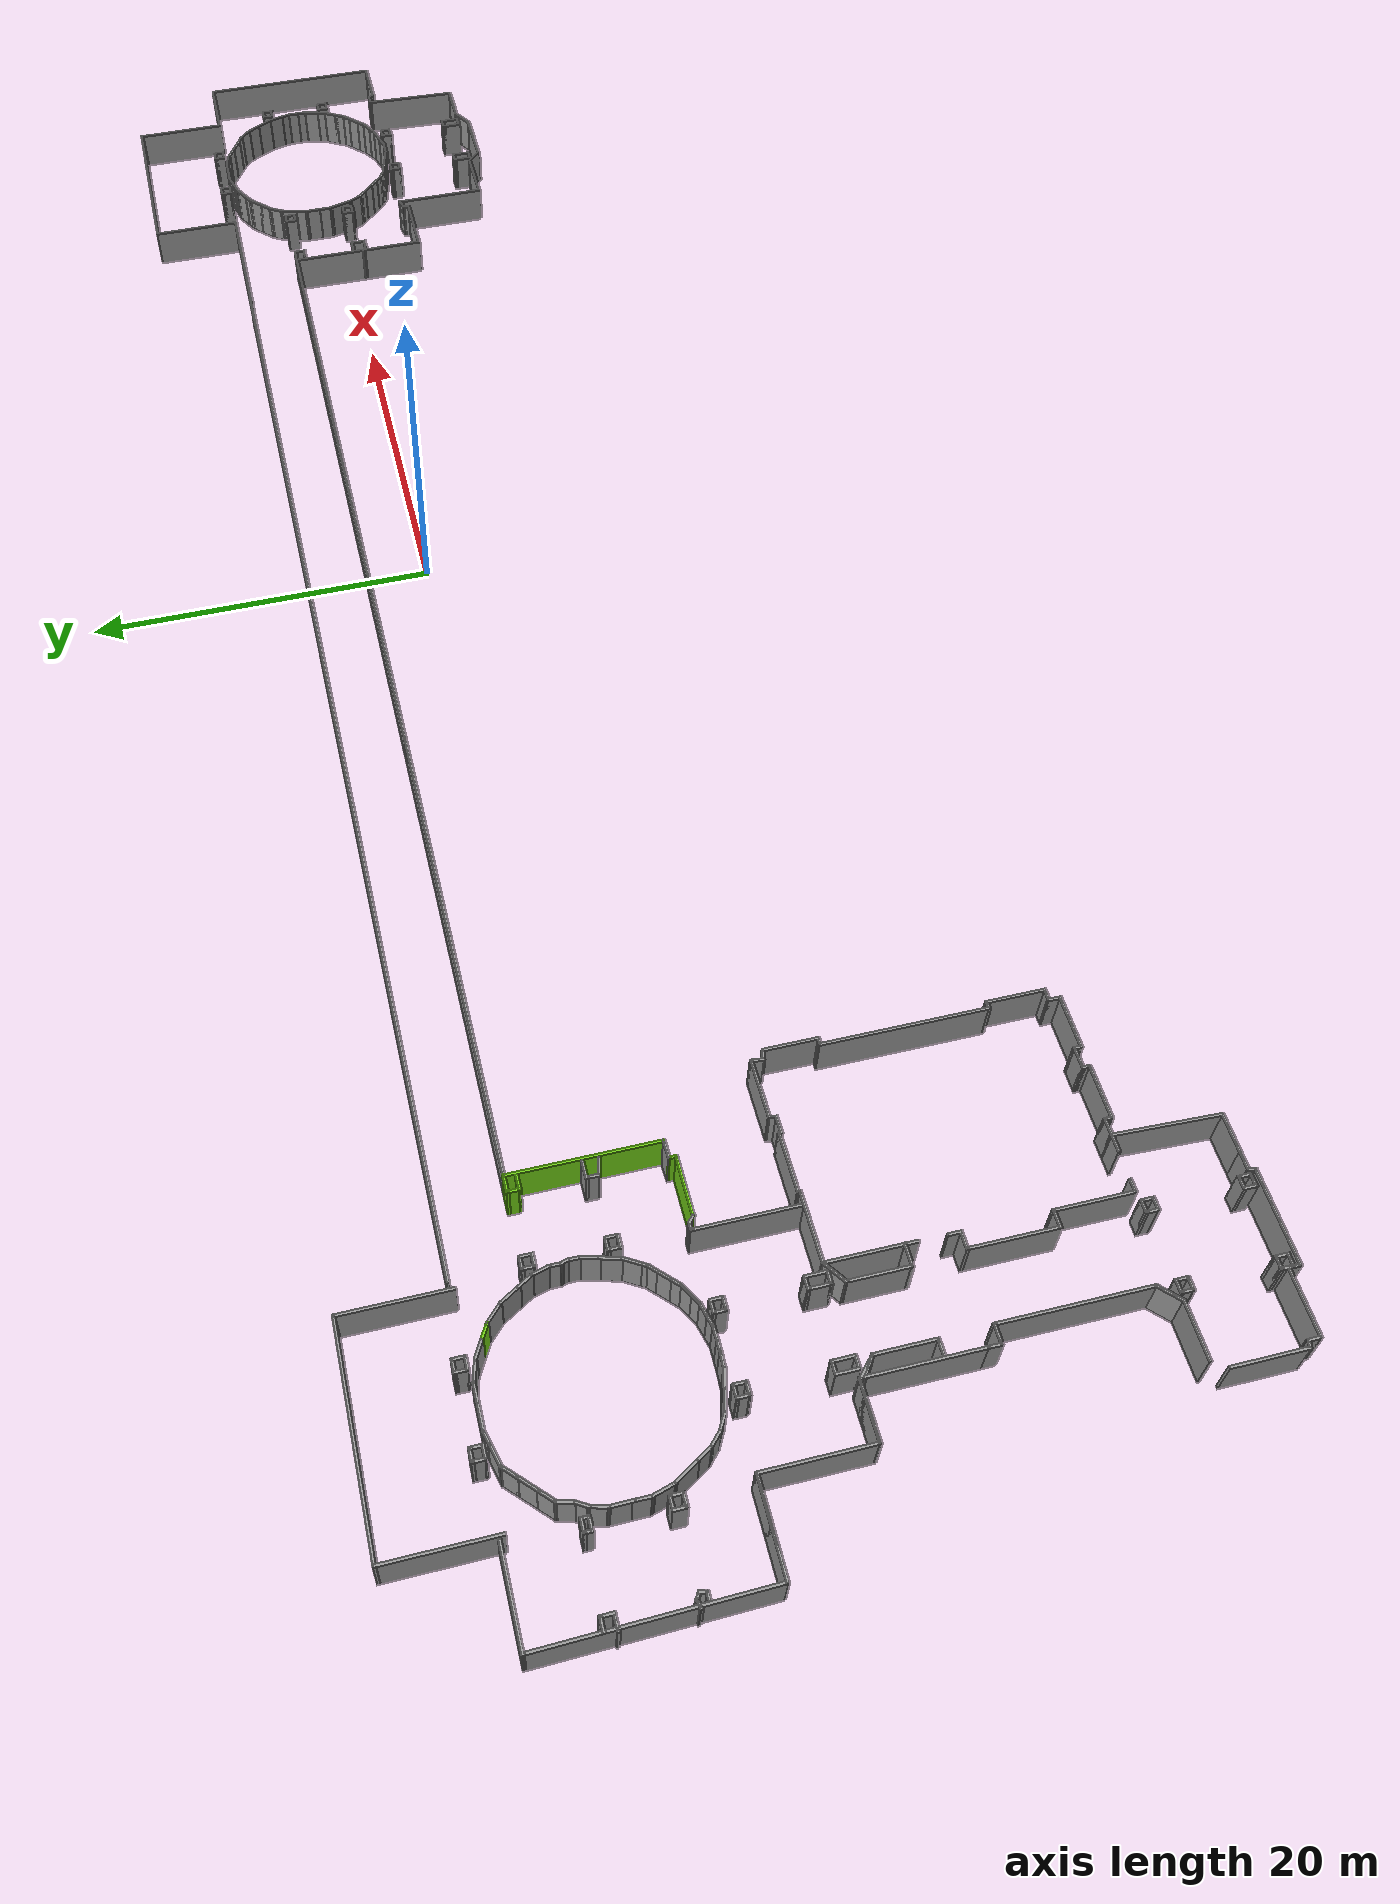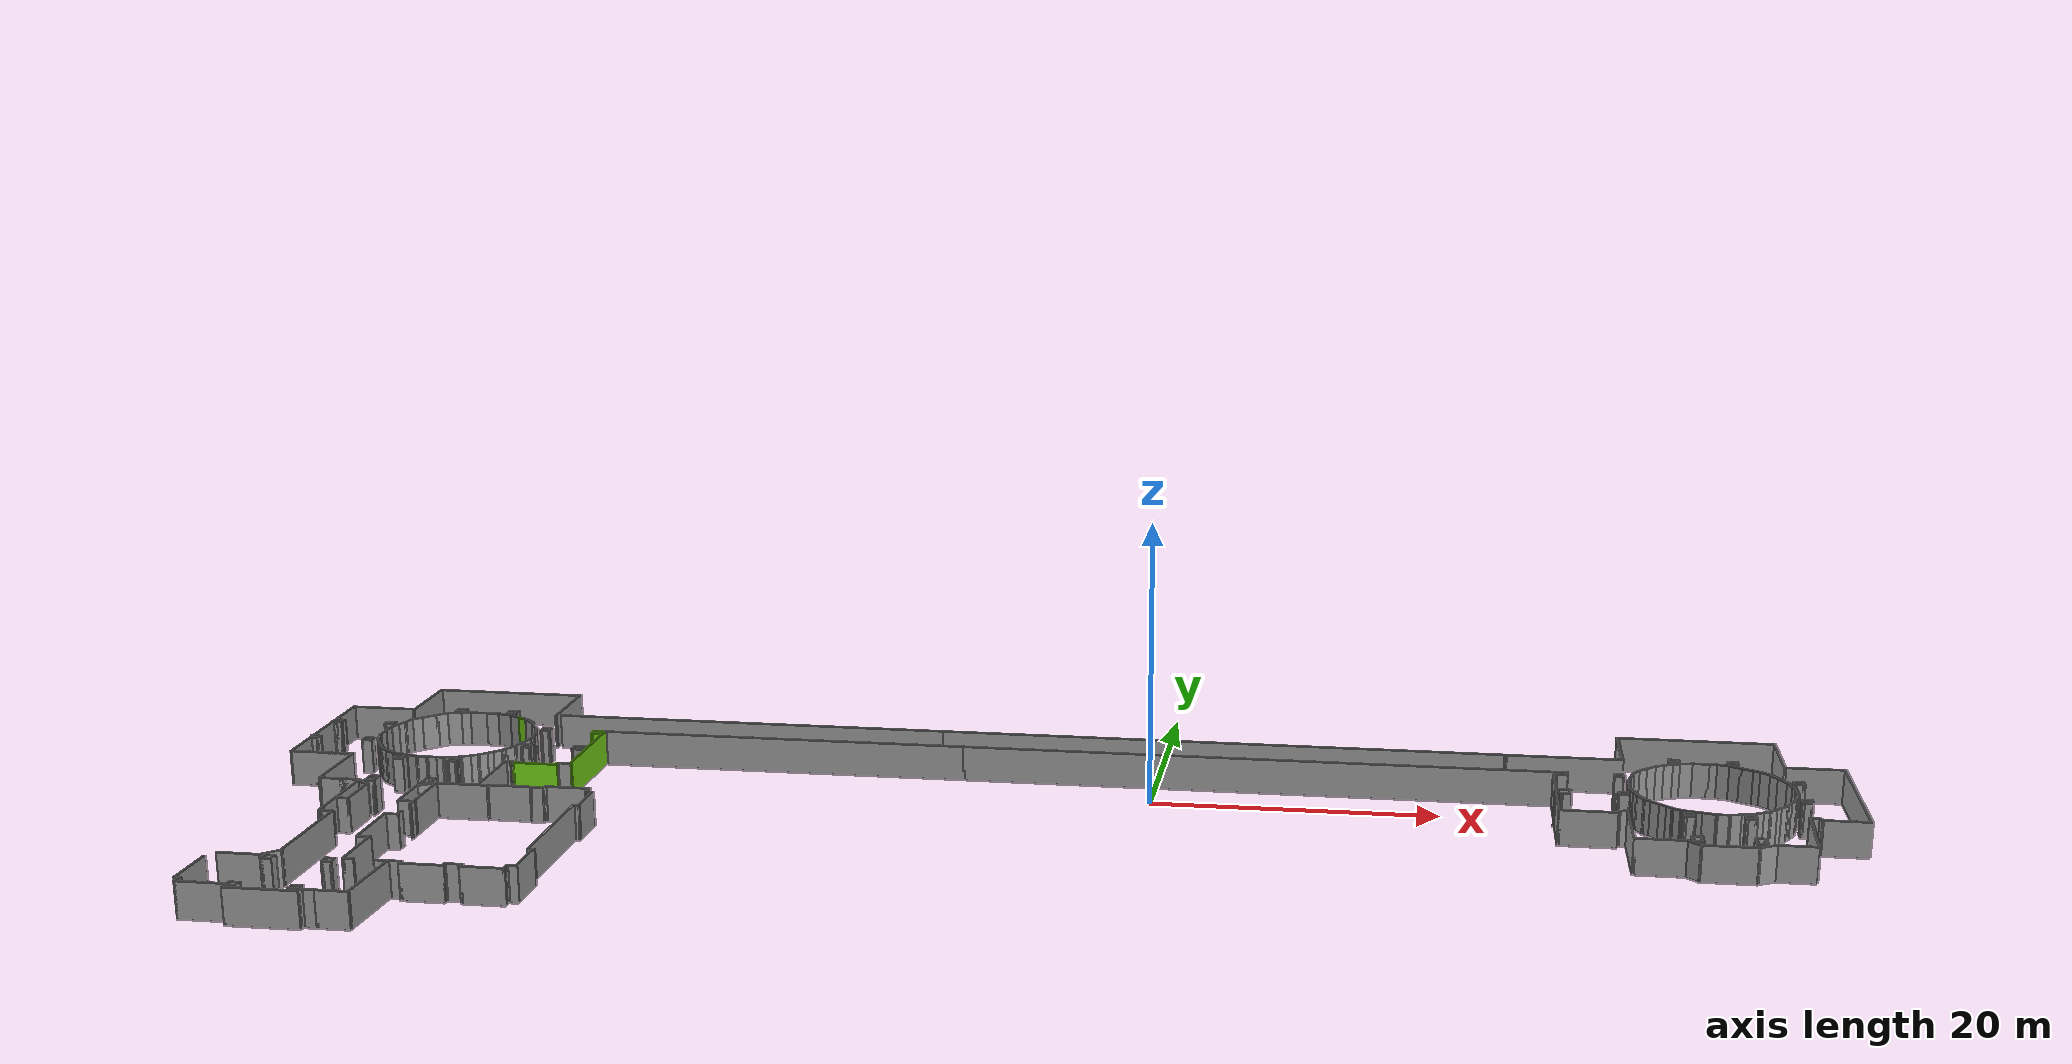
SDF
<?xml version='1.0'?>
<sdf version='1.7'>
  <model name='TD_n1'>
    <pose>-6.74052 -9.30399 0 0 -0 0</pose>
    <link name='Wall_0'>
      <collision name='Wall_0_Collision'>
        <geometry>
          <box>
            <size>4.75 0.15 2.5</size>
          </box>
        </geometry>
        <pose>0 0 1.25 0 -0 0</pose>
      </collision>
      <visual name='Wall_0_Visual'>
        <pose>0 0 1.25 0 -0 0</pose>
        <geometry>
          <box>
            <size>4.75 0.15 2.5</size>
          </box>
        </geometry>
        <material>
          <script>
            <uri>file://media/materials/scripts/gazebo.material</uri>
            <name>Gazebo/Grey</name>
          </script>
          <ambient>1 1 1 1</ambient>
        </material>
        <meta>
          <layer>0</layer>
        </meta>
      </visual>
      <pose>-41.3567 -2.77844 0 0 -0 -1.5708</pose>
    </link>
    <link name='Wall_10'>
      <collision name='Wall_10_Collision'>
        <geometry>
          <box>
            <size>1 0.15 2.5</size>
          </box>
        </geometry>
        <pose>0 0 1.25 0 -0 0</pose>
      </collision>
      <visual name='Wall_10_Visual'>
        <pose>0 0 1.25 0 -0 0</pose>
        <geometry>
          <box>
            <size>1 0.15 2.5</size>
          </box>
        </geometry>
        <material>
          <script>
            <uri>file://media/materials/scripts/gazebo.material</uri>
            <name>Gazebo/Grey</name>
          </script>
          <ambient>1 1 1 1</ambient>
        </material>
        <meta>
          <layer>0</layer>
        </meta>
      </visual>
      <pose>-38.8303 -15.9332 0 0 -0 0</pose>
    </link>
    <link name='Wall_100'>
      <collision name='Wall_100_Collision'>
        <geometry>
          <box>
            <size>0.5 0.15 2.5</size>
          </box>
        </geometry>
        <pose>0 0 1.25 0 -0 0</pose>
      </collision>
      <visual name='Wall_100_Visual'>
        <pose>0 0 1.25 0 -0 0</pose>
        <geometry>
          <box>
            <size>0.5 0.15 2.5</size>
          </box>
        </geometry>
        <material>
          <script>
            <uri>file://media/materials/scripts/gazebo.material</uri>
            <name>Gazebo/Grey</name>
          </script>
          <ambient>1 1 1 1</ambient>
        </material>
        <meta>
          <layer>0</layer>
        </meta>
      </visual>
      <pose>-41.6133 -21.735 0 0 -0 1.309</pose>
    </link>
    <link name='Wall_101'>
      <collision name='Wall_101_Collision'>
        <geometry>
          <box>
            <size>1 0.15 2.5</size>
          </box>
        </geometry>
        <pose>0 0 1.25 0 -0 0</pose>
      </collision>
      <visual name='Wall_101_Visual'>
        <pose>0 0 1.25 0 -0 0</pose>
        <geometry>
          <box>
            <size>1 0.15 2.5</size>
          </box>
        </geometry>
        <material>
          <script>
            <uri>file://media/materials/scripts/gazebo.material</uri>
            <name>Gazebo/Grey</name>
          </script>
          <ambient>1 1 1 1</ambient>
        </material>
        <meta>
          <layer>0</layer>
        </meta>
      </visual>
      <pose>-41.143 -21.5659 0 0 -0 0</pose>
    </link>
    <link name='Wall_103'>
      <collision name='Wall_103_Collision'>
        <geometry>
          <box>
            <size>2.25 0.15 2.5</size>
          </box>
        </geometry>
        <pose>0 0 1.25 0 -0 0</pose>
      </collision>
      <visual name='Wall_103_Visual'>
        <pose>0 0 1.25 0 -0 0</pose>
        <geometry>
          <box>
            <size>2.25 0.15 2.5</size>
          </box>
        </geometry>
        <material>
          <script>
            <uri>file://media/materials/scripts/gazebo.material</uri>
            <name>Gazebo/Grey</name>
          </script>
          <ambient>1 1 1 1</ambient>
        </material>
        <meta>
          <layer>0</layer>
        </meta>
      </visual>
      <pose>-39.668 -21.5659 0 0 -0 0</pose>
    </link>
    <link name='Wall_104'>
      <collision name='Wall_104_Collision'>
        <geometry>
          <box>
            <size>5.78677 0.15 2.5</size>
          </box>
        </geometry>
        <pose>0 0 1.25 0 -0 0</pose>
      </collision>
      <visual name='Wall_104_Visual'>
        <pose>0 0 1.25 0 -0 0</pose>
        <geometry>
          <box>
            <size>5.78677 0.15 2.5</size>
          </box>
        </geometry>
        <material>
          <script>
            <uri>file://media/materials/scripts/gazebo.material</uri>
            <name>Gazebo/Grey</name>
          </script>
          <ambient>1 1 1 1</ambient>
        </material>
        <meta>
          <layer>0</layer>
        </meta>
      </visual>
      <pose>-38.5116 -18.7495 0 0 -0 1.53305</pose>
    </link>
    <link name='Wall_106'>
      <collision name='Wall_106_Collision'>
        <geometry>
          <box>
            <size>3 0.15 2.5</size>
          </box>
        </geometry>
        <pose>0 0 1.25 0 -0 0</pose>
      </collision>
      <visual name='Wall_106_Visual'>
        <pose>0 0 1.25 0 -0 0</pose>
        <geometry>
          <box>
            <size>3 0.15 2.5</size>
          </box>
        </geometry>
        <material>
          <script>
            <uri>file://media/materials/scripts/gazebo.material</uri>
            <name>Gazebo/Grey</name>
          </script>
          <ambient>1 1 1 1</ambient>
        </material>
        <meta>
          <layer>0</layer>
        </meta>
      </visual>
      <pose>-48.3458 -0.459621 0 0 -0 3.14159</pose>
    </link>
    <link name='Wall_107'>
      <collision name='Wall_107_Collision'>
        <geometry>
          <box>
            <size>5.75 0.15 2.5</size>
          </box>
        </geometry>
        <pose>0 0 1.25 0 -0 0</pose>
      </collision>
      <visual name='Wall_107_Visual'>
        <pose>0 0 1.25 0 -0 0</pose>
        <geometry>
          <box>
            <size>5.75 0.15 2.5</size>
          </box>
        </geometry>
        <material>
          <script>
            <uri>file://media/materials/scripts/gazebo.material</uri>
            <name>Gazebo/Grey</name>
          </script>
          <ambient>1 1 1 1</ambient>
        </material>
        <meta>
          <layer>0</layer>
        </meta>
      </visual>
      <pose>-49.7708 2.34038 0 0 -0 1.5708</pose>
    </link>
    <link name='Wall_108'>
      <collision name='Wall_108_Collision'>
        <geometry>
          <box>
            <size>4.75 0.15 2.5</size>
          </box>
        </geometry>
        <pose>0 0 1.25 0 -0 0</pose>
      </collision>
      <visual name='Wall_108_Visual'>
        <pose>0 0 1.25 0 -0 0</pose>
        <geometry>
          <box>
            <size>4.75 0.15 2.5</size>
          </box>
        </geometry>
        <material>
          <script>
            <uri>file://media/materials/scripts/gazebo.material</uri>
            <name>Gazebo/Grey</name>
          </script>
          <ambient>1 1 1 1</ambient>
        </material>
        <meta>
          <layer>0</layer>
        </meta>
      </visual>
      <pose>-52.0708 5.14038 0 0 -0 3.14159</pose>
    </link>
    <link name='Wall_11'>
      <collision name='Wall_11_Collision'>
        <geometry>
          <box>
            <size>1 0.15 2.5</size>
          </box>
        </geometry>
        <pose>0 0 1.25 0 -0 0</pose>
      </collision>
      <visual name='Wall_11_Visual'>
        <pose>0 0 1.25 0 -0 0</pose>
        <geometry>
          <box>
            <size>1 0.15 2.5</size>
          </box>
        </geometry>
        <material>
          <script>
            <uri>file://media/materials/scripts/gazebo.material</uri>
            <name>Gazebo/Grey</name>
          </script>
          <ambient>1 1 1 1</ambient>
        </material>
        <meta>
          <layer>0</layer>
        </meta>
      </visual>
      <pose>-37.9803 -15.9332 0 0 -0 0</pose>
    </link>
    <link name='Wall_110'>
      <collision name='Wall_110_Collision'>
        <geometry>
          <box>
            <size>11.5656 0.15 2.5</size>
          </box>
        </geometry>
        <pose>0 0 1.25 0 -0 0</pose>
      </collision>
      <visual name='Wall_110_Visual'>
        <pose>0 0 1.25 0 -0 0</pose>
        <geometry>
          <box>
            <size>11.5656 0.15 2.5</size>
          </box>
        </geometry>
        <material>
          <script>
            <uri>file://media/materials/scripts/gazebo.material</uri>
            <name>Gazebo/Grey</name>
          </script>
          <ambient>1 1 1 1</ambient>
        </material>
        <meta>
          <layer>0</layer>
        </meta>
      </visual>
      <pose>-54.4598 10.8475 0 0 -0 -1.5552</pose>
    </link>
    <link name='Wall_111'>
      <collision name='Wall_111_Collision'>
        <geometry>
          <box>
            <size>4.75 0.15 2.5</size>
          </box>
        </geometry>
        <pose>0 0 1.25 0 -0 0</pose>
      </collision>
      <visual name='Wall_111_Visual'>
        <pose>0 0 1.25 0 -0 0</pose>
        <geometry>
          <box>
            <size>4.75 0.15 2.5</size>
          </box>
        </geometry>
        <material>
          <script>
            <uri>file://media/materials/scripts/gazebo.material</uri>
            <name>Gazebo/Grey</name>
          </script>
          <ambient>1 1 1 1</ambient>
        </material>
        <meta>
          <layer>0</layer>
        </meta>
      </visual>
      <pose>-52.0708 5.14038 0 0 -0 0</pose>
    </link>
    <link name='Wall_113'>
      <collision name='Wall_113_Collision'>
        <geometry>
          <box>
            <size>4.75 0.15 2.5</size>
          </box>
        </geometry>
        <pose>0 0 1.25 0 -0 0</pose>
      </collision>
      <visual name='Wall_113_Visual'>
        <pose>0 0 1.25 0 -0 0</pose>
        <geometry>
          <box>
            <size>4.75 0.15 2.5</size>
          </box>
        </geometry>
        <material>
          <script>
            <uri>file://media/materials/scripts/gazebo.material</uri>
            <name>Gazebo/Grey</name>
          </script>
          <ambient>1 1 1 1</ambient>
        </material>
        <meta>
          <layer>0</layer>
        </meta>
      </visual>
      <pose>-52.2488 16.5545 0 0 -0 0</pose>
    </link>
    <link name='Wall_115'>
      <collision name='Wall_115_Collision'>
        <geometry>
          <box>
            <size>5.75 0.15 2.5</size>
          </box>
        </geometry>
        <pose>0 0 1.25 0 -0 0</pose>
      </collision>
      <visual name='Wall_115_Visual'>
        <pose>0 0 1.25 0 -0 0</pose>
        <geometry>
          <box>
            <size>5.75 0.15 2.5</size>
          </box>
        </geometry>
        <material>
          <script>
            <uri>file://media/materials/scripts/gazebo.material</uri>
            <name>Gazebo/Grey</name>
          </script>
          <ambient>1 1 1 1</ambient>
        </material>
        <meta>
          <layer>0</layer>
        </meta>
      </visual>
      <pose>-49.7376 19.1208 0 0 -0 -1.5708</pose>
    </link>
    <link name='Wall_117'>
      <collision name='Wall_117_Collision'>
        <geometry>
          <box>
            <size>11.25 0.15 2.5</size>
          </box>
        </geometry>
        <pose>0 0 1.25 0 -0 0</pose>
      </collision>
      <visual name='Wall_117_Visual'>
        <pose>0 0 1.25 0 -0 0</pose>
        <geometry>
          <box>
            <size>11.25 0.15 2.5</size>
          </box>
        </geometry>
        <material>
          <script>
            <uri>file://media/materials/scripts/gazebo.material</uri>
            <name>Gazebo/Grey</name>
          </script>
          <ambient>1 1 1 1</ambient>
        </material>
        <meta>
          <layer>0</layer>
        </meta>
      </visual>
      <pose>-44.1876 21.9208 0 0 -0 0</pose>
    </link>
    <link name='Wall_119'>
      <collision name='Wall_119_Collision'>
        <geometry>
          <box>
            <size>5.75 0.15 2.5</size>
          </box>
        </geometry>
        <pose>0 0 1.25 0 -0 0</pose>
      </collision>
      <visual name='Wall_119_Visual'>
        <pose>0 0 1.25 0 -0 0</pose>
        <geometry>
          <box>
            <size>5.75 0.15 2.5</size>
          </box>
        </geometry>
        <material>
          <script>
            <uri>file://media/materials/scripts/gazebo.material</uri>
            <name>Gazebo/Grey</name>
          </script>
          <ambient>1 1 1 1</ambient>
        </material>
        <meta>
          <layer>0</layer>
        </meta>
      </visual>
      <pose>-38.6376 19.1208 0 0 -0 -1.5708</pose>
    </link>
    <link name='Wall_12'>
      <collision name='Wall_12_Collision'>
        <geometry>
          <box>
            <size>0.5 0.15 2.5</size>
          </box>
        </geometry>
        <pose>0 0 1.25 0 -0 0</pose>
      </collision>
      <visual name='Wall_12_Visual'>
        <pose>0 0 1.25 0 -0 0</pose>
        <geometry>
          <box>
            <size>0.5 0.15 2.5</size>
          </box>
        </geometry>
        <material>
          <script>
            <uri>file://media/materials/scripts/gazebo.material</uri>
            <name>Gazebo/Grey</name>
          </script>
          <ambient>1 1 1 1</ambient>
        </material>
        <meta>
          <layer>0</layer>
        </meta>
      </visual>
      <pose>-37.5553 -16.1082 0 0 -0 -1.5708</pose>
    </link>
    <link name='Wall_121'>
      <collision name='Wall_121_Collision'>
        <geometry>
          <box>
            <size>29 0.15 2.5</size>
          </box>
        </geometry>
        <pose>0 0 1.25 0 -0 0</pose>
      </collision>
      <visual name='Wall_121_Visual'>
        <pose>0 0 1.25 0 -0 0</pose>
        <geometry>
          <box>
            <size>29 0.15 2.5</size>
          </box>
        </geometry>
        <material>
          <script>
            <uri>file://media/materials/scripts/gazebo.material</uri>
            <name>Gazebo/Grey</name>
          </script>
          <ambient>1 1 1 1</ambient>
        </material>
        <meta>
          <layer>0</layer>
        </meta>
      </visual>
      <pose>-23.8398 16.5545 0 0 -0 0</pose>
    </link>
    <link name='Wall_123'>
      <collision name='Wall_123_Collision'>
        <geometry>
          <box>
            <size>26.75 0.15 2.5</size>
          </box>
        </geometry>
        <pose>0 0 1.25 0 -0 0</pose>
      </collision>
      <visual name='Wall_123_Visual'>
        <pose>0 0 1.25 0 -0 0</pose>
        <geometry>
          <box>
            <size>26.75 0.15 2.5</size>
          </box>
        </geometry>
        <material>
          <script>
            <uri>file://media/materials/scripts/gazebo.material</uri>
            <name>Gazebo/Grey</name>
          </script>
          <ambient>1 1 1 1</ambient>
        </material>
        <meta>
          <layer>0</layer>
        </meta>
      </visual>
      <pose>-20.4312 12.9924 0 0 -0 0</pose>
    </link>
    <link name='Wall_125'>
      <collision name='Wall_125_Collision'>
        <geometry>
          <box>
            <size>8 0.15 2.5</size>
          </box>
        </geometry>
        <pose>0 0 1.25 0 -0 0</pose>
      </collision>
      <visual name='Wall_125_Visual'>
        <pose>0 0 1.25 0 -0 0</pose>
        <geometry>
          <box>
            <size>8 0.15 2.5</size>
          </box>
        </geometry>
        <material>
          <script>
            <uri>file://media/materials/scripts/gazebo.material</uri>
            <name>Gazebo/Grey</name>
          </script>
          <ambient>0.45098 0.823529 0.0862745 1</ambient>
        </material>
        <meta>
          <layer>0</layer>
        </meta>
      </visual>
      <pose>-33.7312 9.06743 0 0 -0 -1.5708</pose>
    </link>
    <link name='Wall_127'>
      <collision name='Wall_127_Collision'>
        <geometry>
          <box>
            <size>3.25 0.15 2.5</size>
          </box>
        </geometry>
        <pose>0 0 1.25 0 -0 0</pose>
      </collision>
      <visual name='Wall_127_Visual'>
        <pose>0 0 1.25 0 -0 0</pose>
        <geometry>
          <box>
            <size>3.25 0.15 2.5</size>
          </box>
        </geometry>
        <material>
          <script>
            <uri>file://media/materials/scripts/gazebo.material</uri>
            <name>Gazebo/Grey</name>
          </script>
          <ambient>0.45098 0.823529 0.0862745 1</ambient>
        </material>
        <meta>
          <layer>0</layer>
        </meta>
      </visual>
      <pose>-36.206 4.75793 0 0 -0 0</pose>
    </link>
    <link name='Wall_128'>
      <collision name='Wall_128_Collision'>
        <geometry>
          <box>
            <size>0.5 0.15 2.5</size>
          </box>
        </geometry>
        <pose>0 0 1.25 0 -0 0</pose>
      </collision>
      <visual name='Wall_128_Visual'>
        <pose>0 0 1.25 0 -0 0</pose>
        <geometry>
          <box>
            <size>0.5 0.15 2.5</size>
          </box>
        </geometry>
        <material>
          <script>
            <uri>file://media/materials/scripts/gazebo.material</uri>
            <name>Gazebo/Grey</name>
          </script>
          <ambient>0.45098 0.823529 0.0862745 1</ambient>
        </material>
        <meta>
          <layer>0</layer>
        </meta>
      </visual>
      <pose>-34.656 4.93293 0 0 -0 1.5708</pose>
    </link>
    <link name='Wall_129'>
      <collision name='Wall_129_Collision'>
        <geometry>
          <box>
            <size>1.07537 0.15 2.5</size>
          </box>
        </geometry>
        <pose>0 0 1.25 0 -0 0</pose>
      </collision>
      <visual name='Wall_129_Visual'>
        <pose>0 0 1.25 0 -0 0</pose>
        <geometry>
          <box>
            <size>1.07537 0.15 2.5</size>
          </box>
        </geometry>
        <material>
          <script>
            <uri>file://media/materials/scripts/gazebo.material</uri>
            <name>Gazebo/Grey</name>
          </script>
          <ambient>1 1 1 1</ambient>
        </material>
        <meta>
          <layer>0</layer>
        </meta>
      </visual>
      <pose>-34.1936 5.12518 0 0 -0 0.037287</pose>
    </link>
    <link name='Wall_13'>
      <collision name='Wall_13_Collision'>
        <geometry>
          <box>
            <size>3 0.15 2.5</size>
          </box>
        </geometry>
        <pose>0 0 1.25 0 -0 0</pose>
      </collision>
      <visual name='Wall_13_Visual'>
        <pose>0 0 1.25 0 -0 0</pose>
        <geometry>
          <box>
            <size>3 0.15 2.5</size>
          </box>
        </geometry>
        <material>
          <script>
            <uri>file://media/materials/scripts/gazebo.material</uri>
            <name>Gazebo/Grey</name>
          </script>
          <ambient>1 1 1 1</ambient>
        </material>
        <meta>
          <layer>0</layer>
        </meta>
      </visual>
      <pose>-36.1303 -16.2832 0 0 -0 0</pose>
    </link>
    <link name='Wall_132'>
      <collision name='Wall_132_Collision'>
        <geometry>
          <box>
            <size>5.5 0.15 2.5</size>
          </box>
        </geometry>
        <pose>0 0 1.25 0 -0 0</pose>
      </collision>
      <visual name='Wall_132_Visual'>
        <pose>0 0 1.25 0 -0 0</pose>
        <geometry>
          <box>
            <size>5.5 0.15 2.5</size>
          </box>
        </geometry>
        <material>
          <script>
            <uri>file://media/materials/scripts/gazebo.material</uri>
            <name>Gazebo/Grey</name>
          </script>
          <ambient>1 1 1 1</ambient>
        </material>
        <meta>
          <layer>0</layer>
        </meta>
      </visual>
      <pose>-38.4036 2.3442 0 0 -0 1.5708</pose>
    </link>
    <link name='Wall_133'>
      <collision name='Wall_133_Collision'>
        <geometry>
          <box>
            <size>0.5 0.15 2.5</size>
          </box>
        </geometry>
        <pose>0 0 1.25 0 -0 0</pose>
      </collision>
      <visual name='Wall_133_Visual'>
        <pose>0 0 1.25 0 -0 0</pose>
        <geometry>
          <box>
            <size>0.5 0.15 2.5</size>
          </box>
        </geometry>
        <material>
          <script>
            <uri>file://media/materials/scripts/gazebo.material</uri>
            <name>Gazebo/Grey</name>
          </script>
          <ambient>1 1 1 1</ambient>
        </material>
        <meta>
          <layer>0</layer>
        </meta>
      </visual>
      <pose>-38.2286 5.0192 0 0 -0 0</pose>
    </link>
    <link name='Wall_134'>
      <collision name='Wall_134_Collision'>
        <geometry>
          <box>
            <size>0.546055 0.15 2.5</size>
          </box>
        </geometry>
        <pose>0 0 1.25 0 -0 0</pose>
      </collision>
      <visual name='Wall_134_Visual'>
        <pose>0 0 1.25 0 -0 0</pose>
        <geometry>
          <box>
            <size>0.546055 0.15 2.5</size>
          </box>
        </geometry>
        <material>
          <script>
            <uri>file://media/materials/scripts/gazebo.material</uri>
            <name>Gazebo/Grey</name>
          </script>
          <ambient>1 1 1 1</ambient>
        </material>
        <meta>
          <layer>0</layer>
        </meta>
      </visual>
      <pose>-37.9048 4.88857 0 0 -0 -0.720381</pose>
    </link>
    <link name='Wall_136'>
      <collision name='Wall_136_Collision'>
        <geometry>
          <box>
            <size>0.75 0.15 2.5</size>
          </box>
        </geometry>
        <pose>0 0 1.25 0 -0 0</pose>
      </collision>
      <visual name='Wall_136_Visual'>
        <pose>0 0 1.25 0 -0 0</pose>
        <geometry>
          <box>
            <size>0.75 0.15 2.5</size>
          </box>
        </geometry>
        <material>
          <script>
            <uri>file://media/materials/scripts/gazebo.material</uri>
            <name>Gazebo/Grey</name>
          </script>
          <ambient>1 1 1 1</ambient>
        </material>
        <meta>
          <layer>0</layer>
        </meta>
      </visual>
      <pose>-43.9857 5.24413 0 0 -0 0</pose>
    </link>
    <link name='Wall_137'>
      <collision name='Wall_137_Collision'>
        <geometry>
          <box>
            <size>0.75 0.15 2.5</size>
          </box>
        </geometry>
        <pose>0 0 1.25 0 -0 0</pose>
      </collision>
      <visual name='Wall_137_Visual'>
        <pose>0 0 1.25 0 -0 0</pose>
        <geometry>
          <box>
            <size>0.75 0.15 2.5</size>
          </box>
        </geometry>
        <material>
          <script>
            <uri>file://media/materials/scripts/gazebo.material</uri>
            <name>Gazebo/Grey</name>
          </script>
          <ambient>1 1 1 1</ambient>
        </material>
        <meta>
          <layer>0</layer>
        </meta>
      </visual>
      <pose>-43.3857 5.24413 0 0 -0 0</pose>
    </link>
    <link name='Wall_138'>
      <collision name='Wall_138_Collision'>
        <geometry>
          <box>
            <size>0.75 0.15 2.5</size>
          </box>
        </geometry>
        <pose>0 0 1.25 0 -0 0</pose>
      </collision>
      <visual name='Wall_138_Visual'>
        <pose>0 0 1.25 0 -0 0</pose>
        <geometry>
          <box>
            <size>0.75 0.15 2.5</size>
          </box>
        </geometry>
        <material>
          <script>
            <uri>file://media/materials/scripts/gazebo.material</uri>
            <name>Gazebo/Grey</name>
          </script>
          <ambient>1 1 1 1</ambient>
        </material>
        <meta>
          <layer>0</layer>
        </meta>
      </visual>
      <pose>-42.7959 5.32178 0 0 -0 0.261799</pose>
    </link>
    <link name='Wall_139'>
      <collision name='Wall_139_Collision'>
        <geometry>
          <box>
            <size>0.75 0.15 2.5</size>
          </box>
        </geometry>
        <pose>0 0 1.25 0 -0 0</pose>
      </collision>
      <visual name='Wall_139_Visual'>
        <pose>0 0 1.25 0 -0 0</pose>
        <geometry>
          <box>
            <size>0.75 0.15 2.5</size>
          </box>
        </geometry>
        <material>
          <script>
            <uri>file://media/materials/scripts/gazebo.material</uri>
            <name>Gazebo/Grey</name>
          </script>
          <ambient>1 1 1 1</ambient>
        </material>
        <meta>
          <layer>0</layer>
        </meta>
      </visual>
      <pose>-42.2164 5.47707 0 0 -0 0.261799</pose>
    </link>
    <link name='Wall_14'>
      <collision name='Wall_14_Collision'>
        <geometry>
          <box>
            <size>0.5 0.15 2.5</size>
          </box>
        </geometry>
        <pose>0 0 1.25 0 -0 0</pose>
      </collision>
      <visual name='Wall_14_Visual'>
        <pose>0 0 1.25 0 -0 0</pose>
        <geometry>
          <box>
            <size>0.5 0.15 2.5</size>
          </box>
        </geometry>
        <material>
          <script>
            <uri>file://media/materials/scripts/gazebo.material</uri>
            <name>Gazebo/Grey</name>
          </script>
          <ambient>1 1 1 1</ambient>
        </material>
        <meta>
          <layer>0</layer>
        </meta>
      </visual>
      <pose>-34.7053 -16.1082 0 0 -0 1.5708</pose>
    </link>
    <link name='Wall_140'>
      <collision name='Wall_140_Collision'>
        <geometry>
          <box>
            <size>0.75 0.15 2.5</size>
          </box>
        </geometry>
        <pose>0 0 1.25 0 -0 0</pose>
      </collision>
      <visual name='Wall_140_Visual'>
        <pose>0 0 1.25 0 -0 0</pose>
        <geometry>
          <box>
            <size>0.75 0.15 2.5</size>
          </box>
        </geometry>
        <material>
          <script>
            <uri>file://media/materials/scripts/gazebo.material</uri>
            <name>Gazebo/Grey</name>
          </script>
          <ambient>1 1 1 1</ambient>
        </material>
        <meta>
          <layer>0</layer>
        </meta>
      </visual>
      <pose>-41.6668 5.70472 0 0 -0 0.523599</pose>
    </link>
    <link name='Wall_141'>
      <collision name='Wall_141_Collision'>
        <geometry>
          <box>
            <size>0.75 0.15 2.5</size>
          </box>
        </geometry>
        <pose>0 0 1.25 0 -0 0</pose>
      </collision>
      <visual name='Wall_141_Visual'>
        <pose>0 0 1.25 0 -0 0</pose>
        <geometry>
          <box>
            <size>0.75 0.15 2.5</size>
          </box>
        </geometry>
        <material>
          <script>
            <uri>file://media/materials/scripts/gazebo.material</uri>
            <name>Gazebo/Grey</name>
          </script>
          <ambient>1 1 1 1</ambient>
        </material>
        <meta>
          <layer>0</layer>
        </meta>
      </visual>
      <pose>-41.1472 6.00472 0 0 -0 0.523599</pose>
    </link>
    <link name='Wall_142'>
      <collision name='Wall_142_Collision'>
        <geometry>
          <box>
            <size>0.75 0.15 2.5</size>
          </box>
        </geometry>
        <pose>0 0 1.25 0 -0 0</pose>
      </collision>
      <visual name='Wall_142_Visual'>
        <pose>0 0 1.25 0 -0 0</pose>
        <geometry>
          <box>
            <size>0.75 0.15 2.5</size>
          </box>
        </geometry>
        <material>
          <script>
            <uri>file://media/materials/scripts/gazebo.material</uri>
            <name>Gazebo/Grey</name>
          </script>
          <ambient>1 1 1 1</ambient>
        </material>
        <meta>
          <layer>0</layer>
        </meta>
      </visual>
      <pose>-40.6752 6.36685 0 0 -0 0.785398</pose>
    </link>
    <link name='Wall_143'>
      <collision name='Wall_143_Collision'>
        <geometry>
          <box>
            <size>0.75 0.15 2.5</size>
          </box>
        </geometry>
        <pose>0 0 1.25 0 -0 0</pose>
      </collision>
      <visual name='Wall_143_Visual'>
        <pose>0 0 1.25 0 -0 0</pose>
        <geometry>
          <box>
            <size>0.75 0.15 2.5</size>
          </box>
        </geometry>
        <material>
          <script>
            <uri>file://media/materials/scripts/gazebo.material</uri>
            <name>Gazebo/Grey</name>
          </script>
          <ambient>1 1 1 1</ambient>
        </material>
        <meta>
          <layer>0</layer>
        </meta>
      </visual>
      <pose>-40.251 6.79111 0 0 -0 0.785398</pose>
    </link>
    <link name='Wall_144'>
      <collision name='Wall_144_Collision'>
        <geometry>
          <box>
            <size>0.75 0.15 2.5</size>
          </box>
        </geometry>
        <pose>0 0 1.25 0 -0 0</pose>
      </collision>
      <visual name='Wall_144_Visual'>
        <pose>0 0 1.25 0 -0 0</pose>
        <geometry>
          <box>
            <size>0.75 0.15 2.5</size>
          </box>
        </geometry>
        <material>
          <script>
            <uri>file://media/materials/scripts/gazebo.material</uri>
            <name>Gazebo/Grey</name>
          </script>
          <ambient>1 1 1 1</ambient>
        </material>
        <meta>
          <layer>0</layer>
        </meta>
      </visual>
      <pose>-39.8267 7.21538 0 0 -0 0.785398</pose>
    </link>
    <link name='Wall_145'>
      <collision name='Wall_145_Collision'>
        <geometry>
          <box>
            <size>0.5 0.15 2.5</size>
          </box>
        </geometry>
        <pose>0 0 1.25 0 -0 0</pose>
      </collision>
      <visual name='Wall_145_Visual'>
        <pose>0 0 1.25 0 -0 0</pose>
        <geometry>
          <box>
            <size>0.5 0.15 2.5</size>
          </box>
        </geometry>
        <material>
          <script>
            <uri>file://media/materials/scripts/gazebo.material</uri>
            <name>Gazebo/Grey</name>
          </script>
          <ambient>1 1 1 1</ambient>
        </material>
        <meta>
          <layer>0</layer>
        </meta>
      </visual>
      <pose>-39.5271 7.57906 0 0 -0 1.0472</pose>
    </link>
    <link name='Wall_146'>
      <collision name='Wall_146_Collision'>
        <geometry>
          <box>
            <size>1 0.15 2.5</size>
          </box>
        </geometry>
        <pose>0 0 1.25 0 -0 0</pose>
      </collision>
      <visual name='Wall_146_Visual'>
        <pose>0 0 1.25 0 -0 0</pose>
        <geometry>
          <box>
            <size>1 0.15 2.5</size>
          </box>
        </geometry>
        <material>
          <script>
            <uri>file://media/materials/scripts/gazebo.material</uri>
            <name>Gazebo/Grey</name>
          </script>
          <ambient>1 1 1 1</ambient>
        </material>
        <meta>
          <layer>0</layer>
        </meta>
      </visual>
      <pose>-39.2271 8.09868 0 0 -0 1.0472</pose>
    </link>
    <link name='Wall_147'>
      <collision name='Wall_147_Collision'>
        <geometry>
          <box>
            <size>1.25 0.15 2.5</size>
          </box>
        </geometry>
        <pose>0 0 1.25 0 -0 0</pose>
      </collision>
      <visual name='Wall_147_Visual'>
        <pose>0 0 1.25 0 -0 0</pose>
        <geometry>
          <box>
            <size>1.25 0.15 2.5</size>
          </box>
        </geometry>
        <material>
          <script>
            <uri>file://media/materials/scripts/gazebo.material</uri>
            <name>Gazebo/Grey</name>
          </script>
          <ambient>1 1 1 1</ambient>
        </material>
        <meta>
          <layer>0</layer>
        </meta>
      </visual>
      <pose>-38.8722 8.998 0 0 -0 1.309</pose>
    </link>
    <link name='Wall_148'>
      <collision name='Wall_148_Collision'>
        <geometry>
          <box>
            <size>1 0.15 2.5</size>
          </box>
        </geometry>
        <pose>0 0 1.25 0 -0 0</pose>
      </collision>
      <visual name='Wall_148_Visual'>
        <pose>0 0 1.25 0 -0 0</pose>
        <geometry>
          <box>
            <size>1 0.15 2.5</size>
          </box>
        </geometry>
        <material>
          <script>
            <uri>file://media/materials/scripts/gazebo.material</uri>
            <name>Gazebo/Grey</name>
          </script>
          <ambient>1 1 1 1</ambient>
        </material>
        <meta>
          <layer>0</layer>
        </meta>
      </visual>
      <pose>-38.6199 9.93978 0 0 -0 1.309</pose>
    </link>
    <link name='Wall_149'>
      <collision name='Wall_149_Collision'>
        <geometry>
          <box>
            <size>0.75 0.15 2.5</size>
          </box>
        </geometry>
        <pose>0 0 1.25 0 -0 0</pose>
      </collision>
      <visual name='Wall_149_Visual'>
        <pose>0 0 1.25 0 -0 0</pose>
        <geometry>
          <box>
            <size>0.75 0.15 2.5</size>
          </box>
        </geometry>
        <material>
          <script>
            <uri>file://media/materials/scripts/gazebo.material</uri>
            <name>Gazebo/Grey</name>
          </script>
          <ambient>1 1 1 1</ambient>
        </material>
        <meta>
          <layer>0</layer>
        </meta>
      </visual>
      <pose>-38.5099 10.6503 0 0 -0 1.5708</pose>
    </link>
    <link name='Wall_15'>
      <collision name='Wall_15_Collision'>
        <geometry>
          <box>
            <size>1.25 0.15 2.5</size>
          </box>
        </geometry>
        <pose>0 0 1.25 0 -0 0</pose>
      </collision>
      <visual name='Wall_15_Visual'>
        <pose>0 0 1.25 0 -0 0</pose>
        <geometry>
          <box>
            <size>1.25 0.15 2.5</size>
          </box>
        </geometry>
        <material>
          <script>
            <uri>file://media/materials/scripts/gazebo.material</uri>
            <name>Gazebo/Grey</name>
          </script>
          <ambient>1 1 1 1</ambient>
        </material>
        <meta>
          <layer>0</layer>
        </meta>
      </visual>
      <pose>-34.1553 -15.9332 0 0 -0 0</pose>
    </link>
    <link name='Wall_150'>
      <collision name='Wall_150_Collision'>
        <geometry>
          <box>
            <size>0.5 0.15 2.5</size>
          </box>
        </geometry>
        <pose>0 0 1.25 0 -0 0</pose>
      </collision>
      <visual name='Wall_150_Visual'>
        <pose>0 0 1.25 0 -0 0</pose>
        <geometry>
          <box>
            <size>0.5 0.15 2.5</size>
          </box>
        </geometry>
        <material>
          <script>
            <uri>file://media/materials/scripts/gazebo.material</uri>
            <name>Gazebo/Grey</name>
          </script>
          <ambient>1 1 1 1</ambient>
        </material>
        <meta>
          <layer>0</layer>
        </meta>
      </visual>
      <pose>-38.5552 11.1193 0 0 -0 1.8326</pose>
    </link>
    <link name='Wall_153'>
      <collision name='Wall_153_Collision'>
        <geometry>
          <box>
            <size>0.75 0.15 2.5</size>
          </box>
        </geometry>
        <pose>0 0 1.25 0 -0 0</pose>
      </collision>
      <visual name='Wall_153_Visual'>
        <pose>0 0 1.25 0 -0 0</pose>
        <geometry>
          <box>
            <size>0.75 0.15 2.5</size>
          </box>
        </geometry>
        <material>
          <script>
            <uri>file://media/materials/scripts/gazebo.material</uri>
            <name>Gazebo/Grey</name>
          </script>
          <ambient>1 1 1 1</ambient>
        </material>
        <meta>
          <layer>0</layer>
        </meta>
      </visual>
      <pose>-38.6005 11.5884 0 0 -0 1.5708</pose>
    </link>
    <link name='Wall_154'>
      <collision name='Wall_154_Collision'>
        <geometry>
          <box>
            <size>1 0.15 2.5</size>
          </box>
        </geometry>
        <pose>0 0 1.25 0 -0 0</pose>
      </collision>
      <visual name='Wall_154_Visual'>
        <pose>0 0 1.25 0 -0 0</pose>
        <geometry>
          <box>
            <size>1 0.15 2.5</size>
          </box>
        </geometry>
        <material>
          <script>
            <uri>file://media/materials/scripts/gazebo.material</uri>
            <name>Gazebo/Grey</name>
          </script>
          <ambient>1 1 1 1</ambient>
        </material>
        <meta>
          <layer>0</layer>
        </meta>
      </visual>
      <pose>-38.7105 12.2989 0 0 -0 1.8326</pose>
    </link>
    <link name='Wall_155'>
      <collision name='Wall_155_Collision'>
        <geometry>
          <box>
            <size>1 0.15 2.5</size>
          </box>
        </geometry>
        <pose>0 0 1.25 0 -0 0</pose>
      </collision>
      <visual name='Wall_155_Visual'>
        <pose>0 0 1.25 0 -0 0</pose>
        <geometry>
          <box>
            <size>1 0.15 2.5</size>
          </box>
        </geometry>
        <material>
          <script>
            <uri>file://media/materials/scripts/gazebo.material</uri>
            <name>Gazebo/Grey</name>
          </script>
          <ambient>1 1 1 1</ambient>
        </material>
        <meta>
          <layer>0</layer>
        </meta>
      </visual>
      <pose>-39.033 13.0775 0 0 -0 2.0944</pose>
    </link>
    <link name='Wall_156'>
      <collision name='Wall_156_Collision'>
        <geometry>
          <box>
            <size>1.25 0.15 2.5</size>
          </box>
        </geometry>
        <pose>0 0 1.25 0 -0 0</pose>
      </collision>
      <visual name='Wall_156_Visual'>
        <pose>0 0 1.25 0 -0 0</pose>
        <geometry>
          <box>
            <size>1.25 0.15 2.5</size>
          </box>
        </geometry>
        <material>
          <script>
            <uri>file://media/materials/scripts/gazebo.material</uri>
            <name>Gazebo/Grey</name>
          </script>
          <ambient>1 1 1 1</ambient>
        </material>
        <meta>
          <layer>0</layer>
        </meta>
      </visual>
      <pose>-39.5205 13.9218 0 0 -0 2.0944</pose>
    </link>
    <link name='Wall_157'>
      <collision name='Wall_157_Collision'>
        <geometry>
          <box>
            <size>1.25 0.15 2.5</size>
          </box>
        </geometry>
        <pose>0 0 1.25 0 -0 0</pose>
      </collision>
      <visual name='Wall_157_Visual'>
        <pose>0 0 1.25 0 -0 0</pose>
        <geometry>
          <box>
            <size>1.25 0.15 2.5</size>
          </box>
        </geometry>
        <material>
          <script>
            <uri>file://media/materials/scripts/gazebo.material</uri>
            <name>Gazebo/Grey</name>
          </script>
          <ambient>1 1 1 1</ambient>
        </material>
        <meta>
          <layer>0</layer>
        </meta>
      </visual>
      <pose>-40.1844 14.7871 0 0 -0 2.35619</pose>
    </link>
    <link name='Wall_158'>
      <collision name='Wall_158_Collision'>
        <geometry>
          <box>
            <size>1 0.15 2.5</size>
          </box>
        </geometry>
        <pose>0 0 1.25 0 -0 0</pose>
      </collision>
      <visual name='Wall_158_Visual'>
        <pose>0 0 1.25 0 -0 0</pose>
        <geometry>
          <box>
            <size>1 0.15 2.5</size>
          </box>
        </geometry>
        <material>
          <script>
            <uri>file://media/materials/scripts/gazebo.material</uri>
            <name>Gazebo/Grey</name>
          </script>
          <ambient>0.45098 0.823529 0.0862745 1</ambient>
        </material>
        <meta>
          <layer>0</layer>
        </meta>
      </visual>
      <pose>-40.9413 15.3885 0 0 -0 2.61799</pose>
    </link>
    <link name='Wall_159'>
      <collision name='Wall_159_Collision'>
        <geometry>
          <box>
            <size>1 0.15 2.5</size>
          </box>
        </geometry>
        <pose>0 0 1.25 0 -0 0</pose>
      </collision>
      <visual name='Wall_159_Visual'>
        <pose>0 0 1.25 0 -0 0</pose>
        <geometry>
          <box>
            <size>1 0.15 2.5</size>
          </box>
        </geometry>
        <material>
          <script>
            <uri>file://media/materials/scripts/gazebo.material</uri>
            <name>Gazebo/Grey</name>
          </script>
          <ambient>1 1 1 1</ambient>
        </material>
        <meta>
          <layer>0</layer>
        </meta>
      </visual>
      <pose>-41.6775 15.8135 0 0 -0 2.61799</pose>
    </link>
    <link name='Wall_16'>
      <collision name='Wall_16_Collision'>
        <geometry>
          <box>
            <size>0.5 0.15 2.5</size>
          </box>
        </geometry>
        <pose>0 0 1.25 0 -0 0</pose>
      </collision>
      <visual name='Wall_16_Visual'>
        <pose>0 0 1.25 0 -0 0</pose>
        <geometry>
          <box>
            <size>0.5 0.15 2.5</size>
          </box>
        </geometry>
        <material>
          <script>
            <uri>file://media/materials/scripts/gazebo.material</uri>
            <name>Gazebo/Grey</name>
          </script>
          <ambient>1 1 1 1</ambient>
        </material>
        <meta>
          <layer>0</layer>
        </meta>
      </visual>
      <pose>-33.6053 -16.1082 0 0 -0 -1.5708</pose>
    </link>
    <link name='Wall_160'>
      <collision name='Wall_160_Collision'>
        <geometry>
          <box>
            <size>1.25 0.15 2.5</size>
          </box>
        </geometry>
        <pose>0 0 1.25 0 -0 0</pose>
      </collision>
      <visual name='Wall_160_Visual'>
        <pose>0 0 1.25 0 -0 0</pose>
        <geometry>
          <box>
            <size>1.25 0.15 2.5</size>
          </box>
        </geometry>
        <material>
          <script>
            <uri>file://media/materials/scripts/gazebo.material</uri>
            <name>Gazebo/Grey</name>
          </script>
          <ambient>1 1 1 1</ambient>
        </material>
        <meta>
          <layer>0</layer>
        </meta>
      </visual>
      <pose>-42.5768 16.1683 0 0 -0 2.87979</pose>
    </link>
    <link name='Wall_161'>
      <collision name='Wall_161_Collision'>
        <geometry>
          <box>
            <size>1 0.15 2.5</size>
          </box>
        </geometry>
        <pose>0 0 1.25 0 -0 0</pose>
      </collision>
      <visual name='Wall_161_Visual'>
        <pose>0 0 1.25 0 -0 0</pose>
        <geometry>
          <box>
            <size>1 0.15 2.5</size>
          </box>
        </geometry>
        <material>
          <script>
            <uri>file://media/materials/scripts/gazebo.material</uri>
            <name>Gazebo/Grey</name>
          </script>
          <ambient>1 1 1 1</ambient>
        </material>
        <meta>
          <layer>0</layer>
        </meta>
      </visual>
      <pose>-43.533 16.3107 0 0 -0 3.14159</pose>
    </link>
    <link name='Wall_162'>
      <collision name='Wall_162_Collision'>
        <geometry>
          <box>
            <size>1.5 0.15 2.5</size>
          </box>
        </geometry>
        <pose>0 0 1.25 0 -0 0</pose>
      </collision>
      <visual name='Wall_162_Visual'>
        <pose>0 0 1.25 0 -0 0</pose>
        <geometry>
          <box>
            <size>1.5 0.15 2.5</size>
          </box>
        </geometry>
        <material>
          <script>
            <uri>file://media/materials/scripts/gazebo.material</uri>
            <name>Gazebo/Grey</name>
          </script>
          <ambient>1 1 1 1</ambient>
        </material>
        <meta>
          <layer>0</layer>
        </meta>
      </visual>
      <pose>-44.633 16.3107 0 0 -0 3.14159</pose>
    </link>
    <link name='Wall_163'>
      <collision name='Wall_163_Collision'>
        <geometry>
          <box>
            <size>0.75 0.15 2.5</size>
          </box>
        </geometry>
        <pose>0 0 1.25 0 -0 0</pose>
      </collision>
      <visual name='Wall_163_Visual'>
        <pose>0 0 1.25 0 -0 0</pose>
        <geometry>
          <box>
            <size>0.75 0.15 2.5</size>
          </box>
        </geometry>
        <material>
          <script>
            <uri>file://media/materials/scripts/gazebo.material</uri>
            <name>Gazebo/Grey</name>
          </script>
          <ambient>1 1 1 1</ambient>
        </material>
        <meta>
          <layer>0</layer>
        </meta>
      </visual>
      <pose>-45.5978 16.233 0 0 -0 -2.87979</pose>
    </link>
    <link name='Wall_164'>
      <collision name='Wall_164_Collision'>
        <geometry>
          <box>
            <size>1.25 0.15 2.5</size>
          </box>
        </geometry>
        <pose>0 0 1.25 0 -0 0</pose>
      </collision>
      <visual name='Wall_164_Visual'>
        <pose>0 0 1.25 0 -0 0</pose>
        <geometry>
          <box>
            <size>1.25 0.15 2.5</size>
          </box>
        </geometry>
        <material>
          <script>
            <uri>file://media/materials/scripts/gazebo.material</uri>
            <name>Gazebo/Grey</name>
          </script>
          <ambient>1 1 1 1</ambient>
        </material>
        <meta>
          <layer>0</layer>
        </meta>
      </visual>
      <pose>-46.4189 16.013 0 0 -0 -2.87979</pose>
    </link>
    <link name='Wall_165'>
      <collision name='Wall_165_Collision'>
        <geometry>
          <box>
            <size>1 0.15 2.5</size>
          </box>
        </geometry>
        <pose>0 0 1.25 0 -0 0</pose>
      </collision>
      <visual name='Wall_165_Visual'>
        <pose>0 0 1.25 0 -0 0</pose>
        <geometry>
          <box>
            <size>1 0.15 2.5</size>
          </box>
        </geometry>
        <material>
          <script>
            <uri>file://media/materials/scripts/gazebo.material</uri>
            <name>Gazebo/Grey</name>
          </script>
          <ambient>1 1 1 1</ambient>
        </material>
        <meta>
          <layer>0</layer>
        </meta>
      </visual>
      <pose>-47.2506 15.5702 0 0 -0 -2.35619</pose>
    </link>
    <link name='Wall_166'>
      <collision name='Wall_166_Collision'>
        <geometry>
          <box>
            <size>1.25 0.15 2.5</size>
          </box>
        </geometry>
        <pose>0 0 1.25 0 -0 0</pose>
      </collision>
      <visual name='Wall_166_Visual'>
        <pose>0 0 1.25 0 -0 0</pose>
        <geometry>
          <box>
            <size>1.25 0.15 2.5</size>
          </box>
        </geometry>
        <material>
          <script>
            <uri>file://media/materials/scripts/gazebo.material</uri>
            <name>Gazebo/Grey</name>
          </script>
          <ambient>1 1 1 1</ambient>
        </material>
        <meta>
          <layer>0</layer>
        </meta>
      </visual>
      <pose>-47.9401 14.8807 0 0 -0 -2.35619</pose>
    </link>
    <link name='Wall_167'>
      <collision name='Wall_167_Collision'>
        <geometry>
          <box>
            <size>1 0.15 2.5</size>
          </box>
        </geometry>
        <pose>0 0 1.25 0 -0 0</pose>
      </collision>
      <visual name='Wall_167_Visual'>
        <pose>0 0 1.25 0 -0 0</pose>
        <geometry>
          <box>
            <size>1 0.15 2.5</size>
          </box>
        </geometry>
        <material>
          <script>
            <uri>file://media/materials/scripts/gazebo.material</uri>
            <name>Gazebo/Grey</name>
          </script>
          <ambient>1 1 1 1</ambient>
        </material>
        <meta>
          <layer>0</layer>
        </meta>
      </visual>
      <pose>-48.6295 14.1913 0 0 -0 -2.35619</pose>
    </link>
    <link name='Wall_168'>
      <collision name='Wall_168_Collision'>
        <geometry>
          <box>
            <size>1 0.15 2.5</size>
          </box>
        </geometry>
        <pose>0 0 1.25 0 -0 0</pose>
      </collision>
      <visual name='Wall_168_Visual'>
        <pose>0 0 1.25 0 -0 0</pose>
        <geometry>
          <box>
            <size>1 0.15 2.5</size>
          </box>
        </geometry>
        <material>
          <script>
            <uri>file://media/materials/scripts/gazebo.material</uri>
            <name>Gazebo/Grey</name>
          </script>
          <ambient>1 1 1 1</ambient>
        </material>
        <meta>
          <layer>0</layer>
        </meta>
      </visual>
      <pose>-49.04 13.4803 0 0 -0 -1.8326</pose>
    </link>
    <link name='Wall_169'>
      <collision name='Wall_169_Collision'>
        <geometry>
          <box>
            <size>0.75 0.15 2.5</size>
          </box>
        </geometry>
        <pose>0 0 1.25 0 -0 0</pose>
      </collision>
      <visual name='Wall_169_Visual'>
        <pose>0 0 1.25 0 -0 0</pose>
        <geometry>
          <box>
            <size>0.75 0.15 2.5</size>
          </box>
        </geometry>
        <material>
          <script>
            <uri>file://media/materials/scripts/gazebo.material</uri>
            <name>Gazebo/Grey</name>
          </script>
          <ambient>1 1 1 1</ambient>
        </material>
        <meta>
          <layer>0</layer>
        </meta>
      </visual>
      <pose>-49.3 12.8099 0 0 -0 -2.0944</pose>
    </link>
    <link name='Wall_17'>
      <collision name='Wall_17_Collision'>
        <geometry>
          <box>
            <size>3 0.15 2.5</size>
          </box>
        </geometry>
        <pose>0 0 1.25 0 -0 0</pose>
      </collision>
      <visual name='Wall_17_Visual'>
        <pose>0 0 1.25 0 -0 0</pose>
        <geometry>
          <box>
            <size>3 0.15 2.5</size>
          </box>
        </geometry>
        <material>
          <script>
            <uri>file://media/materials/scripts/gazebo.material</uri>
            <name>Gazebo/Grey</name>
          </script>
          <ambient>1 1 1 1</ambient>
        </material>
        <meta>
          <layer>0</layer>
        </meta>
      </visual>
      <pose>-32.1803 -16.2832 0 0 -0 0</pose>
    </link>
    <link name='Wall_170'>
      <collision name='Wall_170_Collision'>
        <geometry>
          <box>
            <size>1 0.15 2.5</size>
          </box>
        </geometry>
        <pose>0 0 1.25 0 -0 0</pose>
      </collision>
      <visual name='Wall_170_Visual'>
        <pose>0 0 1.25 0 -0 0</pose>
        <geometry>
          <box>
            <size>1 0.15 2.5</size>
          </box>
        </geometry>
        <material>
          <script>
            <uri>file://media/materials/scripts/gazebo.material</uri>
            <name>Gazebo/Grey</name>
          </script>
          <ambient>1 1 1 1</ambient>
        </material>
        <meta>
          <layer>0</layer>
        </meta>
      </visual>
      <pose>-49.56 12.1396 0 0 -0 -1.8326</pose>
    </link>
    <link name='Wall_171'>
      <collision name='Wall_171_Collision'>
        <geometry>
          <box>
            <size>1.25 0.15 2.5</size>
          </box>
        </geometry>
        <pose>0 0 1.25 0 -0 0</pose>
      </collision>
      <visual name='Wall_171_Visual'>
        <pose>0 0 1.25 0 -0 0</pose>
        <geometry>
          <box>
            <size>1.25 0.15 2.5</size>
          </box>
        </geometry>
        <material>
          <script>
            <uri>file://media/materials/scripts/gazebo.material</uri>
            <name>Gazebo/Grey</name>
          </script>
          <ambient>1 1 1 1</ambient>
        </material>
        <meta>
          <layer>0</layer>
        </meta>
      </visual>
      <pose>-49.67 11.1791 0 0 -0 -1.5708</pose>
    </link>
    <link name='Wall_172'>
      <collision name='Wall_172_Collision'>
        <geometry>
          <box>
            <size>1 0.15 2.5</size>
          </box>
        </geometry>
        <pose>0 0 1.25 0 -0 0</pose>
      </collision>
      <visual name='Wall_172_Visual'>
        <pose>0 0 1.25 0 -0 0</pose>
        <geometry>
          <box>
            <size>1 0.15 2.5</size>
          </box>
        </geometry>
        <material>
          <script>
            <uri>file://media/materials/scripts/gazebo.material</uri>
            <name>Gazebo/Grey</name>
          </script>
          <ambient>1 1 1 1</ambient>
        </material>
        <meta>
          <layer>0</layer>
        </meta>
      </visual>
      <pose>-49.67 10.2041 0 0 -0 -1.5708</pose>
    </link>
    <link name='Wall_173'>
      <collision name='Wall_173_Collision'>
        <geometry>
          <box>
            <size>1.25 0.15 2.5</size>
          </box>
        </geometry>
        <pose>0 0 1.25 0 -0 0</pose>
      </collision>
      <visual name='Wall_173_Visual'>
        <pose>0 0 1.25 0 -0 0</pose>
        <geometry>
          <box>
            <size>1.25 0.15 2.5</size>
          </box>
        </geometry>
        <material>
          <script>
            <uri>file://media/materials/scripts/gazebo.material</uri>
            <name>Gazebo/Grey</name>
          </script>
          <ambient>1 1 1 1</ambient>
        </material>
        <meta>
          <layer>0</layer>
        </meta>
      </visual>
      <pose>-49.5277 9.24783 0 0 -0 -1.309</pose>
    </link>
    <link name='Wall_174'>
      <collision name='Wall_174_Collision'>
        <geometry>
          <box>
            <size>1.5 0.15 2.5</size>
          </box>
        </geometry>
        <pose>0 0 1.25 0 -0 0</pose>
      </collision>
      <visual name='Wall_174_Visual'>
        <pose>0 0 1.25 0 -0 0</pose>
        <geometry>
          <box>
            <size>1.5 0.15 2.5</size>
          </box>
        </geometry>
        <material>
          <script>
            <uri>file://media/materials/scripts/gazebo.material</uri>
            <name>Gazebo/Grey</name>
          </script>
          <ambient>1 1 1 1</ambient>
        </material>
        <meta>
          <layer>0</layer>
        </meta>
      </visual>
      <pose>-49.0478 8.13201 0 0 -0 -1.0472</pose>
    </link>
    <link name='Wall_178'>
      <collision name='Wall_178_Collision'>
        <geometry>
          <box>
            <size>1 0.15 2.5</size>
          </box>
        </geometry>
        <pose>0 0 1.25 0 -0 0</pose>
      </collision>
      <visual name='Wall_178_Visual'>
        <pose>0 0 1.25 0 -0 0</pose>
        <geometry>
          <box>
            <size>1 0.15 2.5</size>
          </box>
        </geometry>
        <material>
          <script>
            <uri>file://media/materials/scripts/gazebo.material</uri>
            <name>Gazebo/Grey</name>
          </script>
          <ambient>1 1 1 1</ambient>
        </material>
        <meta>
          <layer>0</layer>
        </meta>
      </visual>
      <pose>-48.4978 7.17938 0 0 -0 -1.0472</pose>
    </link>
    <link name='Wall_179'>
      <collision name='Wall_179_Collision'>
        <geometry>
          <box>
            <size>1 0.15 2.5</size>
          </box>
        </geometry>
        <pose>0 0 1.25 0 -0 0</pose>
      </collision>
      <visual name='Wall_179_Visual'>
        <pose>0 0 1.25 0 -0 0</pose>
        <geometry>
          <box>
            <size>1 0.15 2.5</size>
          </box>
        </geometry>
        <material>
          <script>
            <uri>file://media/materials/scripts/gazebo.material</uri>
            <name>Gazebo/Grey</name>
          </script>
          <ambient>1 1 1 1</ambient>
        </material>
        <meta>
          <layer>0</layer>
        </meta>
      </visual>
      <pose>-47.9848 6.5108 0 0 -0 -0.785398</pose>
    </link>
    <link name='Wall_18'>
      <collision name='Wall_18_Collision'>
        <geometry>
          <box>
            <size>0.75 0.15 2.5</size>
          </box>
        </geometry>
        <pose>0 0 1.25 0 -0 0</pose>
      </collision>
      <visual name='Wall_18_Visual'>
        <pose>0 0 1.25 0 -0 0</pose>
        <geometry>
          <box>
            <size>0.75 0.15 2.5</size>
          </box>
        </geometry>
        <material>
          <script>
            <uri>file://media/materials/scripts/gazebo.material</uri>
            <name>Gazebo/Grey</name>
          </script>
          <ambient>1 1 1 1</ambient>
        </material>
        <meta>
          <layer>0</layer>
        </meta>
      </visual>
      <pose>-30.7553 -15.9832 0 0 -0 1.5708</pose>
    </link>
    <link name='Wall_180'>
      <collision name='Wall_180_Collision'>
        <geometry>
          <box>
            <size>1 0.15 2.5</size>
          </box>
        </geometry>
        <pose>0 0 1.25 0 -0 0</pose>
      </collision>
      <visual name='Wall_180_Visual'>
        <pose>0 0 1.25 0 -0 0</pose>
        <geometry>
          <box>
            <size>1 0.15 2.5</size>
          </box>
        </geometry>
        <material>
          <script>
            <uri>file://media/materials/scripts/gazebo.material</uri>
            <name>Gazebo/Grey</name>
          </script>
          <ambient>1 1 1 1</ambient>
        </material>
        <meta>
          <layer>0</layer>
        </meta>
      </visual>
      <pose>-47.3162 5.99778 0 0 -0 -0.523599</pose>
    </link>
    <link name='Wall_181'>
      <collision name='Wall_181_Collision'>
        <geometry>
          <box>
            <size>1.25 0.15 2.5</size>
          </box>
        </geometry>
        <pose>0 0 1.25 0 -0 0</pose>
      </collision>
      <visual name='Wall_181_Visual'>
        <pose>0 0 1.25 0 -0 0</pose>
        <geometry>
          <box>
            <size>1.25 0.15 2.5</size>
          </box>
        </geometry>
        <material>
          <script>
            <uri>file://media/materials/scripts/gazebo.material</uri>
            <name>Gazebo/Grey</name>
          </script>
          <ambient>1 1 1 1</ambient>
        </material>
        <meta>
          <layer>0</layer>
        </meta>
      </visual>
      <pose>-46.4169 5.64293 0 0 -0 -0.261799</pose>
    </link>
    <link name='Wall_182'>
      <collision name='Wall_182_Collision'>
        <geometry>
          <box>
            <size>1 0.15 2.5</size>
          </box>
        </geometry>
        <pose>0 0 1.25 0 -0 0</pose>
      </collision>
      <visual name='Wall_182_Visual'>
        <pose>0 0 1.25 0 -0 0</pose>
        <geometry>
          <box>
            <size>1 0.15 2.5</size>
          </box>
        </geometry>
        <material>
          <script>
            <uri>file://media/materials/scripts/gazebo.material</uri>
            <name>Gazebo/Grey</name>
          </script>
          <ambient>1 1 1 1</ambient>
        </material>
        <meta>
          <layer>0</layer>
        </meta>
      </visual>
      <pose>-45.4751 5.39058 0 0 -0 -0.261799</pose>
    </link>
    <link name='Wall_183'>
      <collision name='Wall_183_Collision'>
        <geometry>
          <box>
            <size>0.92973 0.15 2.5</size>
          </box>
        </geometry>
        <pose>0 0 1.25 0 -0 0</pose>
      </collision>
      <visual name='Wall_183_Visual'>
        <pose>0 0 1.25 0 -0 0</pose>
        <geometry>
          <box>
            <size>0.92973 0.15 2.5</size>
          </box>
        </geometry>
        <material>
          <script>
            <uri>file://media/materials/scripts/gazebo.material</uri>
            <name>Gazebo/Grey</name>
          </script>
          <ambient>1 1 1 1</ambient>
        </material>
        <meta>
          <layer>0</layer>
        </meta>
      </visual>
      <pose>-44.6752 5.26236 0 0 -0 -0.04676</pose>
    </link>
    <link name='Wall_185'>
      <collision name='Wall_185_Collision'>
        <geometry>
          <box>
            <size>1 0.15 2.5</size>
          </box>
        </geometry>
        <pose>0 0 1.25 0 -0 0</pose>
      </collision>
      <visual name='Wall_185_Visual'>
        <pose>0 0 1.25 0 -0 0</pose>
        <geometry>
          <box>
            <size>1 0.15 2.5</size>
          </box>
        </geometry>
        <material>
          <script>
            <uri>file://media/materials/scripts/gazebo.material</uri>
            <name>Gazebo/Grey</name>
          </script>
          <ambient>1 1 1 1</ambient>
        </material>
        <meta>
          <layer>0</layer>
        </meta>
      </visual>
      <pose>-34.3141 9.18186 0 0 -0 3.14159</pose>
    </link>
    <link name='Wall_186'>
      <collision name='Wall_186_Collision'>
        <geometry>
          <box>
            <size>0.75 0.15 2.5</size>
          </box>
        </geometry>
        <pose>0 0 1.25 0 -0 0</pose>
      </collision>
      <visual name='Wall_186_Visual'>
        <pose>0 0 1.25 0 -0 0</pose>
        <geometry>
          <box>
            <size>0.75 0.15 2.5</size>
          </box>
        </geometry>
        <material>
          <script>
            <uri>file://media/materials/scripts/gazebo.material</uri>
            <name>Gazebo/Grey</name>
          </script>
          <ambient>1 1 1 1</ambient>
        </material>
        <meta>
          <layer>0</layer>
        </meta>
      </visual>
      <pose>-34.7391 8.88186 0 0 -0 -1.5708</pose>
    </link>
    <link name='Wall_187'>
      <collision name='Wall_187_Collision'>
        <geometry>
          <box>
            <size>1 0.15 2.5</size>
          </box>
        </geometry>
        <pose>0 0 1.25 0 -0 0</pose>
      </collision>
      <visual name='Wall_187_Visual'>
        <pose>0 0 1.25 0 -0 0</pose>
        <geometry>
          <box>
            <size>1 0.15 2.5</size>
          </box>
        </geometry>
        <material>
          <script>
            <uri>file://media/materials/scripts/gazebo.material</uri>
            <name>Gazebo/Grey</name>
          </script>
          <ambient>1 1 1 1</ambient>
        </material>
        <meta>
          <layer>0</layer>
        </meta>
      </visual>
      <pose>-34.3286 8.47186 0 0 -0 -0.261799</pose>
    </link>
    <link name='Wall_189'>
      <collision name='Wall_189_Collision'>
        <geometry>
          <box>
            <size>1 0.15 2.5</size>
          </box>
        </geometry>
        <pose>0 0 1.25 0 -0 0</pose>
      </collision>
      <visual name='Wall_189_Visual'>
        <pose>0 0 1.25 0 -0 0</pose>
        <geometry>
          <box>
            <size>1 0.15 2.5</size>
          </box>
        </geometry>
        <material>
          <script>
            <uri>file://media/materials/scripts/gazebo.material</uri>
            <name>Gazebo/Grey</name>
          </script>
          <ambient>0.45098 0.823529 0.0862745 1</ambient>
        </material>
        <meta>
          <layer>0</layer>
        </meta>
      </visual>
      <pose>-34.1562 12.9924 0 0 -0 3.14159</pose>
    </link>
    <link name='Wall_19'>
      <collision name='Wall_19_Collision'>
        <geometry>
          <box>
            <size>0.75 0.15 2.5</size>
          </box>
        </geometry>
        <pose>0 0 1.25 0 -0 0</pose>
      </collision>
      <visual name='Wall_19_Visual'>
        <pose>0 0 1.25 0 -0 0</pose>
        <geometry>
          <box>
            <size>0.75 0.15 2.5</size>
          </box>
        </geometry>
        <material>
          <script>
            <uri>file://media/materials/scripts/gazebo.material</uri>
            <name>Gazebo/Grey</name>
          </script>
          <ambient>1 1 1 1</ambient>
        </material>
        <meta>
          <layer>0</layer>
        </meta>
      </visual>
      <pose>-30.4553 -15.6832 0 0 -0 0</pose>
    </link>
    <link name='Wall_190'>
      <collision name='Wall_190_Collision'>
        <geometry>
          <box>
            <size>0.75 0.15 2.5</size>
          </box>
        </geometry>
        <pose>0 0 1.25 0 -0 0</pose>
      </collision>
      <visual name='Wall_190_Visual'>
        <pose>0 0 1.25 0 -0 0</pose>
        <geometry>
          <box>
            <size>0.75 0.15 2.5</size>
          </box>
        </geometry>
        <material>
          <script>
            <uri>file://media/materials/scripts/gazebo.material</uri>
            <name>Gazebo/Grey</name>
          </script>
          <ambient>0.45098 0.823529 0.0862745 1</ambient>
        </material>
        <meta>
          <layer>0</layer>
        </meta>
      </visual>
      <pose>-34.5812 12.6924 0 0 -0 -1.5708</pose>
    </link>
    <link name='Wall_191'>
      <collision name='Wall_191_Collision'>
        <geometry>
          <box>
            <size>1 0.15 2.5</size>
          </box>
        </geometry>
        <pose>0 0 1.25 0 -0 0</pose>
      </collision>
      <visual name='Wall_191_Visual'>
        <pose>0 0 1.25 0 -0 0</pose>
        <geometry>
          <box>
            <size>1 0.15 2.5</size>
          </box>
        </geometry>
        <material>
          <script>
            <uri>file://media/materials/scripts/gazebo.material</uri>
            <name>Gazebo/Grey</name>
          </script>
          <ambient>0.45098 0.823529 0.0862745 1</ambient>
        </material>
        <meta>
          <layer>0</layer>
        </meta>
      </visual>
      <pose>-34.1562 12.3924 0 0 -0 0</pose>
    </link>
    <link name='Wall_193'>
      <collision name='Wall_193_Collision'>
        <geometry>
          <box>
            <size>0.5 0.15 2.5</size>
          </box>
        </geometry>
        <pose>0 0 1.25 0 -0 0</pose>
      </collision>
      <visual name='Wall_193_Visual'>
        <pose>0 0 1.25 0 -0 0</pose>
        <geometry>
          <box>
            <size>0.5 0.15 2.5</size>
          </box>
        </geometry>
        <material>
          <script>
            <uri>file://media/materials/scripts/gazebo.material</uri>
            <name>Gazebo/Grey</name>
          </script>
          <ambient>1 1 1 1</ambient>
        </material>
        <meta>
          <layer>0</layer>
        </meta>
      </visual>
      <pose>-54.1547 8.51267 0 0 -0 0</pose>
    </link>
    <link name='Wall_194'>
      <collision name='Wall_194_Collision'>
        <geometry>
          <box>
            <size>0.5 0.15 2.5</size>
          </box>
        </geometry>
        <pose>0 0 1.25 0 -0 0</pose>
      </collision>
      <visual name='Wall_194_Visual'>
        <pose>0 0 1.25 0 -0 0</pose>
        <geometry>
          <box>
            <size>0.5 0.15 2.5</size>
          </box>
        </geometry>
        <material>
          <script>
            <uri>file://media/materials/scripts/gazebo.material</uri>
            <name>Gazebo/Grey</name>
          </script>
          <ambient>1 1 1 1</ambient>
        </material>
        <meta>
          <layer>0</layer>
        </meta>
      </visual>
      <pose>-53.9344 8.68171 0 0 -0 1.309</pose>
    </link>
    <link name='Wall_195'>
      <collision name='Wall_195_Collision'>
        <geometry>
          <box>
            <size>0.5 0.15 2.5</size>
          </box>
        </geometry>
        <pose>0 0 1.25 0 -0 0</pose>
      </collision>
      <visual name='Wall_195_Visual'>
        <pose>0 0 1.25 0 -0 0</pose>
        <geometry>
          <box>
            <size>0.5 0.15 2.5</size>
          </box>
        </geometry>
        <material>
          <script>
            <uri>file://media/materials/scripts/gazebo.material</uri>
            <name>Gazebo/Grey</name>
          </script>
          <ambient>1 1 1 1</ambient>
        </material>
        <meta>
          <layer>0</layer>
        </meta>
      </visual>
      <pose>-54.0406 8.93825 0 0 -0 2.61799</pose>
    </link>
    <link name='Wall_196'>
      <collision name='Wall_196_Collision'>
        <geometry>
          <box>
            <size>0.15 0.15 2.5</size>
          </box>
        </geometry>
        <pose>0 0 1.25 0 -0 0</pose>
      </collision>
      <visual name='Wall_196_Visual'>
        <pose>0 0 1.25 0 -0 0</pose>
        <geometry>
          <box>
            <size>0.15 0.15 2.5</size>
          </box>
        </geometry>
        <material>
          <script>
            <uri>file://media/materials/scripts/gazebo.material</uri>
            <name>Gazebo/Grey</name>
          </script>
          <ambient>1 1 1 1</ambient>
        </material>
        <meta>
          <layer>0</layer>
        </meta>
      </visual>
      <pose>-54.1922 9.02575 0 0 -0 0</pose>
    </link>
    <link name='Wall_197'>
      <collision name='Wall_197_Collision'>
        <geometry>
          <box>
            <size>0.5 0.15 2.5</size>
          </box>
        </geometry>
        <pose>0 0 1.25 0 -0 0</pose>
      </collision>
      <visual name='Wall_197_Visual'>
        <pose>0 0 1.25 0 -0 0</pose>
        <geometry>
          <box>
            <size>0.5 0.15 2.5</size>
          </box>
        </geometry>
        <material>
          <script>
            <uri>file://media/materials/scripts/gazebo.material</uri>
            <name>Gazebo/Grey</name>
          </script>
          <ambient>1 1 1 1</ambient>
        </material>
        <meta>
          <layer>0</layer>
        </meta>
      </visual>
      <pose>-54.3612 8.98045 0 0 -0 -2.87979</pose>
    </link>
    <link name='Wall_199'>
      <collision name='Wall_199_Collision'>
        <geometry>
          <box>
            <size>0.75 0.15 2.5</size>
          </box>
        </geometry>
        <pose>0 0 1.25 0 -0 0</pose>
      </collision>
      <visual name='Wall_199_Visual'>
        <pose>0 0 1.25 0 -0 0</pose>
        <geometry>
          <box>
            <size>0.75 0.15 2.5</size>
          </box>
        </geometry>
        <material>
          <script>
            <uri>file://media/materials/scripts/gazebo.material</uri>
            <name>Gazebo/Grey</name>
          </script>
          <ambient>1 1 1 1</ambient>
        </material>
        <meta>
          <layer>0</layer>
        </meta>
      </visual>
      <pose>-54.1817 13.1057 0 0 -0 0</pose>
    </link>
    <link name='Wall_2'>
      <collision name='Wall_2_Collision'>
        <geometry>
          <box>
            <size>0.75 0.15 2.5</size>
          </box>
        </geometry>
        <pose>0 0 1.25 0 -0 0</pose>
      </collision>
      <visual name='Wall_2_Visual'>
        <pose>0 0 1.25 0 -0 0</pose>
        <geometry>
          <box>
            <size>0.75 0.15 2.5</size>
          </box>
        </geometry>
        <material>
          <script>
            <uri>file://media/materials/scripts/gazebo.material</uri>
            <name>Gazebo/Grey</name>
          </script>
          <ambient>1 1 1 1</ambient>
        </material>
        <meta>
          <layer>0</layer>
        </meta>
      </visual>
      <pose>-41.3833 -6.89649 0 0 -0 -1.5708</pose>
    </link>
    <link name='Wall_20'>
      <collision name='Wall_20_Collision'>
        <geometry>
          <box>
            <size>3.25 0.15 2.5</size>
          </box>
        </geometry>
        <pose>0 0 1.25 0 -0 0</pose>
      </collision>
      <visual name='Wall_20_Visual'>
        <pose>0 0 1.25 0 -0 0</pose>
        <geometry>
          <box>
            <size>3.25 0.15 2.5</size>
          </box>
        </geometry>
        <material>
          <script>
            <uri>file://media/materials/scripts/gazebo.material</uri>
            <name>Gazebo/Grey</name>
          </script>
          <ambient>1 1 1 1</ambient>
        </material>
        <meta>
          <layer>0</layer>
        </meta>
      </visual>
      <pose>-30.1553 -14.1332 0 0 -0 1.5708</pose>
    </link>
    <link name='Wall_200'>
      <collision name='Wall_200_Collision'>
        <geometry>
          <box>
            <size>0.75 0.15 2.5</size>
          </box>
        </geometry>
        <pose>0 0 1.25 0 -0 0</pose>
      </collision>
      <visual name='Wall_200_Visual'>
        <pose>0 0 1.25 0 -0 0</pose>
        <geometry>
          <box>
            <size>0.75 0.15 2.5</size>
          </box>
        </geometry>
        <material>
          <script>
            <uri>file://media/materials/scripts/gazebo.material</uri>
            <name>Gazebo/Grey</name>
          </script>
          <ambient>1 1 1 1</ambient>
        </material>
        <meta>
          <layer>0</layer>
        </meta>
      </visual>
      <pose>-53.8817 12.8057 0 0 -0 -1.5708</pose>
    </link>
    <link name='Wall_201'>
      <collision name='Wall_201_Collision'>
        <geometry>
          <box>
            <size>0.5 0.15 2.5</size>
          </box>
        </geometry>
        <pose>0 0 1.25 0 -0 0</pose>
      </collision>
      <visual name='Wall_201_Visual'>
        <pose>0 0 1.25 0 -0 0</pose>
        <geometry>
          <box>
            <size>0.5 0.15 2.5</size>
          </box>
        </geometry>
        <material>
          <script>
            <uri>file://media/materials/scripts/gazebo.material</uri>
            <name>Gazebo/Grey</name>
          </script>
          <ambient>1 1 1 1</ambient>
        </material>
        <meta>
          <layer>0</layer>
        </meta>
      </visual>
      <pose>-54.0567 12.5057 0 0 -0 3.14159</pose>
    </link>
    <link name='Wall_202'>
      <collision name='Wall_202_Collision'>
        <geometry>
          <box>
            <size>0.5 0.15 2.5</size>
          </box>
        </geometry>
        <pose>0 0 1.25 0 -0 0</pose>
      </collision>
      <visual name='Wall_202_Visual'>
        <pose>0 0 1.25 0 -0 0</pose>
        <geometry>
          <box>
            <size>0.5 0.15 2.5</size>
          </box>
        </geometry>
        <material>
          <script>
            <uri>file://media/materials/scripts/gazebo.material</uri>
            <name>Gazebo/Grey</name>
          </script>
          <ambient>1 1 1 1</ambient>
        </material>
        <meta>
          <layer>0</layer>
        </meta>
      </visual>
      <pose>-54.4067 12.5057 0 0 -0 3.14159</pose>
    </link>
    <link name='Wall_204'>
      <collision name='Wall_204_Collision'>
        <geometry>
          <box>
            <size>0.5 0.15 2.5</size>
          </box>
        </geometry>
        <pose>0 0 1.25 0 -0 0</pose>
      </collision>
      <visual name='Wall_204_Visual'>
        <pose>0 0 1.25 0 -0 0</pose>
        <geometry>
          <box>
            <size>0.5 0.15 2.5</size>
          </box>
        </geometry>
        <material>
          <script>
            <uri>file://media/materials/scripts/gazebo.material</uri>
            <name>Gazebo/Grey</name>
          </script>
          <ambient>1 1 1 1</ambient>
        </material>
        <meta>
          <layer>0</layer>
        </meta>
      </visual>
      <pose>-50.4682 12.8105 0 0 -0 -1.5708</pose>
    </link>
    <link name='Wall_205'>
      <collision name='Wall_205_Collision'>
        <geometry>
          <box>
            <size>0.75 0.15 2.5</size>
          </box>
        </geometry>
        <pose>0 0 1.25 0 -0 0</pose>
      </collision>
      <visual name='Wall_205_Visual'>
        <pose>0 0 1.25 0 -0 0</pose>
        <geometry>
          <box>
            <size>0.75 0.15 2.5</size>
          </box>
        </geometry>
        <material>
          <script>
            <uri>file://media/materials/scripts/gazebo.material</uri>
            <name>Gazebo/Grey</name>
          </script>
          <ambient>1 1 1 1</ambient>
        </material>
        <meta>
          <layer>0</layer>
        </meta>
      </visual>
      <pose>-50.1682 12.6355 0 0 -0 0</pose>
    </link>
    <link name='Wall_206'>
      <collision name='Wall_206_Collision'>
        <geometry>
          <box>
            <size>0.5 0.15 2.5</size>
          </box>
        </geometry>
        <pose>0 0 1.25 0 -0 0</pose>
      </collision>
      <visual name='Wall_206_Visual'>
        <pose>0 0 1.25 0 -0 0</pose>
        <geometry>
          <box>
            <size>0.5 0.15 2.5</size>
          </box>
        </geometry>
        <material>
          <script>
            <uri>file://media/materials/scripts/gazebo.material</uri>
            <name>Gazebo/Grey</name>
          </script>
          <ambient>1 1 1 1</ambient>
        </material>
        <meta>
          <layer>0</layer>
        </meta>
      </visual>
      <pose>-49.8682 12.8105 0 0 -0 1.5708</pose>
    </link>
    <link name='Wall_207'>
      <collision name='Wall_207_Collision'>
        <geometry>
          <box>
            <size>0.75 0.15 2.5</size>
          </box>
        </geometry>
        <pose>0 0 1.25 0 -0 0</pose>
      </collision>
      <visual name='Wall_207_Visual'>
        <pose>0 0 1.25 0 -0 0</pose>
        <geometry>
          <box>
            <size>0.75 0.15 2.5</size>
          </box>
        </geometry>
        <material>
          <script>
            <uri>file://media/materials/scripts/gazebo.material</uri>
            <name>Gazebo/Grey</name>
          </script>
          <ambient>1 1 1 1</ambient>
        </material>
        <meta>
          <layer>0</layer>
        </meta>
      </visual>
      <pose>-50.1682 12.9855 0 0 -0 3.14159</pose>
    </link>
    <link name='Wall_209'>
      <collision name='Wall_209_Collision'>
        <geometry>
          <box>
            <size>0.75 0.15 2.5</size>
          </box>
        </geometry>
        <pose>0 0 1.25 0 -0 0</pose>
      </collision>
      <visual name='Wall_209_Visual'>
        <pose>0 0 1.25 0 -0 0</pose>
        <geometry>
          <box>
            <size>0.75 0.15 2.5</size>
          </box>
        </geometry>
        <material>
          <script>
            <uri>file://media/materials/scripts/gazebo.material</uri>
            <name>Gazebo/Grey</name>
          </script>
          <ambient>1 1 1 1</ambient>
        </material>
        <meta>
          <layer>0</layer>
        </meta>
      </visual>
      <pose>-50.438 8.75359 0 0 -0 -1.5708</pose>
    </link>
    <link name='Wall_21'>
      <collision name='Wall_21_Collision'>
        <geometry>
          <box>
            <size>0.5 0.15 2.5</size>
          </box>
        </geometry>
        <pose>0 0 1.25 0 -0 0</pose>
      </collision>
      <visual name='Wall_21_Visual'>
        <pose>0 0 1.25 0 -0 0</pose>
        <geometry>
          <box>
            <size>0.5 0.15 2.5</size>
          </box>
        </geometry>
        <material>
          <script>
            <uri>file://media/materials/scripts/gazebo.material</uri>
            <name>Gazebo/Grey</name>
          </script>
          <ambient>1 1 1 1</ambient>
        </material>
        <meta>
          <layer>0</layer>
        </meta>
      </visual>
      <pose>-30.3303 -12.5832 0 0 -0 3.14159</pose>
    </link>
    <link name='Wall_210'>
      <collision name='Wall_210_Collision'>
        <geometry>
          <box>
            <size>0.75 0.15 2.5</size>
          </box>
        </geometry>
        <pose>0 0 1.25 0 -0 0</pose>
      </collision>
      <visual name='Wall_210_Visual'>
        <pose>0 0 1.25 0 -0 0</pose>
        <geometry>
          <box>
            <size>0.75 0.15 2.5</size>
          </box>
        </geometry>
        <material>
          <script>
            <uri>file://media/materials/scripts/gazebo.material</uri>
            <name>Gazebo/Grey</name>
          </script>
          <ambient>1 1 1 1</ambient>
        </material>
        <meta>
          <layer>0</layer>
        </meta>
      </visual>
      <pose>-50.1379 8.45359 0 0 -0 0</pose>
    </link>
    <link name='Wall_211'>
      <collision name='Wall_211_Collision'>
        <geometry>
          <box>
            <size>0.75 0.15 2.5</size>
          </box>
        </geometry>
        <pose>0 0 1.25 0 -0 0</pose>
      </collision>
      <visual name='Wall_211_Visual'>
        <pose>0 0 1.25 0 -0 0</pose>
        <geometry>
          <box>
            <size>0.75 0.15 2.5</size>
          </box>
        </geometry>
        <material>
          <script>
            <uri>file://media/materials/scripts/gazebo.material</uri>
            <name>Gazebo/Grey</name>
          </script>
          <ambient>1 1 1 1</ambient>
        </material>
        <meta>
          <layer>0</layer>
        </meta>
      </visual>
      <pose>-49.8379 8.75359 0 0 -0 1.5708</pose>
    </link>
    <link name='Wall_212'>
      <collision name='Wall_212_Collision'>
        <geometry>
          <box>
            <size>0.75 0.15 2.5</size>
          </box>
        </geometry>
        <pose>0 0 1.25 0 -0 0</pose>
      </collision>
      <visual name='Wall_212_Visual'>
        <pose>0 0 1.25 0 -0 0</pose>
        <geometry>
          <box>
            <size>0.75 0.15 2.5</size>
          </box>
        </geometry>
        <material>
          <script>
            <uri>file://media/materials/scripts/gazebo.material</uri>
            <name>Gazebo/Grey</name>
          </script>
          <ambient>1 1 1 1</ambient>
        </material>
        <meta>
          <layer>0</layer>
        </meta>
      </visual>
      <pose>-50.1379 9.05359 0 0 -0 3.14159</pose>
    </link>
    <link name='Wall_214'>
      <collision name='Wall_214_Collision'>
        <geometry>
          <box>
            <size>0.75 0.15 2.5</size>
          </box>
        </geometry>
        <pose>0 0 1.25 0 -0 0</pose>
      </collision>
      <visual name='Wall_214_Visual'>
        <pose>0 0 1.25 0 -0 0</pose>
        <geometry>
          <box>
            <size>0.75 0.15 2.5</size>
          </box>
        </geometry>
        <material>
          <script>
            <uri>file://media/materials/scripts/gazebo.material</uri>
            <name>Gazebo/Grey</name>
          </script>
          <ambient>1 1 1 1</ambient>
        </material>
        <meta>
          <layer>0</layer>
        </meta>
      </visual>
      <pose>-46.4455 4.79139 0 0 -0 -1.5708</pose>
    </link>
    <link name='Wall_215'>
      <collision name='Wall_215_Collision'>
        <geometry>
          <box>
            <size>0.75 0.15 2.5</size>
          </box>
        </geometry>
        <pose>0 0 1.25 0 -0 0</pose>
      </collision>
      <visual name='Wall_215_Visual'>
        <pose>0 0 1.25 0 -0 0</pose>
        <geometry>
          <box>
            <size>0.75 0.15 2.5</size>
          </box>
        </geometry>
        <material>
          <script>
            <uri>file://media/materials/scripts/gazebo.material</uri>
            <name>Gazebo/Grey</name>
          </script>
          <ambient>1 1 1 1</ambient>
        </material>
        <meta>
          <layer>0</layer>
        </meta>
      </visual>
      <pose>-46.1455 4.49139 0 0 -0 0</pose>
    </link>
    <link name='Wall_216'>
      <collision name='Wall_216_Collision'>
        <geometry>
          <box>
            <size>0.75 0.15 2.5</size>
          </box>
        </geometry>
        <pose>0 0 1.25 0 -0 0</pose>
      </collision>
      <visual name='Wall_216_Visual'>
        <pose>0 0 1.25 0 -0 0</pose>
        <geometry>
          <box>
            <size>0.75 0.15 2.5</size>
          </box>
        </geometry>
        <material>
          <script>
            <uri>file://media/materials/scripts/gazebo.material</uri>
            <name>Gazebo/Grey</name>
          </script>
          <ambient>1 1 1 1</ambient>
        </material>
        <meta>
          <layer>0</layer>
        </meta>
      </visual>
      <pose>-45.8455 4.79139 0 0 -0 1.5708</pose>
    </link>
    <link name='Wall_217'>
      <collision name='Wall_217_Collision'>
        <geometry>
          <box>
            <size>0.75 0.15 2.5</size>
          </box>
        </geometry>
        <pose>0 0 1.25 0 -0 0</pose>
      </collision>
      <visual name='Wall_217_Visual'>
        <pose>0 0 1.25 0 -0 0</pose>
        <geometry>
          <box>
            <size>0.75 0.15 2.5</size>
          </box>
        </geometry>
        <material>
          <script>
            <uri>file://media/materials/scripts/gazebo.material</uri>
            <name>Gazebo/Grey</name>
          </script>
          <ambient>1 1 1 1</ambient>
        </material>
        <meta>
          <layer>0</layer>
        </meta>
      </visual>
      <pose>-46.1455 5.09139 0 0 -0 3.14159</pose>
    </link>
    <link name='Wall_219'>
      <collision name='Wall_219_Collision'>
        <geometry>
          <box>
            <size>0.75 0.15 2.5</size>
          </box>
        </geometry>
        <pose>0 0 1.25 0 -0 0</pose>
      </collision>
      <visual name='Wall_219_Visual'>
        <pose>0 0 1.25 0 -0 0</pose>
        <geometry>
          <box>
            <size>0.75 0.15 2.5</size>
          </box>
        </geometry>
        <material>
          <script>
            <uri>file://media/materials/scripts/gazebo.material</uri>
            <name>Gazebo/Grey</name>
          </script>
          <ambient>1 1 1 1</ambient>
        </material>
        <meta>
          <layer>0</layer>
        </meta>
      </visual>
      <pose>-42.4682 4.76115 0 0 -0 -1.5708</pose>
    </link>
    <link name='Wall_220'>
      <collision name='Wall_220_Collision'>
        <geometry>
          <box>
            <size>0.75 0.15 2.5</size>
          </box>
        </geometry>
        <pose>0 0 1.25 0 -0 0</pose>
      </collision>
      <visual name='Wall_220_Visual'>
        <pose>0 0 1.25 0 -0 0</pose>
        <geometry>
          <box>
            <size>0.75 0.15 2.5</size>
          </box>
        </geometry>
        <material>
          <script>
            <uri>file://media/materials/scripts/gazebo.material</uri>
            <name>Gazebo/Grey</name>
          </script>
          <ambient>1 1 1 1</ambient>
        </material>
        <meta>
          <layer>0</layer>
        </meta>
      </visual>
      <pose>-42.1682 4.46115 0 0 -0 0</pose>
    </link>
    <link name='Wall_221'>
      <collision name='Wall_221_Collision'>
        <geometry>
          <box>
            <size>0.75 0.15 2.5</size>
          </box>
        </geometry>
        <pose>0 0 1.25 0 -0 0</pose>
      </collision>
      <visual name='Wall_221_Visual'>
        <pose>0 0 1.25 0 -0 0</pose>
        <geometry>
          <box>
            <size>0.75 0.15 2.5</size>
          </box>
        </geometry>
        <material>
          <script>
            <uri>file://media/materials/scripts/gazebo.material</uri>
            <name>Gazebo/Grey</name>
          </script>
          <ambient>1 1 1 1</ambient>
        </material>
        <meta>
          <layer>0</layer>
        </meta>
      </visual>
      <pose>-41.8682 4.76115 0 0 -0 1.5708</pose>
    </link>
    <link name='Wall_222'>
      <collision name='Wall_222_Collision'>
        <geometry>
          <box>
            <size>0.75 0.15 2.5</size>
          </box>
        </geometry>
        <pose>0 0 1.25 0 -0 0</pose>
      </collision>
      <visual name='Wall_222_Visual'>
        <pose>0 0 1.25 0 -0 0</pose>
        <geometry>
          <box>
            <size>0.75 0.15 2.5</size>
          </box>
        </geometry>
        <material>
          <script>
            <uri>file://media/materials/scripts/gazebo.material</uri>
            <name>Gazebo/Grey</name>
          </script>
          <ambient>1 1 1 1</ambient>
        </material>
        <meta>
          <layer>0</layer>
        </meta>
      </visual>
      <pose>-42.1682 5.06115 0 0 -0 3.14159</pose>
    </link>
    <link name='Wall_224'>
      <collision name='Wall_224_Collision'>
        <geometry>
          <box>
            <size>0.75 0.15 2.5</size>
          </box>
        </geometry>
        <pose>0 0 1.25 0 -0 0</pose>
      </collision>
      <visual name='Wall_224_Visual'>
        <pose>0 0 1.25 0 -0 0</pose>
        <geometry>
          <box>
            <size>0.75 0.15 2.5</size>
          </box>
        </geometry>
        <material>
          <script>
            <uri>file://media/materials/scripts/gazebo.material</uri>
            <name>Gazebo/Grey</name>
          </script>
          <ambient>1 1 1 1</ambient>
        </material>
        <meta>
          <layer>0</layer>
        </meta>
      </visual>
      <pose>-38.4606 8.72334 0 0 -0 -1.5708</pose>
    </link>
    <link name='Wall_225'>
      <collision name='Wall_225_Collision'>
        <geometry>
          <box>
            <size>0.75 0.15 2.5</size>
          </box>
        </geometry>
        <pose>0 0 1.25 0 -0 0</pose>
      </collision>
      <visual name='Wall_225_Visual'>
        <pose>0 0 1.25 0 -0 0</pose>
        <geometry>
          <box>
            <size>0.75 0.15 2.5</size>
          </box>
        </geometry>
        <material>
          <script>
            <uri>file://media/materials/scripts/gazebo.material</uri>
            <name>Gazebo/Grey</name>
          </script>
          <ambient>1 1 1 1</ambient>
        </material>
        <meta>
          <layer>0</layer>
        </meta>
      </visual>
      <pose>-38.1606 8.42334 0 0 -0 0</pose>
    </link>
    <link name='Wall_226'>
      <collision name='Wall_226_Collision'>
        <geometry>
          <box>
            <size>0.75 0.15 2.5</size>
          </box>
        </geometry>
        <pose>0 0 1.25 0 -0 0</pose>
      </collision>
      <visual name='Wall_226_Visual'>
        <pose>0 0 1.25 0 -0 0</pose>
        <geometry>
          <box>
            <size>0.75 0.15 2.5</size>
          </box>
        </geometry>
        <material>
          <script>
            <uri>file://media/materials/scripts/gazebo.material</uri>
            <name>Gazebo/Grey</name>
          </script>
          <ambient>1 1 1 1</ambient>
        </material>
        <meta>
          <layer>0</layer>
        </meta>
      </visual>
      <pose>-37.8606 8.72334 0 0 -0 1.5708</pose>
    </link>
    <link name='Wall_227'>
      <collision name='Wall_227_Collision'>
        <geometry>
          <box>
            <size>0.75 0.15 2.5</size>
          </box>
        </geometry>
        <pose>0 0 1.25 0 -0 0</pose>
      </collision>
      <visual name='Wall_227_Visual'>
        <pose>0 0 1.25 0 -0 0</pose>
        <geometry>
          <box>
            <size>0.75 0.15 2.5</size>
          </box>
        </geometry>
        <material>
          <script>
            <uri>file://media/materials/scripts/gazebo.material</uri>
            <name>Gazebo/Grey</name>
          </script>
          <ambient>1 1 1 1</ambient>
        </material>
        <meta>
          <layer>0</layer>
        </meta>
      </visual>
      <pose>-38.1606 9.02334 0 0 -0 3.14159</pose>
    </link>
    <link name='Wall_229'>
      <collision name='Wall_229_Collision'>
        <geometry>
          <box>
            <size>0.75 0.15 2.5</size>
          </box>
        </geometry>
        <pose>0 0 1.25 0 -0 0</pose>
      </collision>
      <visual name='Wall_229_Visual'>
        <pose>0 0 1.25 0 -0 0</pose>
        <geometry>
          <box>
            <size>0.75 0.15 2.5</size>
          </box>
        </geometry>
        <material>
          <script>
            <uri>file://media/materials/scripts/gazebo.material</uri>
            <name>Gazebo/Grey</name>
          </script>
          <ambient>1 1 1 1</ambient>
        </material>
        <meta>
          <layer>0</layer>
        </meta>
      </visual>
      <pose>-38.4455 12.8065 0 0 -0 -1.5708</pose>
    </link>
    <link name='Wall_230'>
      <collision name='Wall_230_Collision'>
        <geometry>
          <box>
            <size>0.75 0.15 2.5</size>
          </box>
        </geometry>
        <pose>0 0 1.25 0 -0 0</pose>
      </collision>
      <visual name='Wall_230_Visual'>
        <pose>0 0 1.25 0 -0 0</pose>
        <geometry>
          <box>
            <size>0.75 0.15 2.5</size>
          </box>
        </geometry>
        <material>
          <script>
            <uri>file://media/materials/scripts/gazebo.material</uri>
            <name>Gazebo/Grey</name>
          </script>
          <ambient>1 1 1 1</ambient>
        </material>
        <meta>
          <layer>0</layer>
        </meta>
      </visual>
      <pose>-38.1455 12.5065 0 0 -0 0</pose>
    </link>
    <link name='Wall_231'>
      <collision name='Wall_231_Collision'>
        <geometry>
          <box>
            <size>0.75 0.15 2.5</size>
          </box>
        </geometry>
        <pose>0 0 1.25 0 -0 0</pose>
      </collision>
      <visual name='Wall_231_Visual'>
        <pose>0 0 1.25 0 -0 0</pose>
        <geometry>
          <box>
            <size>0.75 0.15 2.5</size>
          </box>
        </geometry>
        <material>
          <script>
            <uri>file://media/materials/scripts/gazebo.material</uri>
            <name>Gazebo/Grey</name>
          </script>
          <ambient>1 1 1 1</ambient>
        </material>
        <meta>
          <layer>0</layer>
        </meta>
      </visual>
      <pose>-37.8455 12.8065 0 0 -0 1.5708</pose>
    </link>
    <link name='Wall_232'>
      <collision name='Wall_232_Collision'>
        <geometry>
          <box>
            <size>0.75 0.15 2.5</size>
          </box>
        </geometry>
        <pose>0 0 1.25 0 -0 0</pose>
      </collision>
      <visual name='Wall_232_Visual'>
        <pose>0 0 1.25 0 -0 0</pose>
        <geometry>
          <box>
            <size>0.75 0.15 2.5</size>
          </box>
        </geometry>
        <material>
          <script>
            <uri>file://media/materials/scripts/gazebo.material</uri>
            <name>Gazebo/Grey</name>
          </script>
          <ambient>1 1 1 1</ambient>
        </material>
        <meta>
          <layer>0</layer>
        </meta>
      </visual>
      <pose>-38.1455 13.1065 0 0 -0 3.14159</pose>
    </link>
    <link name='Wall_234'>
      <collision name='Wall_234_Collision'>
        <geometry>
          <box>
            <size>0.75 0.15 2.5</size>
          </box>
        </geometry>
        <pose>0 0 1.25 0 -0 0</pose>
      </collision>
      <visual name='Wall_234_Visual'>
        <pose>0 0 1.25 0 -0 0</pose>
        <geometry>
          <box>
            <size>0.75 0.15 2.5</size>
          </box>
        </geometry>
        <material>
          <script>
            <uri>file://media/materials/scripts/gazebo.material</uri>
            <name>Gazebo/Grey</name>
          </script>
          <ambient>1 1 1 1</ambient>
        </material>
        <meta>
          <layer>0</layer>
        </meta>
      </visual>
      <pose>-42.4531 16.7536 0 0 -0 -1.5708</pose>
    </link>
    <link name='Wall_235'>
      <collision name='Wall_235_Collision'>
        <geometry>
          <box>
            <size>0.75 0.15 2.5</size>
          </box>
        </geometry>
        <pose>0 0 1.25 0 -0 0</pose>
      </collision>
      <visual name='Wall_235_Visual'>
        <pose>0 0 1.25 0 -0 0</pose>
        <geometry>
          <box>
            <size>0.75 0.15 2.5</size>
          </box>
        </geometry>
        <material>
          <script>
            <uri>file://media/materials/scripts/gazebo.material</uri>
            <name>Gazebo/Grey</name>
          </script>
          <ambient>1 1 1 1</ambient>
        </material>
        <meta>
          <layer>0</layer>
        </meta>
      </visual>
      <pose>-42.1531 16.4536 0 0 -0 0</pose>
    </link>
    <link name='Wall_236'>
      <collision name='Wall_236_Collision'>
        <geometry>
          <box>
            <size>0.75 0.15 2.5</size>
          </box>
        </geometry>
        <pose>0 0 1.25 0 -0 0</pose>
      </collision>
      <visual name='Wall_236_Visual'>
        <pose>0 0 1.25 0 -0 0</pose>
        <geometry>
          <box>
            <size>0.75 0.15 2.5</size>
          </box>
        </geometry>
        <material>
          <script>
            <uri>file://media/materials/scripts/gazebo.material</uri>
            <name>Gazebo/Grey</name>
          </script>
          <ambient>1 1 1 1</ambient>
        </material>
        <meta>
          <layer>0</layer>
        </meta>
      </visual>
      <pose>-41.8531 16.7536 0 0 -0 1.5708</pose>
    </link>
    <link name='Wall_237'>
      <collision name='Wall_237_Collision'>
        <geometry>
          <box>
            <size>0.75 0.15 2.5</size>
          </box>
        </geometry>
        <pose>0 0 1.25 0 -0 0</pose>
      </collision>
      <visual name='Wall_237_Visual'>
        <pose>0 0 1.25 0 -0 0</pose>
        <geometry>
          <box>
            <size>0.75 0.15 2.5</size>
          </box>
        </geometry>
        <material>
          <script>
            <uri>file://media/materials/scripts/gazebo.material</uri>
            <name>Gazebo/Grey</name>
          </script>
          <ambient>1 1 1 1</ambient>
        </material>
        <meta>
          <layer>0</layer>
        </meta>
      </visual>
      <pose>-42.1531 17.0536 0 0 -0 3.14159</pose>
    </link>
    <link name='Wall_239'>
      <collision name='Wall_239_Collision'>
        <geometry>
          <box>
            <size>0.75 0.15 2.5</size>
          </box>
        </geometry>
        <pose>0 0 1.25 0 -0 0</pose>
      </collision>
      <visual name='Wall_239_Visual'>
        <pose>0 0 1.25 0 -0 0</pose>
        <geometry>
          <box>
            <size>0.75 0.15 2.5</size>
          </box>
        </geometry>
        <material>
          <script>
            <uri>file://media/materials/scripts/gazebo.material</uri>
            <name>Gazebo/Grey</name>
          </script>
          <ambient>1 1 1 1</ambient>
        </material>
        <meta>
          <layer>0</layer>
        </meta>
      </visual>
      <pose>-46.4758 16.7536 0 0 -0 -1.5708</pose>
    </link>
    <link name='Wall_24'>
      <collision name='Wall_24_Collision'>
        <geometry>
          <box>
            <size>9 0.15 2.5</size>
          </box>
        </geometry>
        <pose>0 0 1.25 0 -0 0</pose>
      </collision>
      <visual name='Wall_24_Visual'>
        <pose>0 0 1.25 0 -0 0</pose>
        <geometry>
          <box>
            <size>9 0.15 2.5</size>
          </box>
        </geometry>
        <material>
          <script>
            <uri>file://media/materials/scripts/gazebo.material</uri>
            <name>Gazebo/Grey</name>
          </script>
          <ambient>1 1 1 1</ambient>
        </material>
        <meta>
          <layer>0</layer>
        </meta>
      </visual>
      <pose>-30.5053 -8.15816 0 0 -0 1.5708</pose>
    </link>
    <link name='Wall_240'>
      <collision name='Wall_240_Collision'>
        <geometry>
          <box>
            <size>0.75 0.15 2.5</size>
          </box>
        </geometry>
        <pose>0 0 1.25 0 -0 0</pose>
      </collision>
      <visual name='Wall_240_Visual'>
        <pose>0 0 1.25 0 -0 0</pose>
        <geometry>
          <box>
            <size>0.75 0.15 2.5</size>
          </box>
        </geometry>
        <material>
          <script>
            <uri>file://media/materials/scripts/gazebo.material</uri>
            <name>Gazebo/Grey</name>
          </script>
          <ambient>1 1 1 1</ambient>
        </material>
        <meta>
          <layer>0</layer>
        </meta>
      </visual>
      <pose>-46.1758 16.4536 0 0 -0 0</pose>
    </link>
    <link name='Wall_241'>
      <collision name='Wall_241_Collision'>
        <geometry>
          <box>
            <size>0.75 0.15 2.5</size>
          </box>
        </geometry>
        <pose>0 0 1.25 0 -0 0</pose>
      </collision>
      <visual name='Wall_241_Visual'>
        <pose>0 0 1.25 0 -0 0</pose>
        <geometry>
          <box>
            <size>0.75 0.15 2.5</size>
          </box>
        </geometry>
        <material>
          <script>
            <uri>file://media/materials/scripts/gazebo.material</uri>
            <name>Gazebo/Grey</name>
          </script>
          <ambient>1 1 1 1</ambient>
        </material>
        <meta>
          <layer>0</layer>
        </meta>
      </visual>
      <pose>-45.8758 16.7536 0 0 -0 1.5708</pose>
    </link>
    <link name='Wall_242'>
      <collision name='Wall_242_Collision'>
        <geometry>
          <box>
            <size>0.75 0.15 2.5</size>
          </box>
        </geometry>
        <pose>0 0 1.25 0 -0 0</pose>
      </collision>
      <visual name='Wall_242_Visual'>
        <pose>0 0 1.25 0 -0 0</pose>
        <geometry>
          <box>
            <size>0.75 0.15 2.5</size>
          </box>
        </geometry>
        <material>
          <script>
            <uri>file://media/materials/scripts/gazebo.material</uri>
            <name>Gazebo/Grey</name>
          </script>
          <ambient>1 1 1 1</ambient>
        </material>
        <meta>
          <layer>0</layer>
        </meta>
      </visual>
      <pose>-46.1758 17.0536 0 0 -0 3.14159</pose>
    </link>
    <link name='Wall_244'>
      <collision name='Wall_244_Collision'>
        <geometry>
          <box>
            <size>40.75 0.15 2.5</size>
          </box>
        </geometry>
        <pose>0 0 1.25 0 -0 0</pose>
      </collision>
      <visual name='Wall_244_Visual'>
        <pose>0 0 1.25 0 -0 0</pose>
        <geometry>
          <box>
            <size>40.75 0.15 2.5</size>
          </box>
        </geometry>
        <material>
          <script>
            <uri>file://media/materials/scripts/gazebo.material</uri>
            <name>Gazebo/Grey</name>
          </script>
          <ambient>1 1 1 1</ambient>
        </material>
        <meta>
          <layer>0</layer>
        </meta>
      </visual>
      <pose>10.8852 16.5545 0 0 -0 0</pose>
    </link>
    <link name='Wall_246'>
      <collision name='Wall_246_Collision'>
        <geometry>
          <box>
            <size>41.75 0.15 2.5</size>
          </box>
        </geometry>
        <pose>0 0 1.25 0 -0 0</pose>
      </collision>
      <visual name='Wall_246_Visual'>
        <pose>0 0 1.25 0 -0 0</pose>
        <geometry>
          <box>
            <size>41.75 0.15 2.5</size>
          </box>
        </geometry>
        <material>
          <script>
            <uri>file://media/materials/scripts/gazebo.material</uri>
            <name>Gazebo/Grey</name>
          </script>
          <ambient>1 1 1 1</ambient>
        </material>
        <meta>
          <layer>0</layer>
        </meta>
      </visual>
      <pose>13.6688 12.9924 0 0 -0 0</pose>
    </link>
    <link name='Wall_248'>
      <collision name='Wall_248_Collision'>
        <geometry>
          <box>
            <size>0.25 0.15 2.5</size>
          </box>
        </geometry>
        <pose>0 0 1.25 0 -0 0</pose>
      </collision>
      <visual name='Wall_248_Visual'>
        <pose>0 0 1.25 0 -0 0</pose>
        <geometry>
          <box>
            <size>0.25 0.15 2.5</size>
          </box>
        </geometry>
        <material>
          <script>
            <uri>file://media/materials/scripts/gazebo.material</uri>
            <name>Gazebo/Grey</name>
          </script>
          <ambient>1 1 1 1</ambient>
        </material>
        <meta>
          <layer>0</layer>
        </meta>
      </visual>
      <pose>31.2335 16.5416 0 0 -0 -0.261799</pose>
    </link>
    <link name='Wall_249'>
      <collision name='Wall_249_Collision'>
        <geometry>
          <box>
            <size>8.25 0.15 2.5</size>
          </box>
        </geometry>
        <pose>0 0 1.25 0 -0 0</pose>
      </collision>
      <visual name='Wall_249_Visual'>
        <pose>0 0 1.25 0 -0 0</pose>
        <geometry>
          <box>
            <size>8.25 0.15 2.5</size>
          </box>
        </geometry>
        <material>
          <script>
            <uri>file://media/materials/scripts/gazebo.material</uri>
            <name>Gazebo/Grey</name>
          </script>
          <ambient>1 1 1 1</ambient>
        </material>
        <meta>
          <layer>0</layer>
        </meta>
      </visual>
      <pose>35.3317 16.5287 0 0 -0 0</pose>
    </link>
    <link name='Wall_25'>
      <collision name='Wall_25_Collision'>
        <geometry>
          <box>
            <size>0.5 0.15 2.5</size>
          </box>
        </geometry>
        <pose>0 0 1.25 0 -0 0</pose>
      </collision>
      <visual name='Wall_25_Visual'>
        <pose>0 0 1.25 0 -0 0</pose>
        <geometry>
          <box>
            <size>0.5 0.15 2.5</size>
          </box>
        </geometry>
        <material>
          <script>
            <uri>file://media/materials/scripts/gazebo.material</uri>
            <name>Gazebo/Grey</name>
          </script>
          <ambient>1 1 1 1</ambient>
        </material>
        <meta>
          <layer>0</layer>
        </meta>
      </visual>
      <pose>-30.3303 -3.73316 0 0 -0 0</pose>
    </link>
    <link name='Wall_250'>
      <collision name='Wall_250_Collision'>
        <geometry>
          <box>
            <size>5.5 0.15 2.5</size>
          </box>
        </geometry>
        <pose>0 0 1.25 0 -0 0</pose>
      </collision>
      <visual name='Wall_250_Visual'>
        <pose>0 0 1.25 0 -0 0</pose>
        <geometry>
          <box>
            <size>5.5 0.15 2.5</size>
          </box>
        </geometry>
        <material>
          <script>
            <uri>file://media/materials/scripts/gazebo.material</uri>
            <name>Gazebo/Grey</name>
          </script>
          <ambient>1 1 1 1</ambient>
        </material>
        <meta>
          <layer>0</layer>
        </meta>
      </visual>
      <pose>39.3817 19.2037 0 0 -0 1.5708</pose>
    </link>
    <link name='Wall_251'>
      <collision name='Wall_251_Collision'>
        <geometry>
          <box>
            <size>11.25 0.15 2.5</size>
          </box>
        </geometry>
        <pose>0 0 1.25 0 -0 0</pose>
      </collision>
      <visual name='Wall_251_Visual'>
        <pose>0 0 1.25 0 -0 0</pose>
        <geometry>
          <box>
            <size>11.25 0.15 2.5</size>
          </box>
        </geometry>
        <material>
          <script>
            <uri>file://media/materials/scripts/gazebo.material</uri>
            <name>Gazebo/Grey</name>
          </script>
          <ambient>1 1 1 1</ambient>
        </material>
        <meta>
          <layer>0</layer>
        </meta>
      </visual>
      <pose>44.9317 21.8787 0 0 -0 0</pose>
    </link>
    <link name='Wall_252'>
      <collision name='Wall_252_Collision'>
        <geometry>
          <box>
            <size>5.75 0.15 2.5</size>
          </box>
        </geometry>
        <pose>0 0 1.25 0 -0 0</pose>
      </collision>
      <visual name='Wall_252_Visual'>
        <pose>0 0 1.25 0 -0 0</pose>
        <geometry>
          <box>
            <size>5.75 0.15 2.5</size>
          </box>
        </geometry>
        <material>
          <script>
            <uri>file://media/materials/scripts/gazebo.material</uri>
            <name>Gazebo/Grey</name>
          </script>
          <ambient>1 1 1 1</ambient>
        </material>
        <meta>
          <layer>0</layer>
        </meta>
      </visual>
      <pose>50.4817 19.0787 0 0 -0 -1.5708</pose>
    </link>
    <link name='Wall_253'>
      <collision name='Wall_253_Collision'>
        <geometry>
          <box>
            <size>4.25 0.15 2.5</size>
          </box>
        </geometry>
        <pose>0 0 1.25 0 -0 0</pose>
      </collision>
      <visual name='Wall_253_Visual'>
        <pose>0 0 1.25 0 -0 0</pose>
        <geometry>
          <box>
            <size>4.25 0.15 2.5</size>
          </box>
        </geometry>
        <material>
          <script>
            <uri>file://media/materials/scripts/gazebo.material</uri>
            <name>Gazebo/Grey</name>
          </script>
          <ambient>1 1 1 1</ambient>
        </material>
        <meta>
          <layer>0</layer>
        </meta>
      </visual>
      <pose>52.5317 16.2787 0 0 -0 0</pose>
    </link>
    <link name='Wall_254'>
      <collision name='Wall_254_Collision'>
        <geometry>
          <box>
            <size>11.5 0.15 2.5</size>
          </box>
        </geometry>
        <pose>0 0 1.25 0 -0 0</pose>
      </collision>
      <visual name='Wall_254_Visual'>
        <pose>0 0 1.25 0 -0 0</pose>
        <geometry>
          <box>
            <size>11.5 0.15 2.5</size>
          </box>
        </geometry>
        <material>
          <script>
            <uri>file://media/materials/scripts/gazebo.material</uri>
            <name>Gazebo/Grey</name>
          </script>
          <ambient>1 1 1 1</ambient>
        </material>
        <meta>
          <layer>0</layer>
        </meta>
      </visual>
      <pose>54.5817 10.6037 0 0 -0 -1.5708</pose>
    </link>
    <link name='Wall_255'>
      <collision name='Wall_255_Collision'>
        <geometry>
          <box>
            <size>3.25 0.15 2.5</size>
          </box>
        </geometry>
        <pose>0 0 1.25 0 -0 0</pose>
      </collision>
      <visual name='Wall_255_Visual'>
        <pose>0 0 1.25 0 -0 0</pose>
        <geometry>
          <box>
            <size>3.25 0.15 2.5</size>
          </box>
        </geometry>
        <material>
          <script>
            <uri>file://media/materials/scripts/gazebo.material</uri>
            <name>Gazebo/Grey</name>
          </script>
          <ambient>1 1 1 1</ambient>
        </material>
        <meta>
          <layer>0</layer>
        </meta>
      </visual>
      <pose>53.0317 4.92866 0 0 -0 3.14159</pose>
    </link>
    <link name='Wall_256'>
      <collision name='Wall_256_Collision'>
        <geometry>
          <box>
            <size>0.5 0.15 2.5</size>
          </box>
        </geometry>
        <pose>0 0 1.25 0 -0 0</pose>
      </collision>
      <visual name='Wall_256_Visual'>
        <pose>0 0 1.25 0 -0 0</pose>
        <geometry>
          <box>
            <size>0.5 0.15 2.5</size>
          </box>
        </geometry>
        <material>
          <script>
            <uri>file://media/materials/scripts/gazebo.material</uri>
            <name>Gazebo/Grey</name>
          </script>
          <ambient>1 1 1 1</ambient>
        </material>
        <meta>
          <layer>0</layer>
        </meta>
      </visual>
      <pose>51.3942 5.08022 0 0 -0 2.0944</pose>
    </link>
    <link name='Wall_257'>
      <collision name='Wall_257_Collision'>
        <geometry>
          <box>
            <size>0.75 0.15 2.5</size>
          </box>
        </geometry>
        <pose>0 0 1.25 0 -0 0</pose>
      </collision>
      <visual name='Wall_257_Visual'>
        <pose>0 0 1.25 0 -0 0</pose>
        <geometry>
          <box>
            <size>0.75 0.15 2.5</size>
          </box>
        </geometry>
        <material>
          <script>
            <uri>file://media/materials/scripts/gazebo.material</uri>
            <name>Gazebo/Grey</name>
          </script>
          <ambient>1 1 1 1</ambient>
        </material>
        <meta>
          <layer>0</layer>
        </meta>
      </visual>
      <pose>51.0067 5.23177 0 0 -0 3.14159</pose>
    </link>
    <link name='Wall_259'>
      <collision name='Wall_259_Collision'>
        <geometry>
          <box>
            <size>8.5 0.15 2.5</size>
          </box>
        </geometry>
        <pose>0 0 1.25 0 -0 0</pose>
      </collision>
      <visual name='Wall_259_Visual'>
        <pose>0 0 1.25 0 -0 0</pose>
        <geometry>
          <box>
            <size>8.5 0.15 2.5</size>
          </box>
        </geometry>
        <material>
          <script>
            <uri>file://media/materials/scripts/gazebo.material</uri>
            <name>Gazebo/Grey</name>
          </script>
          <ambient>1 1 1 1</ambient>
        </material>
        <meta>
          <layer>0</layer>
        </meta>
      </visual>
      <pose>34.4688 8.81743 0 0 -0 -1.5708</pose>
    </link>
    <link name='Wall_260'>
      <collision name='Wall_260_Collision'>
        <geometry>
          <box>
            <size>4 0.15 2.5</size>
          </box>
        </geometry>
        <pose>0 0 1.25 0 -0 0</pose>
      </collision>
      <visual name='Wall_260_Visual'>
        <pose>0 0 1.25 0 -0 0</pose>
        <geometry>
          <box>
            <size>4 0.15 2.5</size>
          </box>
        </geometry>
        <material>
          <script>
            <uri>file://media/materials/scripts/gazebo.material</uri>
            <name>Gazebo/Grey</name>
          </script>
          <ambient>1 1 1 1</ambient>
        </material>
        <meta>
          <layer>0</layer>
        </meta>
      </visual>
      <pose>36.3938 4.64243 0 0 -0 0</pose>
    </link>
    <link name='Wall_261'>
      <collision name='Wall_261_Collision'>
        <geometry>
          <box>
            <size>0.5 0.15 2.5</size>
          </box>
        </geometry>
        <pose>0 0 1.25 0 -0 0</pose>
      </collision>
      <visual name='Wall_261_Visual'>
        <pose>0 0 1.25 0 -0 0</pose>
        <geometry>
          <box>
            <size>0.5 0.15 2.5</size>
          </box>
        </geometry>
        <material>
          <script>
            <uri>file://media/materials/scripts/gazebo.material</uri>
            <name>Gazebo/Grey</name>
          </script>
          <ambient>1 1 1 1</ambient>
        </material>
        <meta>
          <layer>0</layer>
        </meta>
      </visual>
      <pose>38.364 4.81147 0 0 -0 1.309</pose>
    </link>
    <link name='Wall_262'>
      <collision name='Wall_262_Collision'>
        <geometry>
          <box>
            <size>0.75 0.15 2.5</size>
          </box>
        </geometry>
        <pose>0 0 1.25 0 -0 0</pose>
      </collision>
      <visual name='Wall_262_Visual'>
        <pose>0 0 1.25 0 -0 0</pose>
        <geometry>
          <box>
            <size>0.75 0.15 2.5</size>
          </box>
        </geometry>
        <material>
          <script>
            <uri>file://media/materials/scripts/gazebo.material</uri>
            <name>Gazebo/Grey</name>
          </script>
          <ambient>1 1 1 1</ambient>
        </material>
        <meta>
          <layer>0</layer>
        </meta>
      </visual>
      <pose>38.6991 5.05815 0 0 -0 0.261799</pose>
    </link>
    <link name='Wall_263'>
      <collision name='Wall_263_Collision'>
        <geometry>
          <box>
            <size>5.75 0.15 2.5</size>
          </box>
        </geometry>
        <pose>0 0 1.25 0 -0 0</pose>
      </collision>
      <visual name='Wall_263_Visual'>
        <pose>0 0 1.25 0 -0 0</pose>
        <geometry>
          <box>
            <size>5.75 0.15 2.5</size>
          </box>
        </geometry>
        <material>
          <script>
            <uri>file://media/materials/scripts/gazebo.material</uri>
            <name>Gazebo/Grey</name>
          </script>
          <ambient>1 1 1 1</ambient>
        </material>
        <meta>
          <layer>0</layer>
        </meta>
      </visual>
      <pose>38.9889 2.3358 0 0 -0 -1.5708</pose>
    </link>
    <link name='Wall_264'>
      <collision name='Wall_264_Collision'>
        <geometry>
          <box>
            <size>3.5 0.15 2.5</size>
          </box>
        </geometry>
        <pose>0 0 1.25 0 -0 0</pose>
      </collision>
      <visual name='Wall_264_Visual'>
        <pose>0 0 1.25 0 -0 0</pose>
        <geometry>
          <box>
            <size>3.5 0.15 2.5</size>
          </box>
        </geometry>
        <material>
          <script>
            <uri>file://media/materials/scripts/gazebo.material</uri>
            <name>Gazebo/Grey</name>
          </script>
          <ambient>1 1 1 1</ambient>
        </material>
        <meta>
          <layer>0</layer>
        </meta>
      </visual>
      <pose>40.6639 -0.464205 0 0 -0 0</pose>
    </link>
    <link name='Wall_265'>
      <collision name='Wall_265_Collision'>
        <geometry>
          <box>
            <size>1.25 0.15 2.5</size>
          </box>
        </geometry>
        <pose>0 0 1.25 0 -0 0</pose>
      </collision>
      <visual name='Wall_265_Visual'>
        <pose>0 0 1.25 0 -0 0</pose>
        <geometry>
          <box>
            <size>1.25 0.15 2.5</size>
          </box>
        </geometry>
        <material>
          <script>
            <uri>file://media/materials/scripts/gazebo.material</uri>
            <name>Gazebo/Grey</name>
          </script>
          <ambient>1 1 1 1</ambient>
        </material>
        <meta>
          <layer>0</layer>
        </meta>
      </visual>
      <pose>42.7278 -0.853113 0 0 -0 -0.785398</pose>
    </link>
    <link name='Wall_266'>
      <collision name='Wall_266_Collision'>
        <geometry>
          <box>
            <size>3.75 0.15 2.5</size>
          </box>
        </geometry>
        <pose>0 0 1.25 0 -0 0</pose>
      </collision>
      <visual name='Wall_266_Visual'>
        <pose>0 0 1.25 0 -0 0</pose>
        <geometry>
          <box>
            <size>3.75 0.15 2.5</size>
          </box>
        </geometry>
        <material>
          <script>
            <uri>file://media/materials/scripts/gazebo.material</uri>
            <name>Gazebo/Grey</name>
          </script>
          <ambient>1 1 1 1</ambient>
        </material>
        <meta>
          <layer>0</layer>
        </meta>
      </visual>
      <pose>44.9167 -1.24202 0 0 -0 0</pose>
    </link>
    <link name='Wall_267'>
      <collision name='Wall_267_Collision'>
        <geometry>
          <box>
            <size>1.5 0.15 2.5</size>
          </box>
        </geometry>
        <pose>0 0 1.25 0 -0 0</pose>
      </collision>
      <visual name='Wall_267_Visual'>
        <pose>0 0 1.25 0 -0 0</pose>
        <geometry>
          <box>
            <size>1.5 0.15 2.5</size>
          </box>
        </geometry>
        <material>
          <script>
            <uri>file://media/materials/scripts/gazebo.material</uri>
            <name>Gazebo/Grey</name>
          </script>
          <ambient>1 1 1 1</ambient>
        </material>
        <meta>
          <layer>0</layer>
        </meta>
      </visual>
      <pose>47.3013 -0.904522 0 0 -0 0.523599</pose>
    </link>
    <link name='Wall_268'>
      <collision name='Wall_268_Collision'>
        <geometry>
          <box>
            <size>2.75 0.15 2.5</size>
          </box>
        </geometry>
        <pose>0 0 1.25 0 -0 0</pose>
      </collision>
      <visual name='Wall_268_Visual'>
        <pose>0 0 1.25 0 -0 0</pose>
        <geometry>
          <box>
            <size>2.75 0.15 2.5</size>
          </box>
        </geometry>
        <material>
          <script>
            <uri>file://media/materials/scripts/gazebo.material</uri>
            <name>Gazebo/Grey</name>
          </script>
          <ambient>1 1 1 1</ambient>
        </material>
        <meta>
          <layer>0</layer>
        </meta>
      </visual>
      <pose>49.1858 -0.567022 0 0 -0 0</pose>
    </link>
    <link name='Wall_269'>
      <collision name='Wall_269_Collision'>
        <geometry>
          <box>
            <size>5.953 0.15 2.5</size>
          </box>
        </geometry>
        <pose>0 0 1.25 0 -0 0</pose>
      </collision>
      <visual name='Wall_269_Visual'>
        <pose>0 0 1.25 0 -0 0</pose>
        <geometry>
          <box>
            <size>5.953 0.15 2.5</size>
          </box>
        </geometry>
        <material>
          <script>
            <uri>file://media/materials/scripts/gazebo.material</uri>
            <name>Gazebo/Grey</name>
          </script>
          <ambient>1 1 1 1</ambient>
        </material>
        <meta>
          <layer>0</layer>
        </meta>
      </visual>
      <pose>50.5963 2.33237 0 0 -0 1.53272</pose>
    </link>
    <link name='Wall_27'>
      <collision name='Wall_27_Collision'>
        <geometry>
          <box>
            <size>3 0.15 2.5</size>
          </box>
        </geometry>
        <pose>0 0 1.25 0 -0 0</pose>
      </collision>
      <visual name='Wall_27_Visual'>
        <pose>0 0 1.25 0 -0 0</pose>
        <geometry>
          <box>
            <size>3 0.15 2.5</size>
          </box>
        </geometry>
        <material>
          <script>
            <uri>file://media/materials/scripts/gazebo.material</uri>
            <name>Gazebo/Grey</name>
          </script>
          <ambient>1 1 1 1</ambient>
        </material>
        <meta>
          <layer>0</layer>
        </meta>
      </visual>
      <pose>-30.1553 -2.30816 0 0 -0 1.5708</pose>
    </link>
    <link name='Wall_271'>
      <collision name='Wall_271_Collision'>
        <geometry>
          <box>
            <size>1.25 0.15 2.5</size>
          </box>
        </geometry>
        <pose>0 0 1.25 0 -0 0</pose>
      </collision>
      <visual name='Wall_271_Visual'>
        <pose>0 0 1.25 0 -0 0</pose>
        <geometry>
          <box>
            <size>1.25 0.15 2.5</size>
          </box>
        </geometry>
        <material>
          <script>
            <uri>file://media/materials/scripts/gazebo.material</uri>
            <name>Gazebo/Grey</name>
          </script>
          <ambient>1 1 1 1</ambient>
        </material>
        <meta>
          <layer>0</layer>
        </meta>
      </visual>
      <pose>42.681 -0.025559 0 0 -0 -1.5708</pose>
    </link>
    <link name='Wall_272'>
      <collision name='Wall_272_Collision'>
        <geometry>
          <box>
            <size>0.75 0.15 2.5</size>
          </box>
        </geometry>
        <pose>0 0 1.25 0 -0 0</pose>
      </collision>
      <visual name='Wall_272_Visual'>
        <pose>0 0 1.25 0 -0 0</pose>
        <geometry>
          <box>
            <size>0.75 0.15 2.5</size>
          </box>
        </geometry>
        <material>
          <script>
            <uri>file://media/materials/scripts/gazebo.material</uri>
            <name>Gazebo/Grey</name>
          </script>
          <ambient>1 1 1 1</ambient>
        </material>
        <meta>
          <layer>0</layer>
        </meta>
      </visual>
      <pose>42.981 -0.57556 0 0 -0 0</pose>
    </link>
    <link name='Wall_273'>
      <collision name='Wall_273_Collision'>
        <geometry>
          <box>
            <size>1.25 0.15 2.5</size>
          </box>
        </geometry>
        <pose>0 0 1.25 0 -0 0</pose>
      </collision>
      <visual name='Wall_273_Visual'>
        <pose>0 0 1.25 0 -0 0</pose>
        <geometry>
          <box>
            <size>1.25 0.15 2.5</size>
          </box>
        </geometry>
        <material>
          <script>
            <uri>file://media/materials/scripts/gazebo.material</uri>
            <name>Gazebo/Grey</name>
          </script>
          <ambient>1 1 1 1</ambient>
        </material>
        <meta>
          <layer>0</layer>
        </meta>
      </visual>
      <pose>43.281 -0.025559 0 0 -0 1.5708</pose>
    </link>
    <link name='Wall_274'>
      <collision name='Wall_274_Collision'>
        <geometry>
          <box>
            <size>0.75 0.15 2.5</size>
          </box>
        </geometry>
        <pose>0 0 1.25 0 -0 0</pose>
      </collision>
      <visual name='Wall_274_Visual'>
        <pose>0 0 1.25 0 -0 0</pose>
        <geometry>
          <box>
            <size>0.75 0.15 2.5</size>
          </box>
        </geometry>
        <material>
          <script>
            <uri>file://media/materials/scripts/gazebo.material</uri>
            <name>Gazebo/Grey</name>
          </script>
          <ambient>1 1 1 1</ambient>
        </material>
        <meta>
          <layer>0</layer>
        </meta>
      </visual>
      <pose>42.981 0.524441 0 0 -0 3.14159</pose>
    </link>
    <link name='Wall_276'>
      <collision name='Wall_276_Collision'>
        <geometry>
          <box>
            <size>1.25 0.15 2.5</size>
          </box>
        </geometry>
        <pose>0 0 1.25 0 -0 0</pose>
      </collision>
      <visual name='Wall_276_Visual'>
        <pose>0 0 1.25 0 -0 0</pose>
        <geometry>
          <box>
            <size>1.25 0.15 2.5</size>
          </box>
        </geometry>
        <material>
          <script>
            <uri>file://media/materials/scripts/gazebo.material</uri>
            <name>Gazebo/Grey</name>
          </script>
          <ambient>1 1 1 1</ambient>
        </material>
        <meta>
          <layer>0</layer>
        </meta>
      </visual>
      <pose>46.6783 0.034101 0 0 -0 -1.5708</pose>
    </link>
    <link name='Wall_277'>
      <collision name='Wall_277_Collision'>
        <geometry>
          <box>
            <size>0.75 0.15 2.5</size>
          </box>
        </geometry>
        <pose>0 0 1.25 0 -0 0</pose>
      </collision>
      <visual name='Wall_277_Visual'>
        <pose>0 0 1.25 0 -0 0</pose>
        <geometry>
          <box>
            <size>0.75 0.15 2.5</size>
          </box>
        </geometry>
        <material>
          <script>
            <uri>file://media/materials/scripts/gazebo.material</uri>
            <name>Gazebo/Grey</name>
          </script>
          <ambient>1 1 1 1</ambient>
        </material>
        <meta>
          <layer>0</layer>
        </meta>
      </visual>
      <pose>46.9783 -0.515898 0 0 -0 0</pose>
    </link>
    <link name='Wall_278'>
      <collision name='Wall_278_Collision'>
        <geometry>
          <box>
            <size>1.25 0.15 2.5</size>
          </box>
        </geometry>
        <pose>0 0 1.25 0 -0 0</pose>
      </collision>
      <visual name='Wall_278_Visual'>
        <pose>0 0 1.25 0 -0 0</pose>
        <geometry>
          <box>
            <size>1.25 0.15 2.5</size>
          </box>
        </geometry>
        <material>
          <script>
            <uri>file://media/materials/scripts/gazebo.material</uri>
            <name>Gazebo/Grey</name>
          </script>
          <ambient>1 1 1 1</ambient>
        </material>
        <meta>
          <layer>0</layer>
        </meta>
      </visual>
      <pose>47.2783 0.034101 0 0 -0 1.5708</pose>
    </link>
    <link name='Wall_279'>
      <collision name='Wall_279_Collision'>
        <geometry>
          <box>
            <size>0.75 0.15 2.5</size>
          </box>
        </geometry>
        <pose>0 0 1.25 0 -0 0</pose>
      </collision>
      <visual name='Wall_279_Visual'>
        <pose>0 0 1.25 0 -0 0</pose>
        <geometry>
          <box>
            <size>0.75 0.15 2.5</size>
          </box>
        </geometry>
        <material>
          <script>
            <uri>file://media/materials/scripts/gazebo.material</uri>
            <name>Gazebo/Grey</name>
          </script>
          <ambient>1 1 1 1</ambient>
        </material>
        <meta>
          <layer>0</layer>
        </meta>
      </visual>
      <pose>46.9783 0.584102 0 0 -0 3.14159</pose>
    </link>
    <link name='Wall_281'>
      <collision name='Wall_281_Collision'>
        <geometry>
          <box>
            <size>0.75 0.15 2.5</size>
          </box>
        </geometry>
        <pose>0 0 1.25 0 -0 0</pose>
      </collision>
      <visual name='Wall_281_Visual'>
        <pose>0 0 1.25 0 -0 0</pose>
        <geometry>
          <box>
            <size>0.75 0.15 2.5</size>
          </box>
        </geometry>
        <material>
          <script>
            <uri>file://media/materials/scripts/gazebo.material</uri>
            <name>Gazebo/Grey</name>
          </script>
          <ambient>1 1 1 1</ambient>
        </material>
        <meta>
          <layer>0</layer>
        </meta>
      </visual>
      <pose>40.4669 7.51143 0 0 -0 -0.785398</pose>
    </link>
    <link name='Wall_282'>
      <collision name='Wall_282_Collision'>
        <geometry>
          <box>
            <size>0.75 0.15 2.5</size>
          </box>
        </geometry>
        <pose>0 0 1.25 0 -0 0</pose>
      </collision>
      <visual name='Wall_282_Visual'>
        <pose>0 0 1.25 0 -0 0</pose>
        <geometry>
          <box>
            <size>0.75 0.15 2.5</size>
          </box>
        </geometry>
        <material>
          <script>
            <uri>file://media/materials/scripts/gazebo.material</uri>
            <name>Gazebo/Grey</name>
          </script>
          <ambient>1 1 1 1</ambient>
        </material>
        <meta>
          <layer>0</layer>
        </meta>
      </visual>
      <pose>40.8911 7.08716 0 0 -0 -0.785398</pose>
    </link>
    <link name='Wall_283'>
      <collision name='Wall_283_Collision'>
        <geometry>
          <box>
            <size>0.75 0.15 2.5</size>
          </box>
        </geometry>
        <pose>0 0 1.25 0 -0 0</pose>
      </collision>
      <visual name='Wall_283_Visual'>
        <pose>0 0 1.25 0 -0 0</pose>
        <geometry>
          <box>
            <size>0.75 0.15 2.5</size>
          </box>
        </geometry>
        <material>
          <script>
            <uri>file://media/materials/scripts/gazebo.material</uri>
            <name>Gazebo/Grey</name>
          </script>
          <ambient>1 1 1 1</ambient>
        </material>
        <meta>
          <layer>0</layer>
        </meta>
      </visual>
      <pose>41.3154 6.6629 0 0 -0 -0.785398</pose>
    </link>
    <link name='Wall_284'>
      <collision name='Wall_284_Collision'>
        <geometry>
          <box>
            <size>0.75 0.15 2.5</size>
          </box>
        </geometry>
        <pose>0 0 1.25 0 -0 0</pose>
      </collision>
      <visual name='Wall_284_Visual'>
        <pose>0 0 1.25 0 -0 0</pose>
        <geometry>
          <box>
            <size>0.75 0.15 2.5</size>
          </box>
        </geometry>
        <material>
          <script>
            <uri>file://media/materials/scripts/gazebo.material</uri>
            <name>Gazebo/Grey</name>
          </script>
          <ambient>1 1 1 1</ambient>
        </material>
        <meta>
          <layer>0</layer>
        </meta>
      </visual>
      <pose>41.7397 6.23864 0 0 -0 -0.785398</pose>
    </link>
    <link name='Wall_285'>
      <collision name='Wall_285_Collision'>
        <geometry>
          <box>
            <size>0.75 0.15 2.5</size>
          </box>
        </geometry>
        <pose>0 0 1.25 0 -0 0</pose>
      </collision>
      <visual name='Wall_285_Visual'>
        <pose>0 0 1.25 0 -0 0</pose>
        <geometry>
          <box>
            <size>0.75 0.15 2.5</size>
          </box>
        </geometry>
        <material>
          <script>
            <uri>file://media/materials/scripts/gazebo.material</uri>
            <name>Gazebo/Grey</name>
          </script>
          <ambient>1 1 1 1</ambient>
        </material>
        <meta>
          <layer>0</layer>
        </meta>
      </visual>
      <pose>42.2116 5.8765 0 0 -0 -0.523599</pose>
    </link>
    <link name='Wall_286'>
      <collision name='Wall_286_Collision'>
        <geometry>
          <box>
            <size>0.75 0.15 2.5</size>
          </box>
        </geometry>
        <pose>0 0 1.25 0 -0 0</pose>
      </collision>
      <visual name='Wall_286_Visual'>
        <pose>0 0 1.25 0 -0 0</pose>
        <geometry>
          <box>
            <size>0.75 0.15 2.5</size>
          </box>
        </geometry>
        <material>
          <script>
            <uri>file://media/materials/scripts/gazebo.material</uri>
            <name>Gazebo/Grey</name>
          </script>
          <ambient>1 1 1 1</ambient>
        </material>
        <meta>
          <layer>0</layer>
        </meta>
      </visual>
      <pose>42.7612 5.64886 0 0 -0 -0.261799</pose>
    </link>
    <link name='Wall_287'>
      <collision name='Wall_287_Collision'>
        <geometry>
          <box>
            <size>1 0.15 2.5</size>
          </box>
        </geometry>
        <pose>0 0 1.25 0 -0 0</pose>
      </collision>
      <visual name='Wall_287_Visual'>
        <pose>0 0 1.25 0 -0 0</pose>
        <geometry>
          <box>
            <size>1 0.15 2.5</size>
          </box>
        </geometry>
        <material>
          <script>
            <uri>file://media/materials/scripts/gazebo.material</uri>
            <name>Gazebo/Grey</name>
          </script>
          <ambient>1 1 1 1</ambient>
        </material>
        <meta>
          <layer>0</layer>
        </meta>
      </visual>
      <pose>43.4615 5.46121 0 0 -0 -0.261799</pose>
    </link>
    <link name='Wall_288'>
      <collision name='Wall_288_Collision'>
        <geometry>
          <box>
            <size>1 0.15 2.5</size>
          </box>
        </geometry>
        <pose>0 0 1.25 0 -0 0</pose>
      </collision>
      <visual name='Wall_288_Visual'>
        <pose>0 0 1.25 0 -0 0</pose>
        <geometry>
          <box>
            <size>1 0.15 2.5</size>
          </box>
        </geometry>
        <material>
          <script>
            <uri>file://media/materials/scripts/gazebo.material</uri>
            <name>Gazebo/Grey</name>
          </script>
          <ambient>1 1 1 1</ambient>
        </material>
        <meta>
          <layer>0</layer>
        </meta>
      </visual>
      <pose>44.2825 5.24122 0 0 -0 -0.261799</pose>
    </link>
    <link name='Wall_289'>
      <collision name='Wall_289_Collision'>
        <geometry>
          <box>
            <size>1 0.15 2.5</size>
          </box>
        </geometry>
        <pose>0 0 1.25 0 -0 0</pose>
      </collision>
      <visual name='Wall_289_Visual'>
        <pose>0 0 1.25 0 -0 0</pose>
        <geometry>
          <box>
            <size>1 0.15 2.5</size>
          </box>
        </geometry>
        <material>
          <script>
            <uri>file://media/materials/scripts/gazebo.material</uri>
            <name>Gazebo/Grey</name>
          </script>
          <ambient>1 1 1 1</ambient>
        </material>
        <meta>
          <layer>0</layer>
        </meta>
      </visual>
      <pose>45.118 5.13122 0 0 -0 0</pose>
    </link>
    <link name='Wall_29'>
      <collision name='Wall_29_Collision'>
        <geometry>
          <box>
            <size>0.66664 0.15 2.5</size>
          </box>
        </geometry>
        <pose>0 0 1.25 0 -0 0</pose>
      </collision>
      <visual name='Wall_29_Visual'>
        <pose>0 0 1.25 0 -0 0</pose>
        <geometry>
          <box>
            <size>0.66664 0.15 2.5</size>
          </box>
        </geometry>
        <material>
          <script>
            <uri>file://media/materials/scripts/gazebo.material</uri>
            <name>Gazebo/Grey</name>
          </script>
          <ambient>1 1 1 1</ambient>
        </material>
        <meta>
          <layer>0</layer>
        </meta>
      </visual>
      <pose>-30.4042 -0.814212 0 0 -0 -0.270172</pose>
    </link>
    <link name='Wall_290'>
      <collision name='Wall_290_Collision'>
        <geometry>
          <box>
            <size>1 0.15 2.5</size>
          </box>
        </geometry>
        <pose>0 0 1.25 0 -0 0</pose>
      </collision>
      <visual name='Wall_290_Visual'>
        <pose>0 0 1.25 0 -0 0</pose>
        <geometry>
          <box>
            <size>1 0.15 2.5</size>
          </box>
        </geometry>
        <material>
          <script>
            <uri>file://media/materials/scripts/gazebo.material</uri>
            <name>Gazebo/Grey</name>
          </script>
          <ambient>1 1 1 1</ambient>
        </material>
        <meta>
          <layer>0</layer>
        </meta>
      </visual>
      <pose>45.9536 5.24122 0 0 -0 0.261799</pose>
    </link>
    <link name='Wall_291'>
      <collision name='Wall_291_Collision'>
        <geometry>
          <box>
            <size>1 0.15 2.5</size>
          </box>
        </geometry>
        <pose>0 0 1.25 0 -0 0</pose>
      </collision>
      <visual name='Wall_291_Visual'>
        <pose>0 0 1.25 0 -0 0</pose>
        <geometry>
          <box>
            <size>1 0.15 2.5</size>
          </box>
        </geometry>
        <material>
          <script>
            <uri>file://media/materials/scripts/gazebo.material</uri>
            <name>Gazebo/Grey</name>
          </script>
          <ambient>1 1 1 1</ambient>
        </material>
        <meta>
          <layer>0</layer>
        </meta>
      </visual>
      <pose>46.7746 5.46121 0 0 -0 0.261799</pose>
    </link>
    <link name='Wall_292'>
      <collision name='Wall_292_Collision'>
        <geometry>
          <box>
            <size>0.75 0.15 2.5</size>
          </box>
        </geometry>
        <pose>0 0 1.25 0 -0 0</pose>
      </collision>
      <visual name='Wall_292_Visual'>
        <pose>0 0 1.25 0 -0 0</pose>
        <geometry>
          <box>
            <size>0.75 0.15 2.5</size>
          </box>
        </geometry>
        <material>
          <script>
            <uri>file://media/materials/scripts/gazebo.material</uri>
            <name>Gazebo/Grey</name>
          </script>
          <ambient>1 1 1 1</ambient>
        </material>
        <meta>
          <layer>0</layer>
        </meta>
      </visual>
      <pose>47.4449 5.72121 0 0 -0 0.523599</pose>
    </link>
    <link name='Wall_293'>
      <collision name='Wall_293_Collision'>
        <geometry>
          <box>
            <size>0.75 0.15 2.5</size>
          </box>
        </geometry>
        <pose>0 0 1.25 0 -0 0</pose>
      </collision>
      <visual name='Wall_293_Visual'>
        <pose>0 0 1.25 0 -0 0</pose>
        <geometry>
          <box>
            <size>0.75 0.15 2.5</size>
          </box>
        </geometry>
        <material>
          <script>
            <uri>file://media/materials/scripts/gazebo.material</uri>
            <name>Gazebo/Grey</name>
          </script>
          <ambient>1 1 1 1</ambient>
        </material>
        <meta>
          <layer>0</layer>
        </meta>
      </visual>
      <pose>47.9645 6.02121 0 0 -0 0.523599</pose>
    </link>
    <link name='Wall_294'>
      <collision name='Wall_294_Collision'>
        <geometry>
          <box>
            <size>0.75 0.15 2.5</size>
          </box>
        </geometry>
        <pose>0 0 1.25 0 -0 0</pose>
      </collision>
      <visual name='Wall_294_Visual'>
        <pose>0 0 1.25 0 -0 0</pose>
        <geometry>
          <box>
            <size>0.75 0.15 2.5</size>
          </box>
        </geometry>
        <material>
          <script>
            <uri>file://media/materials/scripts/gazebo.material</uri>
            <name>Gazebo/Grey</name>
          </script>
          <ambient>1 1 1 1</ambient>
        </material>
        <meta>
          <layer>0</layer>
        </meta>
      </visual>
      <pose>48.4365 6.38334 0 0 -0 0.785398</pose>
    </link>
    <link name='Wall_295'>
      <collision name='Wall_295_Collision'>
        <geometry>
          <box>
            <size>0.75 0.15 2.5</size>
          </box>
        </geometry>
        <pose>0 0 1.25 0 -0 0</pose>
      </collision>
      <visual name='Wall_295_Visual'>
        <pose>0 0 1.25 0 -0 0</pose>
        <geometry>
          <box>
            <size>0.75 0.15 2.5</size>
          </box>
        </geometry>
        <material>
          <script>
            <uri>file://media/materials/scripts/gazebo.material</uri>
            <name>Gazebo/Grey</name>
          </script>
          <ambient>1 1 1 1</ambient>
        </material>
        <meta>
          <layer>0</layer>
        </meta>
      </visual>
      <pose>48.8607 6.80761 0 0 -0 0.785398</pose>
    </link>
    <link name='Wall_296'>
      <collision name='Wall_296_Collision'>
        <geometry>
          <box>
            <size>0.75 0.15 2.5</size>
          </box>
        </geometry>
        <pose>0 0 1.25 0 -0 0</pose>
      </collision>
      <visual name='Wall_296_Visual'>
        <pose>0 0 1.25 0 -0 0</pose>
        <geometry>
          <box>
            <size>0.75 0.15 2.5</size>
          </box>
        </geometry>
        <material>
          <script>
            <uri>file://media/materials/scripts/gazebo.material</uri>
            <name>Gazebo/Grey</name>
          </script>
          <ambient>1 1 1 1</ambient>
        </material>
        <meta>
          <layer>0</layer>
        </meta>
      </visual>
      <pose>49.285 7.23187 0 0 -0 0.785398</pose>
    </link>
    <link name='Wall_297'>
      <collision name='Wall_297_Collision'>
        <geometry>
          <box>
            <size>0.75 0.15 2.5</size>
          </box>
        </geometry>
        <pose>0 0 1.25 0 -0 0</pose>
      </collision>
      <visual name='Wall_297_Visual'>
        <pose>0 0 1.25 0 -0 0</pose>
        <geometry>
          <box>
            <size>0.75 0.15 2.5</size>
          </box>
        </geometry>
        <material>
          <script>
            <uri>file://media/materials/scripts/gazebo.material</uri>
            <name>Gazebo/Grey</name>
          </script>
          <ambient>1 1 1 1</ambient>
        </material>
        <meta>
          <layer>0</layer>
        </meta>
      </visual>
      <pose>49.6471 7.70381 0 0 -0 1.0472</pose>
    </link>
    <link name='Wall_298'>
      <collision name='Wall_298_Collision'>
        <geometry>
          <box>
            <size>1 0.15 2.5</size>
          </box>
        </geometry>
        <pose>0 0 1.25 0 -0 0</pose>
      </collision>
      <visual name='Wall_298_Visual'>
        <pose>0 0 1.25 0 -0 0</pose>
        <geometry>
          <box>
            <size>1 0.15 2.5</size>
          </box>
        </geometry>
        <material>
          <script>
            <uri>file://media/materials/scripts/gazebo.material</uri>
            <name>Gazebo/Grey</name>
          </script>
          <ambient>1 1 1 1</ambient>
        </material>
        <meta>
          <layer>0</layer>
        </meta>
      </visual>
      <pose>50.0096 8.33168 0 0 -0 1.0472</pose>
    </link>
    <link name='Wall_299'>
      <collision name='Wall_299_Collision'>
        <geometry>
          <box>
            <size>0.75 0.15 2.5</size>
          </box>
        </geometry>
        <pose>0 0 1.25 0 -0 0</pose>
      </collision>
      <visual name='Wall_299_Visual'>
        <pose>0 0 1.25 0 -0 0</pose>
        <geometry>
          <box>
            <size>0.75 0.15 2.5</size>
          </box>
        </geometry>
        <material>
          <script>
            <uri>file://media/materials/scripts/gazebo.material</uri>
            <name>Gazebo/Grey</name>
          </script>
          <ambient>1 1 1 1</ambient>
        </material>
        <meta>
          <layer>0</layer>
        </meta>
      </visual>
      <pose>50.2998 8.98952 0 0 -0 1.309</pose>
    </link>
    <link name='Wall_3'>
      <collision name='Wall_3_Collision'>
        <geometry>
          <box>
            <size>1 0.15 2.5</size>
          </box>
        </geometry>
        <pose>0 0 1.25 0 -0 0</pose>
      </collision>
      <visual name='Wall_3_Visual'>
        <pose>0 0 1.25 0 -0 0</pose>
        <geometry>
          <box>
            <size>1 0.15 2.5</size>
          </box>
        </geometry>
        <material>
          <script>
            <uri>file://media/materials/scripts/gazebo.material</uri>
            <name>Gazebo/Grey</name>
          </script>
          <ambient>1 1 1 1</ambient>
        </material>
        <meta>
          <layer>0</layer>
        </meta>
      </visual>
      <pose>-41.8083 -7.19649 0 0 -0 3.14159</pose>
    </link>
    <link name='Wall_300'>
      <collision name='Wall_300_Collision'>
        <geometry>
          <box>
            <size>1 0.15 2.5</size>
          </box>
        </geometry>
        <pose>0 0 1.25 0 -0 0</pose>
      </collision>
      <visual name='Wall_300_Visual'>
        <pose>0 0 1.25 0 -0 0</pose>
        <geometry>
          <box>
            <size>1 0.15 2.5</size>
          </box>
        </geometry>
        <material>
          <script>
            <uri>file://media/materials/scripts/gazebo.material</uri>
            <name>Gazebo/Grey</name>
          </script>
          <ambient>1 1 1 1</ambient>
        </material>
        <meta>
          <layer>0</layer>
        </meta>
      </visual>
      <pose>50.4874 9.68981 0 0 -0 1.309</pose>
    </link>
    <link name='Wall_301'>
      <collision name='Wall_301_Collision'>
        <geometry>
          <box>
            <size>0.75 0.15 2.5</size>
          </box>
        </geometry>
        <pose>0 0 1.25 0 -0 0</pose>
      </collision>
      <visual name='Wall_301_Visual'>
        <pose>0 0 1.25 0 -0 0</pose>
        <geometry>
          <box>
            <size>0.75 0.15 2.5</size>
          </box>
        </geometry>
        <material>
          <script>
            <uri>file://media/materials/scripts/gazebo.material</uri>
            <name>Gazebo/Grey</name>
          </script>
          <ambient>1 1 1 1</ambient>
        </material>
        <meta>
          <layer>0</layer>
        </meta>
      </visual>
      <pose>50.5974 10.4003 0 0 -0 1.5708</pose>
    </link>
    <link name='Wall_302'>
      <collision name='Wall_302_Collision'>
        <geometry>
          <box>
            <size>0.75 0.15 2.5</size>
          </box>
        </geometry>
        <pose>0 0 1.25 0 -0 0</pose>
      </collision>
      <visual name='Wall_302_Visual'>
        <pose>0 0 1.25 0 -0 0</pose>
        <geometry>
          <box>
            <size>0.75 0.15 2.5</size>
          </box>
        </geometry>
        <material>
          <script>
            <uri>file://media/materials/scripts/gazebo.material</uri>
            <name>Gazebo/Grey</name>
          </script>
          <ambient>1 1 1 1</ambient>
        </material>
        <meta>
          <layer>0</layer>
        </meta>
      </visual>
      <pose>50.5974 11.0003 0 0 -0 1.5708</pose>
    </link>
    <link name='Wall_303'>
      <collision name='Wall_303_Collision'>
        <geometry>
          <box>
            <size>0.75 0.15 2.5</size>
          </box>
        </geometry>
        <pose>0 0 1.25 0 -0 0</pose>
      </collision>
      <visual name='Wall_303_Visual'>
        <pose>0 0 1.25 0 -0 0</pose>
        <geometry>
          <box>
            <size>0.75 0.15 2.5</size>
          </box>
        </geometry>
        <material>
          <script>
            <uri>file://media/materials/scripts/gazebo.material</uri>
            <name>Gazebo/Grey</name>
          </script>
          <ambient>1 1 1 1</ambient>
        </material>
        <meta>
          <layer>0</layer>
        </meta>
      </visual>
      <pose>50.5198 11.5901 0 0 -0 1.8326</pose>
    </link>
    <link name='Wall_304'>
      <collision name='Wall_304_Collision'>
        <geometry>
          <box>
            <size>1 0.15 2.5</size>
          </box>
        </geometry>
        <pose>0 0 1.25 0 -0 0</pose>
      </collision>
      <visual name='Wall_304_Visual'>
        <pose>0 0 1.25 0 -0 0</pose>
        <geometry>
          <box>
            <size>1 0.15 2.5</size>
          </box>
        </geometry>
        <material>
          <script>
            <uri>file://media/materials/scripts/gazebo.material</uri>
            <name>Gazebo/Grey</name>
          </script>
          <ambient>1 1 1 1</ambient>
        </material>
        <meta>
          <layer>0</layer>
        </meta>
      </visual>
      <pose>50.3321 12.2904 0 0 -0 1.8326</pose>
    </link>
    <link name='Wall_306'>
      <collision name='Wall_306_Collision'>
        <geometry>
          <box>
            <size>1.19577 0.15 2.5</size>
          </box>
        </geometry>
        <pose>0 0 1.25 0 -0 0</pose>
      </collision>
      <visual name='Wall_306_Visual'>
        <pose>0 0 1.25 0 -0 0</pose>
        <geometry>
          <box>
            <size>1.19577 0.15 2.5</size>
          </box>
        </geometry>
        <material>
          <script>
            <uri>file://media/materials/scripts/gazebo.material</uri>
            <name>Gazebo/Grey</name>
          </script>
          <ambient>1 1 1 1</ambient>
        </material>
        <meta>
          <layer>0</layer>
        </meta>
      </visual>
      <pose>49.967 13.1574 0 0 -0 2.08047</pose>
    </link>
    <link name='Wall_309'>
      <collision name='Wall_309_Collision'>
        <geometry>
          <box>
            <size>1 0.15 2.5</size>
          </box>
        </geometry>
        <pose>0 0 1.25 0 -0 0</pose>
      </collision>
      <visual name='Wall_309_Visual'>
        <pose>0 0 1.25 0 -0 0</pose>
        <geometry>
          <box>
            <size>1 0.15 2.5</size>
          </box>
        </geometry>
        <material>
          <script>
            <uri>file://media/materials/scripts/gazebo.material</uri>
            <name>Gazebo/Grey</name>
          </script>
          <ambient>1 1 1 1</ambient>
        </material>
        <meta>
          <layer>0</layer>
        </meta>
      </visual>
      <pose>49.4994 13.9818 0 0 -0 2.0944</pose>
    </link>
    <link name='Wall_31'>
      <collision name='Wall_31_Collision'>
        <geometry>
          <box>
            <size>3.75 0.15 2.5</size>
          </box>
        </geometry>
        <pose>0 0 1.25 0 -0 0</pose>
      </collision>
      <visual name='Wall_31_Visual'>
        <pose>0 0 1.25 0 -0 0</pose>
        <geometry>
          <box>
            <size>3.75 0.15 2.5</size>
          </box>
        </geometry>
        <material>
          <script>
            <uri>file://media/materials/scripts/gazebo.material</uri>
            <name>Gazebo/Grey</name>
          </script>
          <ambient>1 1 1 1</ambient>
        </material>
        <meta>
          <layer>0</layer>
        </meta>
      </visual>
      <pose>-39.5567 -0.478441 0 0 -0 0</pose>
    </link>
    <link name='Wall_310'>
      <collision name='Wall_310_Collision'>
        <geometry>
          <box>
            <size>1 0.15 2.5</size>
          </box>
        </geometry>
        <pose>0 0 1.25 0 -0 0</pose>
      </collision>
      <visual name='Wall_310_Visual'>
        <pose>0 0 1.25 0 -0 0</pose>
        <geometry>
          <box>
            <size>1 0.15 2.5</size>
          </box>
        </geometry>
        <material>
          <script>
            <uri>file://media/materials/scripts/gazebo.material</uri>
            <name>Gazebo/Grey</name>
          </script>
          <ambient>1 1 1 1</ambient>
        </material>
        <meta>
          <layer>0</layer>
        </meta>
      </visual>
      <pose>48.9864 14.6504 0 0 -0 2.35619</pose>
    </link>
    <link name='Wall_312'>
      <collision name='Wall_312_Collision'>
        <geometry>
          <box>
            <size>0.75 0.15 2.5</size>
          </box>
        </geometry>
        <pose>0 0 1.25 0 -0 0</pose>
      </collision>
      <visual name='Wall_312_Visual'>
        <pose>0 0 1.25 0 -0 0</pose>
        <geometry>
          <box>
            <size>0.75 0.15 2.5</size>
          </box>
        </geometry>
        <material>
          <script>
            <uri>file://media/materials/scripts/gazebo.material</uri>
            <name>Gazebo/Grey</name>
          </script>
          <ambient>1 1 1 1</ambient>
        </material>
        <meta>
          <layer>0</layer>
        </meta>
      </visual>
      <pose>48.4261 15.1009 0 0 -0 2.61799</pose>
    </link>
    <link name='Wall_313'>
      <collision name='Wall_313_Collision'>
        <geometry>
          <box>
            <size>1 0.15 2.5</size>
          </box>
        </geometry>
        <pose>0 0 1.25 0 -0 0</pose>
      </collision>
      <visual name='Wall_313_Visual'>
        <pose>0 0 1.25 0 -0 0</pose>
        <geometry>
          <box>
            <size>1 0.15 2.5</size>
          </box>
        </geometry>
        <material>
          <script>
            <uri>file://media/materials/scripts/gazebo.material</uri>
            <name>Gazebo/Grey</name>
          </script>
          <ambient>1 1 1 1</ambient>
        </material>
        <meta>
          <layer>0</layer>
        </meta>
      </visual>
      <pose>47.7982 15.4634 0 0 -0 2.61799</pose>
    </link>
    <link name='Wall_314'>
      <collision name='Wall_314_Collision'>
        <geometry>
          <box>
            <size>1 0.15 2.5</size>
          </box>
        </geometry>
        <pose>0 0 1.25 0 -0 0</pose>
      </collision>
      <visual name='Wall_314_Visual'>
        <pose>0 0 1.25 0 -0 0</pose>
        <geometry>
          <box>
            <size>1 0.15 2.5</size>
          </box>
        </geometry>
        <material>
          <script>
            <uri>file://media/materials/scripts/gazebo.material</uri>
            <name>Gazebo/Grey</name>
          </script>
          <ambient>1 1 1 1</ambient>
        </material>
        <meta>
          <layer>0</layer>
        </meta>
      </visual>
      <pose>47.0621 15.8884 0 0 -0 2.61799</pose>
    </link>
    <link name='Wall_315'>
      <collision name='Wall_315_Collision'>
        <geometry>
          <box>
            <size>1 0.15 2.5</size>
          </box>
        </geometry>
        <pose>0 0 1.25 0 -0 0</pose>
      </collision>
      <visual name='Wall_315_Visual'>
        <pose>0 0 1.25 0 -0 0</pose>
        <geometry>
          <box>
            <size>1 0.15 2.5</size>
          </box>
        </geometry>
        <material>
          <script>
            <uri>file://media/materials/scripts/gazebo.material</uri>
            <name>Gazebo/Grey</name>
          </script>
          <ambient>1 1 1 1</ambient>
        </material>
        <meta>
          <layer>0</layer>
        </meta>
      </visual>
      <pose>46.2835 16.2109 0 0 -0 2.87979</pose>
    </link>
    <link name='Wall_316'>
      <collision name='Wall_316_Collision'>
        <geometry>
          <box>
            <size>0.75 0.15 2.5</size>
          </box>
        </geometry>
        <pose>0 0 1.25 0 -0 0</pose>
      </collision>
      <visual name='Wall_316_Visual'>
        <pose>0 0 1.25 0 -0 0</pose>
        <geometry>
          <box>
            <size>0.75 0.15 2.5</size>
          </box>
        </geometry>
        <material>
          <script>
            <uri>file://media/materials/scripts/gazebo.material</uri>
            <name>Gazebo/Grey</name>
          </script>
          <ambient>1 1 1 1</ambient>
        </material>
        <meta>
          <layer>0</layer>
        </meta>
      </visual>
      <pose>45.573 16.3209 0 0 -0 3.14159</pose>
    </link>
    <link name='Wall_317'>
      <collision name='Wall_317_Collision'>
        <geometry>
          <box>
            <size>1.25 0.15 2.5</size>
          </box>
        </geometry>
        <pose>0 0 1.25 0 -0 0</pose>
      </collision>
      <visual name='Wall_317_Visual'>
        <pose>0 0 1.25 0 -0 0</pose>
        <geometry>
          <box>
            <size>1.25 0.15 2.5</size>
          </box>
        </geometry>
        <material>
          <script>
            <uri>file://media/materials/scripts/gazebo.material</uri>
            <name>Gazebo/Grey</name>
          </script>
          <ambient>1 1 1 1</ambient>
        </material>
        <meta>
          <layer>0</layer>
        </meta>
      </visual>
      <pose>44.723 16.3209 0 0 -0 3.14159</pose>
    </link>
    <link name='Wall_318'>
      <collision name='Wall_318_Collision'>
        <geometry>
          <box>
            <size>1 0.15 2.5</size>
          </box>
        </geometry>
        <pose>0 0 1.25 0 -0 0</pose>
      </collision>
      <visual name='Wall_318_Visual'>
        <pose>0 0 1.25 0 -0 0</pose>
        <geometry>
          <box>
            <size>1 0.15 2.5</size>
          </box>
        </geometry>
        <material>
          <script>
            <uri>file://media/materials/scripts/gazebo.material</uri>
            <name>Gazebo/Grey</name>
          </script>
          <ambient>1 1 1 1</ambient>
        </material>
        <meta>
          <layer>0</layer>
        </meta>
      </visual>
      <pose>43.7625 16.2109 0 0 -0 -2.87979</pose>
    </link>
    <link name='Wall_319'>
      <collision name='Wall_319_Collision'>
        <geometry>
          <box>
            <size>0.75 0.15 2.5</size>
          </box>
        </geometry>
        <pose>0 0 1.25 0 -0 0</pose>
      </collision>
      <visual name='Wall_319_Visual'>
        <pose>0 0 1.25 0 -0 0</pose>
        <geometry>
          <box>
            <size>0.75 0.15 2.5</size>
          </box>
        </geometry>
        <material>
          <script>
            <uri>file://media/materials/scripts/gazebo.material</uri>
            <name>Gazebo/Grey</name>
          </script>
          <ambient>1 1 1 1</ambient>
        </material>
        <meta>
          <layer>0</layer>
        </meta>
      </visual>
      <pose>43.0622 16.0233 0 0 -0 -2.87979</pose>
    </link>
    <link name='Wall_32'>
      <collision name='Wall_32_Collision'>
        <geometry>
          <box>
            <size>0.25 0.15 2.5</size>
          </box>
        </geometry>
        <pose>0 0 1.25 0 -0 0</pose>
      </collision>
      <visual name='Wall_32_Visual'>
        <pose>0 0 1.25 0 -0 0</pose>
        <geometry>
          <box>
            <size>0.25 0.15 2.5</size>
          </box>
        </geometry>
        <material>
          <script>
            <uri>file://media/materials/scripts/gazebo.material</uri>
            <name>Gazebo/Grey</name>
          </script>
          <ambient>1 1 1 1</ambient>
        </material>
        <meta>
          <layer>0</layer>
        </meta>
      </visual>
      <pose>-37.7438 -0.430145 0 0 -0 1.309</pose>
    </link>
    <link name='Wall_320'>
      <collision name='Wall_320_Collision'>
        <geometry>
          <box>
            <size>1 0.15 2.5</size>
          </box>
        </geometry>
        <pose>0 0 1.25 0 -0 0</pose>
      </collision>
      <visual name='Wall_320_Visual'>
        <pose>0 0 1.25 0 -0 0</pose>
        <geometry>
          <box>
            <size>1 0.15 2.5</size>
          </box>
        </geometry>
        <material>
          <script>
            <uri>file://media/materials/scripts/gazebo.material</uri>
            <name>Gazebo/Grey</name>
          </script>
          <ambient>1 1 1 1</ambient>
        </material>
        <meta>
          <layer>0</layer>
        </meta>
      </visual>
      <pose>42.4043 15.7332 0 0 -0 -2.61799</pose>
    </link>
    <link name='Wall_321'>
      <collision name='Wall_321_Collision'>
        <geometry>
          <box>
            <size>0.75 0.15 2.5</size>
          </box>
        </geometry>
        <pose>0 0 1.25 0 -0 0</pose>
      </collision>
      <visual name='Wall_321_Visual'>
        <pose>0 0 1.25 0 -0 0</pose>
        <geometry>
          <box>
            <size>0.75 0.15 2.5</size>
          </box>
        </geometry>
        <material>
          <script>
            <uri>file://media/materials/scripts/gazebo.material</uri>
            <name>Gazebo/Grey</name>
          </script>
          <ambient>1 1 1 1</ambient>
        </material>
        <meta>
          <layer>0</layer>
        </meta>
      </visual>
      <pose>41.7765 15.3707 0 0 -0 -2.61799</pose>
    </link>
    <link name='Wall_322'>
      <collision name='Wall_322_Collision'>
        <geometry>
          <box>
            <size>1 0.15 2.5</size>
          </box>
        </geometry>
        <pose>0 0 1.25 0 -0 0</pose>
      </collision>
      <visual name='Wall_322_Visual'>
        <pose>0 0 1.25 0 -0 0</pose>
        <geometry>
          <box>
            <size>1 0.15 2.5</size>
          </box>
        </geometry>
        <material>
          <script>
            <uri>file://media/materials/scripts/gazebo.material</uri>
            <name>Gazebo/Grey</name>
          </script>
          <ambient>1 1 1 1</ambient>
        </material>
        <meta>
          <layer>0</layer>
        </meta>
      </visual>
      <pose>41.2161 14.9201 0 0 -0 -2.35619</pose>
    </link>
    <link name='Wall_323'>
      <collision name='Wall_323_Collision'>
        <geometry>
          <box>
            <size>1 0.15 2.5</size>
          </box>
        </geometry>
        <pose>0 0 1.25 0 -0 0</pose>
      </collision>
      <visual name='Wall_323_Visual'>
        <pose>0 0 1.25 0 -0 0</pose>
        <geometry>
          <box>
            <size>1 0.15 2.5</size>
          </box>
        </geometry>
        <material>
          <script>
            <uri>file://media/materials/scripts/gazebo.material</uri>
            <name>Gazebo/Grey</name>
          </script>
          <ambient>1 1 1 1</ambient>
        </material>
        <meta>
          <layer>0</layer>
        </meta>
      </visual>
      <pose>40.6151 14.3191 0 0 -0 -2.35619</pose>
    </link>
    <link name='Wall_324'>
      <collision name='Wall_324_Collision'>
        <geometry>
          <box>
            <size>1 0.15 2.5</size>
          </box>
        </geometry>
        <pose>0 0 1.25 0 -0 0</pose>
      </collision>
      <visual name='Wall_324_Visual'>
        <pose>0 0 1.25 0 -0 0</pose>
        <geometry>
          <box>
            <size>1 0.15 2.5</size>
          </box>
        </geometry>
        <material>
          <script>
            <uri>file://media/materials/scripts/gazebo.material</uri>
            <name>Gazebo/Grey</name>
          </script>
          <ambient>1 1 1 1</ambient>
        </material>
        <meta>
          <layer>0</layer>
        </meta>
      </visual>
      <pose>40.1021 13.6505 0 0 -0 -2.0944</pose>
    </link>
    <link name='Wall_325'>
      <collision name='Wall_325_Collision'>
        <geometry>
          <box>
            <size>1.25 0.15 2.5</size>
          </box>
        </geometry>
        <pose>0 0 1.25 0 -0 0</pose>
      </collision>
      <visual name='Wall_325_Visual'>
        <pose>0 0 1.25 0 -0 0</pose>
        <geometry>
          <box>
            <size>1.25 0.15 2.5</size>
          </box>
        </geometry>
        <material>
          <script>
            <uri>file://media/materials/scripts/gazebo.material</uri>
            <name>Gazebo/Grey</name>
          </script>
          <ambient>1 1 1 1</ambient>
        </material>
        <meta>
          <layer>0</layer>
        </meta>
      </visual>
      <pose>39.7472 12.7512 0 0 -0 -1.8326</pose>
    </link>
    <link name='Wall_326'>
      <collision name='Wall_326_Collision'>
        <geometry>
          <box>
            <size>0.75 0.15 2.5</size>
          </box>
        </geometry>
        <pose>0 0 1.25 0 -0 0</pose>
      </collision>
      <visual name='Wall_326_Visual'>
        <pose>0 0 1.25 0 -0 0</pose>
        <geometry>
          <box>
            <size>0.75 0.15 2.5</size>
          </box>
        </geometry>
        <material>
          <script>
            <uri>file://media/materials/scripts/gazebo.material</uri>
            <name>Gazebo/Grey</name>
          </script>
          <ambient>1 1 1 1</ambient>
        </material>
        <meta>
          <layer>0</layer>
        </meta>
      </visual>
      <pose>39.5272 11.9302 0 0 -0 -1.8326</pose>
    </link>
    <link name='Wall_327'>
      <collision name='Wall_327_Collision'>
        <geometry>
          <box>
            <size>1 0.15 2.5</size>
          </box>
        </geometry>
        <pose>0 0 1.25 0 -0 0</pose>
      </collision>
      <visual name='Wall_327_Visual'>
        <pose>0 0 1.25 0 -0 0</pose>
        <geometry>
          <box>
            <size>1 0.15 2.5</size>
          </box>
        </geometry>
        <material>
          <script>
            <uri>file://media/materials/scripts/gazebo.material</uri>
            <name>Gazebo/Grey</name>
          </script>
          <ambient>1 1 1 1</ambient>
        </material>
        <meta>
          <layer>0</layer>
        </meta>
      </visual>
      <pose>39.4496 11.2154 0 0 -0 -1.5708</pose>
    </link>
    <link name='Wall_328'>
      <collision name='Wall_328_Collision'>
        <geometry>
          <box>
            <size>1 0.15 2.5</size>
          </box>
        </geometry>
        <pose>0 0 1.25 0 -0 0</pose>
      </collision>
      <visual name='Wall_328_Visual'>
        <pose>0 0 1.25 0 -0 0</pose>
        <geometry>
          <box>
            <size>1 0.15 2.5</size>
          </box>
        </geometry>
        <material>
          <script>
            <uri>file://media/materials/scripts/gazebo.material</uri>
            <name>Gazebo/Grey</name>
          </script>
          <ambient>1 1 1 1</ambient>
        </material>
        <meta>
          <layer>0</layer>
        </meta>
      </visual>
      <pose>39.4496 10.3654 0 0 -0 -1.5708</pose>
    </link>
    <link name='Wall_329'>
      <collision name='Wall_329_Collision'>
        <geometry>
          <box>
            <size>1 0.15 2.5</size>
          </box>
        </geometry>
        <pose>0 0 1.25 0 -0 0</pose>
      </collision>
      <visual name='Wall_329_Visual'>
        <pose>0 0 1.25 0 -0 0</pose>
        <geometry>
          <box>
            <size>1 0.15 2.5</size>
          </box>
        </geometry>
        <material>
          <script>
            <uri>file://media/materials/scripts/gazebo.material</uri>
            <name>Gazebo/Grey</name>
          </script>
          <ambient>1 1 1 1</ambient>
        </material>
        <meta>
          <layer>0</layer>
        </meta>
      </visual>
      <pose>39.5596 9.52985 0 0 -0 -1.309</pose>
    </link>
    <link name='Wall_33'>
      <collision name='Wall_33_Collision'>
        <geometry>
          <box>
            <size>3.25 0.15 2.5</size>
          </box>
        </geometry>
        <pose>0 0 1.25 0 -0 0</pose>
      </collision>
      <visual name='Wall_33_Visual'>
        <pose>0 0 1.25 0 -0 0</pose>
        <geometry>
          <box>
            <size>3.25 0.15 2.5</size>
          </box>
        </geometry>
        <material>
          <script>
            <uri>file://media/materials/scripts/gazebo.material</uri>
            <name>Gazebo/Grey</name>
          </script>
          <ambient>1 1 1 1</ambient>
        </material>
        <meta>
          <layer>0</layer>
        </meta>
      </visual>
      <pose>-36.1808 -0.381848 0 0 -0 0</pose>
    </link>
    <link name='Wall_330'>
      <collision name='Wall_330_Collision'>
        <geometry>
          <box>
            <size>0.75 0.15 2.5</size>
          </box>
        </geometry>
        <pose>0 0 1.25 0 -0 0</pose>
      </collision>
      <visual name='Wall_330_Visual'>
        <pose>0 0 1.25 0 -0 0</pose>
        <geometry>
          <box>
            <size>0.75 0.15 2.5</size>
          </box>
        </geometry>
        <material>
          <script>
            <uri>file://media/materials/scripts/gazebo.material</uri>
            <name>Gazebo/Grey</name>
          </script>
          <ambient>1 1 1 1</ambient>
        </material>
        <meta>
          <layer>0</layer>
        </meta>
      </visual>
      <pose>39.7472 8.82956 0 0 -0 -1.309</pose>
    </link>
    <link name='Wall_331'>
      <collision name='Wall_331_Collision'>
        <geometry>
          <box>
            <size>1.0725 0.15 2.5</size>
          </box>
        </geometry>
        <pose>0 0 1.25 0 -0 0</pose>
      </collision>
      <visual name='Wall_331_Visual'>
        <pose>0 0 1.25 0 -0 0</pose>
        <geometry>
          <box>
            <size>1.0725 0.15 2.5</size>
          </box>
        </geometry>
        <material>
          <script>
            <uri>file://media/materials/scripts/gazebo.material</uri>
            <name>Gazebo/Grey</name>
          </script>
          <ambient>1 1 1 1</ambient>
        </material>
        <meta>
          <layer>0</layer>
        </meta>
      </visual>
      <pose>40.0398 8.13167 0 0 -0 -1.08604</pose>
    </link>
    <link name='Wall_333'>
      <collision name='Wall_333_Collision'>
        <geometry>
          <box>
            <size>0.75 0.15 2.5</size>
          </box>
        </geometry>
        <pose>0 0 1.25 0 -0 0</pose>
      </collision>
      <visual name='Wall_333_Visual'>
        <pose>0 0 1.25 0 -0 0</pose>
        <geometry>
          <box>
            <size>0.75 0.15 2.5</size>
          </box>
        </geometry>
        <material>
          <script>
            <uri>file://media/materials/scripts/gazebo.material</uri>
            <name>Gazebo/Grey</name>
          </script>
          <ambient>1 1 1 1</ambient>
        </material>
        <meta>
          <layer>0</layer>
        </meta>
      </visual>
      <pose>42.6412 16.7506 0 0 -0 -1.5708</pose>
    </link>
    <link name='Wall_334'>
      <collision name='Wall_334_Collision'>
        <geometry>
          <box>
            <size>0.75 0.15 2.5</size>
          </box>
        </geometry>
        <pose>0 0 1.25 0 -0 0</pose>
      </collision>
      <visual name='Wall_334_Visual'>
        <pose>0 0 1.25 0 -0 0</pose>
        <geometry>
          <box>
            <size>0.75 0.15 2.5</size>
          </box>
        </geometry>
        <material>
          <script>
            <uri>file://media/materials/scripts/gazebo.material</uri>
            <name>Gazebo/Grey</name>
          </script>
          <ambient>1 1 1 1</ambient>
        </material>
        <meta>
          <layer>0</layer>
        </meta>
      </visual>
      <pose>42.9412 16.4506 0 0 -0 0</pose>
    </link>
    <link name='Wall_335'>
      <collision name='Wall_335_Collision'>
        <geometry>
          <box>
            <size>0.75 0.15 2.5</size>
          </box>
        </geometry>
        <pose>0 0 1.25 0 -0 0</pose>
      </collision>
      <visual name='Wall_335_Visual'>
        <pose>0 0 1.25 0 -0 0</pose>
        <geometry>
          <box>
            <size>0.75 0.15 2.5</size>
          </box>
        </geometry>
        <material>
          <script>
            <uri>file://media/materials/scripts/gazebo.material</uri>
            <name>Gazebo/Grey</name>
          </script>
          <ambient>1 1 1 1</ambient>
        </material>
        <meta>
          <layer>0</layer>
        </meta>
      </visual>
      <pose>43.2412 16.7506 0 0 -0 1.5708</pose>
    </link>
    <link name='Wall_336'>
      <collision name='Wall_336_Collision'>
        <geometry>
          <box>
            <size>0.75 0.15 2.5</size>
          </box>
        </geometry>
        <pose>0 0 1.25 0 -0 0</pose>
      </collision>
      <visual name='Wall_336_Visual'>
        <pose>0 0 1.25 0 -0 0</pose>
        <geometry>
          <box>
            <size>0.75 0.15 2.5</size>
          </box>
        </geometry>
        <material>
          <script>
            <uri>file://media/materials/scripts/gazebo.material</uri>
            <name>Gazebo/Grey</name>
          </script>
          <ambient>1 1 1 1</ambient>
        </material>
        <meta>
          <layer>0</layer>
        </meta>
      </visual>
      <pose>42.9412 17.0506 0 0 -0 3.14159</pose>
    </link>
    <link name='Wall_338'>
      <collision name='Wall_338_Collision'>
        <geometry>
          <box>
            <size>0.75 0.15 2.5</size>
          </box>
        </geometry>
        <pose>0 0 1.25 0 -0 0</pose>
      </collision>
      <visual name='Wall_338_Visual'>
        <pose>0 0 1.25 0 -0 0</pose>
        <geometry>
          <box>
            <size>0.75 0.15 2.5</size>
          </box>
        </geometry>
        <material>
          <script>
            <uri>file://media/materials/scripts/gazebo.material</uri>
            <name>Gazebo/Grey</name>
          </script>
          <ambient>1 1 1 1</ambient>
        </material>
        <meta>
          <layer>0</layer>
        </meta>
      </visual>
      <pose>46.6783 16.7307 0 0 -0 -1.5708</pose>
    </link>
    <link name='Wall_339'>
      <collision name='Wall_339_Collision'>
        <geometry>
          <box>
            <size>0.75 0.15 2.5</size>
          </box>
        </geometry>
        <pose>0 0 1.25 0 -0 0</pose>
      </collision>
      <visual name='Wall_339_Visual'>
        <pose>0 0 1.25 0 -0 0</pose>
        <geometry>
          <box>
            <size>0.75 0.15 2.5</size>
          </box>
        </geometry>
        <material>
          <script>
            <uri>file://media/materials/scripts/gazebo.material</uri>
            <name>Gazebo/Grey</name>
          </script>
          <ambient>1 1 1 1</ambient>
        </material>
        <meta>
          <layer>0</layer>
        </meta>
      </visual>
      <pose>46.9783 16.4307 0 0 -0 0</pose>
    </link>
    <link name='Wall_34'>
      <collision name='Wall_34_Collision'>
        <geometry>
          <box>
            <size>0.15 0.15 2.5</size>
          </box>
        </geometry>
        <pose>0 0 1.25 0 -0 0</pose>
      </collision>
      <visual name='Wall_34_Visual'>
        <pose>0 0 1.25 0 -0 0</pose>
        <geometry>
          <box>
            <size>0.15 0.15 2.5</size>
          </box>
        </geometry>
        <material>
          <script>
            <uri>file://media/materials/scripts/gazebo.material</uri>
            <name>Gazebo/Grey</name>
          </script>
          <ambient>1 1 1 1</ambient>
        </material>
        <meta>
          <layer>0</layer>
        </meta>
      </visual>
      <pose>-34.6308 -0.381848 0 0 -0 0</pose>
    </link>
    <link name='Wall_340'>
      <collision name='Wall_340_Collision'>
        <geometry>
          <box>
            <size>0.75 0.15 2.5</size>
          </box>
        </geometry>
        <pose>0 0 1.25 0 -0 0</pose>
      </collision>
      <visual name='Wall_340_Visual'>
        <pose>0 0 1.25 0 -0 0</pose>
        <geometry>
          <box>
            <size>0.75 0.15 2.5</size>
          </box>
        </geometry>
        <material>
          <script>
            <uri>file://media/materials/scripts/gazebo.material</uri>
            <name>Gazebo/Grey</name>
          </script>
          <ambient>1 1 1 1</ambient>
        </material>
        <meta>
          <layer>0</layer>
        </meta>
      </visual>
      <pose>47.2783 16.7307 0 0 -0 1.5708</pose>
    </link>
    <link name='Wall_341'>
      <collision name='Wall_341_Collision'>
        <geometry>
          <box>
            <size>0.75 0.15 2.5</size>
          </box>
        </geometry>
        <pose>0 0 1.25 0 -0 0</pose>
      </collision>
      <visual name='Wall_341_Visual'>
        <pose>0 0 1.25 0 -0 0</pose>
        <geometry>
          <box>
            <size>0.75 0.15 2.5</size>
          </box>
        </geometry>
        <material>
          <script>
            <uri>file://media/materials/scripts/gazebo.material</uri>
            <name>Gazebo/Grey</name>
          </script>
          <ambient>1 1 1 1</ambient>
        </material>
        <meta>
          <layer>0</layer>
        </meta>
      </visual>
      <pose>46.9783 17.0307 0 0 -0 3.14159</pose>
    </link>
    <link name='Wall_343'>
      <collision name='Wall_343_Collision'>
        <geometry>
          <box>
            <size>0.75 0.15 2.5</size>
          </box>
        </geometry>
        <pose>0 0 1.25 0 -0 0</pose>
      </collision>
      <visual name='Wall_343_Visual'>
        <pose>0 0 1.25 0 -0 0</pose>
        <geometry>
          <box>
            <size>0.75 0.15 2.5</size>
          </box>
        </geometry>
        <material>
          <script>
            <uri>file://media/materials/scripts/gazebo.material</uri>
            <name>Gazebo/Grey</name>
          </script>
          <ambient>1 1 1 1</ambient>
        </material>
        <meta>
          <layer>0</layer>
        </meta>
      </visual>
      <pose>50.6756 12.7334 0 0 -0 -1.5708</pose>
    </link>
    <link name='Wall_344'>
      <collision name='Wall_344_Collision'>
        <geometry>
          <box>
            <size>0.75 0.15 2.5</size>
          </box>
        </geometry>
        <pose>0 0 1.25 0 -0 0</pose>
      </collision>
      <visual name='Wall_344_Visual'>
        <pose>0 0 1.25 0 -0 0</pose>
        <geometry>
          <box>
            <size>0.75 0.15 2.5</size>
          </box>
        </geometry>
        <material>
          <script>
            <uri>file://media/materials/scripts/gazebo.material</uri>
            <name>Gazebo/Grey</name>
          </script>
          <ambient>1 1 1 1</ambient>
        </material>
        <meta>
          <layer>0</layer>
        </meta>
      </visual>
      <pose>50.9756 12.4334 0 0 -0 0</pose>
    </link>
    <link name='Wall_345'>
      <collision name='Wall_345_Collision'>
        <geometry>
          <box>
            <size>0.75 0.15 2.5</size>
          </box>
        </geometry>
        <pose>0 0 1.25 0 -0 0</pose>
      </collision>
      <visual name='Wall_345_Visual'>
        <pose>0 0 1.25 0 -0 0</pose>
        <geometry>
          <box>
            <size>0.75 0.15 2.5</size>
          </box>
        </geometry>
        <material>
          <script>
            <uri>file://media/materials/scripts/gazebo.material</uri>
            <name>Gazebo/Grey</name>
          </script>
          <ambient>1 1 1 1</ambient>
        </material>
        <meta>
          <layer>0</layer>
        </meta>
      </visual>
      <pose>51.2756 12.7334 0 0 -0 1.5708</pose>
    </link>
    <link name='Wall_346'>
      <collision name='Wall_346_Collision'>
        <geometry>
          <box>
            <size>0.75 0.15 2.5</size>
          </box>
        </geometry>
        <pose>0 0 1.25 0 -0 0</pose>
      </collision>
      <visual name='Wall_346_Visual'>
        <pose>0 0 1.25 0 -0 0</pose>
        <geometry>
          <box>
            <size>0.75 0.15 2.5</size>
          </box>
        </geometry>
        <material>
          <script>
            <uri>file://media/materials/scripts/gazebo.material</uri>
            <name>Gazebo/Grey</name>
          </script>
          <ambient>1 1 1 1</ambient>
        </material>
        <meta>
          <layer>0</layer>
        </meta>
      </visual>
      <pose>50.9756 13.0334 0 0 -0 3.14159</pose>
    </link>
    <link name='Wall_348'>
      <collision name='Wall_348_Collision'>
        <geometry>
          <box>
            <size>0.75 0.15 2.5</size>
          </box>
        </geometry>
        <pose>0 0 1.25 0 -0 0</pose>
      </collision>
      <visual name='Wall_348_Visual'>
        <pose>0 0 1.25 0 -0 0</pose>
        <geometry>
          <box>
            <size>0.75 0.15 2.5</size>
          </box>
        </geometry>
        <material>
          <script>
            <uri>file://media/materials/scripts/gazebo.material</uri>
            <name>Gazebo/Grey</name>
          </script>
          <ambient>1 1 1 1</ambient>
        </material>
        <meta>
          <layer>0</layer>
        </meta>
      </visual>
      <pose>50.6955 8.75599 0 0 -0 -1.5708</pose>
    </link>
    <link name='Wall_349'>
      <collision name='Wall_349_Collision'>
        <geometry>
          <box>
            <size>0.75 0.15 2.5</size>
          </box>
        </geometry>
        <pose>0 0 1.25 0 -0 0</pose>
      </collision>
      <visual name='Wall_349_Visual'>
        <pose>0 0 1.25 0 -0 0</pose>
        <geometry>
          <box>
            <size>0.75 0.15 2.5</size>
          </box>
        </geometry>
        <material>
          <script>
            <uri>file://media/materials/scripts/gazebo.material</uri>
            <name>Gazebo/Grey</name>
          </script>
          <ambient>1 1 1 1</ambient>
        </material>
        <meta>
          <layer>0</layer>
        </meta>
      </visual>
      <pose>50.9955 8.45599 0 0 -0 0</pose>
    </link>
    <link name='Wall_35'>
      <collision name='Wall_35_Collision'>
        <geometry>
          <box>
            <size>0.25 0.15 2.5</size>
          </box>
        </geometry>
        <pose>0 0 1.25 0 -0 0</pose>
      </collision>
      <visual name='Wall_35_Visual'>
        <pose>0 0 1.25 0 -0 0</pose>
        <geometry>
          <box>
            <size>0.25 0.15 2.5</size>
          </box>
        </geometry>
        <material>
          <script>
            <uri>file://media/materials/scripts/gazebo.material</uri>
            <name>Gazebo/Grey</name>
          </script>
          <ambient>1 1 1 1</ambient>
        </material>
        <meta>
          <layer>0</layer>
        </meta>
      </visual>
      <pose>-34.6308 -0.431849 0 0 -0 -1.5708</pose>
    </link>
    <link name='Wall_350'>
      <collision name='Wall_350_Collision'>
        <geometry>
          <box>
            <size>0.75 0.15 2.5</size>
          </box>
        </geometry>
        <pose>0 0 1.25 0 -0 0</pose>
      </collision>
      <visual name='Wall_350_Visual'>
        <pose>0 0 1.25 0 -0 0</pose>
        <geometry>
          <box>
            <size>0.75 0.15 2.5</size>
          </box>
        </geometry>
        <material>
          <script>
            <uri>file://media/materials/scripts/gazebo.material</uri>
            <name>Gazebo/Grey</name>
          </script>
          <ambient>1 1 1 1</ambient>
        </material>
        <meta>
          <layer>0</layer>
        </meta>
      </visual>
      <pose>51.2955 8.75599 0 0 -0 1.5708</pose>
    </link>
    <link name='Wall_351'>
      <collision name='Wall_351_Collision'>
        <geometry>
          <box>
            <size>0.75 0.15 2.5</size>
          </box>
        </geometry>
        <pose>0 0 1.25 0 -0 0</pose>
      </collision>
      <visual name='Wall_351_Visual'>
        <pose>0 0 1.25 0 -0 0</pose>
        <geometry>
          <box>
            <size>0.75 0.15 2.5</size>
          </box>
        </geometry>
        <material>
          <script>
            <uri>file://media/materials/scripts/gazebo.material</uri>
            <name>Gazebo/Grey</name>
          </script>
          <ambient>1 1 1 1</ambient>
        </material>
        <meta>
          <layer>0</layer>
        </meta>
      </visual>
      <pose>50.9955 9.05599 0 0 -0 3.14159</pose>
    </link>
    <link name='Wall_353'>
      <collision name='Wall_353_Collision'>
        <geometry>
          <box>
            <size>0.75 0.15 2.5</size>
          </box>
        </geometry>
        <pose>0 0 1.25 0 -0 0</pose>
      </collision>
      <visual name='Wall_353_Visual'>
        <pose>0 0 1.25 0 -0 0</pose>
        <geometry>
          <box>
            <size>0.75 0.15 2.5</size>
          </box>
        </geometry>
        <material>
          <script>
            <uri>file://media/materials/scripts/gazebo.material</uri>
            <name>Gazebo/Grey</name>
          </script>
          <ambient>1 1 1 1</ambient>
        </material>
        <meta>
          <layer>0</layer>
        </meta>
      </visual>
      <pose>46.5788 4.75869 0 0 -0 -1.5708</pose>
    </link>
    <link name='Wall_355'>
      <collision name='Wall_355_Collision'>
        <geometry>
          <box>
            <size>0.75 0.15 2.5</size>
          </box>
        </geometry>
        <pose>0 0 1.25 0 -0 0</pose>
      </collision>
      <visual name='Wall_355_Visual'>
        <pose>0 0 1.25 0 -0 0</pose>
        <geometry>
          <box>
            <size>0.75 0.15 2.5</size>
          </box>
        </geometry>
        <material>
          <script>
            <uri>file://media/materials/scripts/gazebo.material</uri>
            <name>Gazebo/Grey</name>
          </script>
          <ambient>1 1 1 1</ambient>
        </material>
        <meta>
          <layer>0</layer>
        </meta>
      </visual>
      <pose>46.8788 4.45869 0 0 -0 0</pose>
    </link>
    <link name='Wall_356'>
      <collision name='Wall_356_Collision'>
        <geometry>
          <box>
            <size>0.75 0.15 2.5</size>
          </box>
        </geometry>
        <pose>0 0 1.25 0 -0 0</pose>
      </collision>
      <visual name='Wall_356_Visual'>
        <pose>0 0 1.25 0 -0 0</pose>
        <geometry>
          <box>
            <size>0.75 0.15 2.5</size>
          </box>
        </geometry>
        <material>
          <script>
            <uri>file://media/materials/scripts/gazebo.material</uri>
            <name>Gazebo/Grey</name>
          </script>
          <ambient>1 1 1 1</ambient>
        </material>
        <meta>
          <layer>0</layer>
        </meta>
      </visual>
      <pose>47.1788 4.75869 0 0 -0 1.5708</pose>
    </link>
    <link name='Wall_357'>
      <collision name='Wall_357_Collision'>
        <geometry>
          <box>
            <size>0.75 0.15 2.5</size>
          </box>
        </geometry>
        <pose>0 0 1.25 0 -0 0</pose>
      </collision>
      <visual name='Wall_357_Visual'>
        <pose>0 0 1.25 0 -0 0</pose>
        <geometry>
          <box>
            <size>0.75 0.15 2.5</size>
          </box>
        </geometry>
        <material>
          <script>
            <uri>file://media/materials/scripts/gazebo.material</uri>
            <name>Gazebo/Grey</name>
          </script>
          <ambient>1 1 1 1</ambient>
        </material>
        <meta>
          <layer>0</layer>
        </meta>
      </visual>
      <pose>46.8788 5.05869 0 0 -0 3.14159</pose>
    </link>
    <link name='Wall_359'>
      <collision name='Wall_359_Collision'>
        <geometry>
          <box>
            <size>0.75 0.15 2.5</size>
          </box>
        </geometry>
        <pose>0 0 1.25 0 -0 0</pose>
      </collision>
      <visual name='Wall_359_Visual'>
        <pose>0 0 1.25 0 -0 0</pose>
        <geometry>
          <box>
            <size>0.75 0.15 2.5</size>
          </box>
        </geometry>
        <material>
          <script>
            <uri>file://media/materials/scripts/gazebo.material</uri>
            <name>Gazebo/Grey</name>
          </script>
          <ambient>1 1 1 1</ambient>
        </material>
        <meta>
          <layer>0</layer>
        </meta>
      </visual>
      <pose>42.6213 4.77858 0 0 -0 -1.5708</pose>
    </link>
    <link name='Wall_36'>
      <collision name='Wall_36_Collision'>
        <geometry>
          <box>
            <size>1 0.15 2.5</size>
          </box>
        </geometry>
        <pose>0 0 1.25 0 -0 0</pose>
      </collision>
      <visual name='Wall_36_Visual'>
        <pose>0 0 1.25 0 -0 0</pose>
        <geometry>
          <box>
            <size>1 0.15 2.5</size>
          </box>
        </geometry>
        <material>
          <script>
            <uri>file://media/materials/scripts/gazebo.material</uri>
            <name>Gazebo/Grey</name>
          </script>
          <ambient>1 1 1 1</ambient>
        </material>
        <meta>
          <layer>0</layer>
        </meta>
      </visual>
      <pose>-34.2058 -0.481849 0 0 -0 0</pose>
    </link>
    <link name='Wall_360'>
      <collision name='Wall_360_Collision'>
        <geometry>
          <box>
            <size>0.75 0.15 2.5</size>
          </box>
        </geometry>
        <pose>0 0 1.25 0 -0 0</pose>
      </collision>
      <visual name='Wall_360_Visual'>
        <pose>0 0 1.25 0 -0 0</pose>
        <geometry>
          <box>
            <size>0.75 0.15 2.5</size>
          </box>
        </geometry>
        <material>
          <script>
            <uri>file://media/materials/scripts/gazebo.material</uri>
            <name>Gazebo/Grey</name>
          </script>
          <ambient>1 1 1 1</ambient>
        </material>
        <meta>
          <layer>0</layer>
        </meta>
      </visual>
      <pose>42.9213 4.47858 0 0 -0 0</pose>
    </link>
    <link name='Wall_361'>
      <collision name='Wall_361_Collision'>
        <geometry>
          <box>
            <size>0.75 0.15 2.5</size>
          </box>
        </geometry>
        <pose>0 0 1.25 0 -0 0</pose>
      </collision>
      <visual name='Wall_361_Visual'>
        <pose>0 0 1.25 0 -0 0</pose>
        <geometry>
          <box>
            <size>0.75 0.15 2.5</size>
          </box>
        </geometry>
        <material>
          <script>
            <uri>file://media/materials/scripts/gazebo.material</uri>
            <name>Gazebo/Grey</name>
          </script>
          <ambient>1 1 1 1</ambient>
        </material>
        <meta>
          <layer>0</layer>
        </meta>
      </visual>
      <pose>43.2213 4.77858 0 0 -0 1.5708</pose>
    </link>
    <link name='Wall_362'>
      <collision name='Wall_362_Collision'>
        <geometry>
          <box>
            <size>0.75 0.15 2.5</size>
          </box>
        </geometry>
        <pose>0 0 1.25 0 -0 0</pose>
      </collision>
      <visual name='Wall_362_Visual'>
        <pose>0 0 1.25 0 -0 0</pose>
        <geometry>
          <box>
            <size>0.75 0.15 2.5</size>
          </box>
        </geometry>
        <material>
          <script>
            <uri>file://media/materials/scripts/gazebo.material</uri>
            <name>Gazebo/Grey</name>
          </script>
          <ambient>1 1 1 1</ambient>
        </material>
        <meta>
          <layer>0</layer>
        </meta>
      </visual>
      <pose>42.9213 5.07858 0 0 -0 3.14159</pose>
    </link>
    <link name='Wall_364'>
      <collision name='Wall_364_Collision'>
        <geometry>
          <box>
            <size>0.75 0.15 2.5</size>
          </box>
        </geometry>
        <pose>0 0 1.25 0 -0 0</pose>
      </collision>
      <visual name='Wall_364_Visual'>
        <pose>0 0 1.25 0 -0 0</pose>
        <geometry>
          <box>
            <size>0.75 0.15 2.5</size>
          </box>
        </geometry>
        <material>
          <script>
            <uri>file://media/materials/scripts/gazebo.material</uri>
            <name>Gazebo/Grey</name>
          </script>
          <ambient>1 1 1 1</ambient>
        </material>
        <meta>
          <layer>0</layer>
        </meta>
      </visual>
      <pose>38.6638 8.79577 0 0 -0 -1.5708</pose>
    </link>
    <link name='Wall_365'>
      <collision name='Wall_365_Collision'>
        <geometry>
          <box>
            <size>0.75 0.15 2.5</size>
          </box>
        </geometry>
        <pose>0 0 1.25 0 -0 0</pose>
      </collision>
      <visual name='Wall_365_Visual'>
        <pose>0 0 1.25 0 -0 0</pose>
        <geometry>
          <box>
            <size>0.75 0.15 2.5</size>
          </box>
        </geometry>
        <material>
          <script>
            <uri>file://media/materials/scripts/gazebo.material</uri>
            <name>Gazebo/Grey</name>
          </script>
          <ambient>1 1 1 1</ambient>
        </material>
        <meta>
          <layer>0</layer>
        </meta>
      </visual>
      <pose>38.9638 8.49577 0 0 -0 0</pose>
    </link>
    <link name='Wall_366'>
      <collision name='Wall_366_Collision'>
        <geometry>
          <box>
            <size>0.75 0.15 2.5</size>
          </box>
        </geometry>
        <pose>0 0 1.25 0 -0 0</pose>
      </collision>
      <visual name='Wall_366_Visual'>
        <pose>0 0 1.25 0 -0 0</pose>
        <geometry>
          <box>
            <size>0.75 0.15 2.5</size>
          </box>
        </geometry>
        <material>
          <script>
            <uri>file://media/materials/scripts/gazebo.material</uri>
            <name>Gazebo/Grey</name>
          </script>
          <ambient>1 1 1 1</ambient>
        </material>
        <meta>
          <layer>0</layer>
        </meta>
      </visual>
      <pose>39.2638 8.79577 0 0 -0 1.5708</pose>
    </link>
    <link name='Wall_367'>
      <collision name='Wall_367_Collision'>
        <geometry>
          <box>
            <size>0.75 0.15 2.5</size>
          </box>
        </geometry>
        <pose>0 0 1.25 0 -0 0</pose>
      </collision>
      <visual name='Wall_367_Visual'>
        <pose>0 0 1.25 0 -0 0</pose>
        <geometry>
          <box>
            <size>0.75 0.15 2.5</size>
          </box>
        </geometry>
        <material>
          <script>
            <uri>file://media/materials/scripts/gazebo.material</uri>
            <name>Gazebo/Grey</name>
          </script>
          <ambient>1 1 1 1</ambient>
        </material>
        <meta>
          <layer>0</layer>
        </meta>
      </visual>
      <pose>38.9638 9.09577 0 0 -0 3.14159</pose>
    </link>
    <link name='Wall_369'>
      <collision name='Wall_369_Collision'>
        <geometry>
          <box>
            <size>0.75 0.15 2.5</size>
          </box>
        </geometry>
        <pose>0 0 1.25 0 -0 0</pose>
      </collision>
      <visual name='Wall_369_Visual'>
        <pose>0 0 1.25 0 -0 0</pose>
        <geometry>
          <box>
            <size>0.75 0.15 2.5</size>
          </box>
        </geometry>
        <material>
          <script>
            <uri>file://media/materials/scripts/gazebo.material</uri>
            <name>Gazebo/Grey</name>
          </script>
          <ambient>1 1 1 1</ambient>
        </material>
        <meta>
          <layer>0</layer>
        </meta>
      </visual>
      <pose>38.6439 12.7732 0 0 -0 -1.5708</pose>
    </link>
    <link name='Wall_37'>
      <collision name='Wall_37_Collision'>
        <geometry>
          <box>
            <size>0.5 0.15 2.5</size>
          </box>
        </geometry>
        <pose>0 0 1.25 0 -0 0</pose>
      </collision>
      <visual name='Wall_37_Visual'>
        <pose>0 0 1.25 0 -0 0</pose>
        <geometry>
          <box>
            <size>0.5 0.15 2.5</size>
          </box>
        </geometry>
        <material>
          <script>
            <uri>file://media/materials/scripts/gazebo.material</uri>
            <name>Gazebo/Grey</name>
          </script>
          <ambient>1 1 1 1</ambient>
        </material>
        <meta>
          <layer>0</layer>
        </meta>
      </visual>
      <pose>-33.7355 -0.312812 0 0 -0 1.309</pose>
    </link>
    <link name='Wall_370'>
      <collision name='Wall_370_Collision'>
        <geometry>
          <box>
            <size>0.75 0.15 2.5</size>
          </box>
        </geometry>
        <pose>0 0 1.25 0 -0 0</pose>
      </collision>
      <visual name='Wall_370_Visual'>
        <pose>0 0 1.25 0 -0 0</pose>
        <geometry>
          <box>
            <size>0.75 0.15 2.5</size>
          </box>
        </geometry>
        <material>
          <script>
            <uri>file://media/materials/scripts/gazebo.material</uri>
            <name>Gazebo/Grey</name>
          </script>
          <ambient>1 1 1 1</ambient>
        </material>
        <meta>
          <layer>0</layer>
        </meta>
      </visual>
      <pose>38.9439 12.4732 0 0 -0 0</pose>
    </link>
    <link name='Wall_371'>
      <collision name='Wall_371_Collision'>
        <geometry>
          <box>
            <size>0.75 0.15 2.5</size>
          </box>
        </geometry>
        <pose>0 0 1.25 0 -0 0</pose>
      </collision>
      <visual name='Wall_371_Visual'>
        <pose>0 0 1.25 0 -0 0</pose>
        <geometry>
          <box>
            <size>0.75 0.15 2.5</size>
          </box>
        </geometry>
        <material>
          <script>
            <uri>file://media/materials/scripts/gazebo.material</uri>
            <name>Gazebo/Grey</name>
          </script>
          <ambient>1 1 1 1</ambient>
        </material>
        <meta>
          <layer>0</layer>
        </meta>
      </visual>
      <pose>39.2439 12.7732 0 0 -0 1.5708</pose>
    </link>
    <link name='Wall_372'>
      <collision name='Wall_372_Collision'>
        <geometry>
          <box>
            <size>0.75 0.15 2.5</size>
          </box>
        </geometry>
        <pose>0 0 1.25 0 -0 0</pose>
      </collision>
      <visual name='Wall_372_Visual'>
        <pose>0 0 1.25 0 -0 0</pose>
        <geometry>
          <box>
            <size>0.75 0.15 2.5</size>
          </box>
        </geometry>
        <material>
          <script>
            <uri>file://media/materials/scripts/gazebo.material</uri>
            <name>Gazebo/Grey</name>
          </script>
          <ambient>1 1 1 1</ambient>
        </material>
        <meta>
          <layer>0</layer>
        </meta>
      </visual>
      <pose>38.9439 13.0732 0 0 -0 3.14159</pose>
    </link>
    <link name='Wall_374'>
      <collision name='Wall_374_Collision'>
        <geometry>
          <box>
            <size>1 0.15 2.5</size>
          </box>
        </geometry>
        <pose>0 0 1.25 0 -0 0</pose>
      </collision>
      <visual name='Wall_374_Visual'>
        <pose>0 0 1.25 0 -0 0</pose>
        <geometry>
          <box>
            <size>1 0.15 2.5</size>
          </box>
        </geometry>
        <material>
          <script>
            <uri>file://media/materials/scripts/gazebo.material</uri>
            <name>Gazebo/Grey</name>
          </script>
          <ambient>1 1 1 1</ambient>
        </material>
        <meta>
          <layer>0</layer>
        </meta>
      </visual>
      <pose>34.8938 12.9924 0 0 -0 0</pose>
    </link>
    <link name='Wall_375'>
      <collision name='Wall_375_Collision'>
        <geometry>
          <box>
            <size>0.75 0.15 2.5</size>
          </box>
        </geometry>
        <pose>0 0 1.25 0 -0 0</pose>
      </collision>
      <visual name='Wall_375_Visual'>
        <pose>0 0 1.25 0 -0 0</pose>
        <geometry>
          <box>
            <size>0.75 0.15 2.5</size>
          </box>
        </geometry>
        <material>
          <script>
            <uri>file://media/materials/scripts/gazebo.material</uri>
            <name>Gazebo/Grey</name>
          </script>
          <ambient>1 1 1 1</ambient>
        </material>
        <meta>
          <layer>0</layer>
        </meta>
      </visual>
      <pose>35.3188 12.6924 0 0 -0 -1.5708</pose>
    </link>
    <link name='Wall_376'>
      <collision name='Wall_376_Collision'>
        <geometry>
          <box>
            <size>0.75 0.15 2.5</size>
          </box>
        </geometry>
        <pose>0 0 1.25 0 -0 0</pose>
      </collision>
      <visual name='Wall_376_Visual'>
        <pose>0 0 1.25 0 -0 0</pose>
        <geometry>
          <box>
            <size>0.75 0.15 2.5</size>
          </box>
        </geometry>
        <material>
          <script>
            <uri>file://media/materials/scripts/gazebo.material</uri>
            <name>Gazebo/Grey</name>
          </script>
          <ambient>1 1 1 1</ambient>
        </material>
        <meta>
          <layer>0</layer>
        </meta>
      </visual>
      <pose>35.0188 12.3924 0 0 -0 3.14159</pose>
    </link>
    <link name='Wall_378'>
      <collision name='Wall_378_Collision'>
        <geometry>
          <box>
            <size>1 0.15 2.5</size>
          </box>
        </geometry>
        <pose>0 0 1.25 0 -0 0</pose>
      </collision>
      <visual name='Wall_378_Visual'>
        <pose>0 0 1.25 0 -0 0</pose>
        <geometry>
          <box>
            <size>1 0.15 2.5</size>
          </box>
        </geometry>
        <material>
          <script>
            <uri>file://media/materials/scripts/gazebo.material</uri>
            <name>Gazebo/Grey</name>
          </script>
          <ambient>1 1 1 1</ambient>
        </material>
        <meta>
          <layer>0</layer>
        </meta>
      </visual>
      <pose>34.9722 9.09577 0 0 -0 0</pose>
    </link>
    <link name='Wall_379'>
      <collision name='Wall_379_Collision'>
        <geometry>
          <box>
            <size>1 0.15 2.5</size>
          </box>
        </geometry>
        <pose>0 0 1.25 0 -0 0</pose>
      </collision>
      <visual name='Wall_379_Visual'>
        <pose>0 0 1.25 0 -0 0</pose>
        <geometry>
          <box>
            <size>1 0.15 2.5</size>
          </box>
        </geometry>
        <material>
          <script>
            <uri>file://media/materials/scripts/gazebo.material</uri>
            <name>Gazebo/Grey</name>
          </script>
          <ambient>1 1 1 1</ambient>
        </material>
        <meta>
          <layer>0</layer>
        </meta>
      </visual>
      <pose>35.3972 8.67077 0 0 -0 -1.5708</pose>
    </link>
    <link name='Wall_38'>
      <collision name='Wall_38_Collision'>
        <geometry>
          <box>
            <size>3.25 0.15 2.5</size>
          </box>
        </geometry>
        <pose>0 0 1.25 0 -0 0</pose>
      </collision>
      <visual name='Wall_38_Visual'>
        <pose>0 0 1.25 0 -0 0</pose>
        <geometry>
          <box>
            <size>3.25 0.15 2.5</size>
          </box>
        </geometry>
        <material>
          <script>
            <uri>file://media/materials/scripts/gazebo.material</uri>
            <name>Gazebo/Grey</name>
          </script>
          <ambient>1 1 1 1</ambient>
        </material>
        <meta>
          <layer>0</layer>
        </meta>
      </visual>
      <pose>-32.1402 -0.143775 0 0 -0 0</pose>
    </link>
    <link name='Wall_380'>
      <collision name='Wall_380_Collision'>
        <geometry>
          <box>
            <size>0.75 0.15 2.5</size>
          </box>
        </geometry>
        <pose>0 0 1.25 0 -0 0</pose>
      </collision>
      <visual name='Wall_380_Visual'>
        <pose>0 0 1.25 0 -0 0</pose>
        <geometry>
          <box>
            <size>0.75 0.15 2.5</size>
          </box>
        </geometry>
        <material>
          <script>
            <uri>file://media/materials/scripts/gazebo.material</uri>
            <name>Gazebo/Grey</name>
          </script>
          <ambient>1 1 1 1</ambient>
        </material>
        <meta>
          <layer>0</layer>
        </meta>
      </visual>
      <pose>35.0972 8.24577 0 0 -0 3.14159</pose>
    </link>
    <link name='Wall_381'>
      <collision name='Wall_381_Collision'>
        <geometry>
          <box>
            <size>0.25 0.15 2.5</size>
          </box>
        </geometry>
        <pose>0 0 1.25 0 -0 0</pose>
      </collision>
      <visual name='Wall_381_Visual'>
        <pose>0 0 1.25 0 -0 0</pose>
        <geometry>
          <box>
            <size>0.25 0.15 2.5</size>
          </box>
        </geometry>
        <material>
          <script>
            <uri>file://media/materials/scripts/gazebo.material</uri>
            <name>Gazebo/Grey</name>
          </script>
          <ambient>1 1 1 1</ambient>
        </material>
        <meta>
          <layer>0</layer>
        </meta>
      </visual>
      <pose>34.7489 8.25871 0 0 -0 2.87979</pose>
    </link>
    <link name='Wall_382'>
      <collision name='Wall_382_Collision'>
        <geometry>
          <box>
            <size>0.5 0.15 2.5</size>
          </box>
        </geometry>
        <pose>0 0 1.25 0 -0 0</pose>
      </collision>
      <visual name='Wall_382_Visual'>
        <pose>0 0 1.25 0 -0 0</pose>
        <geometry>
          <box>
            <size>0.5 0.15 2.5</size>
          </box>
        </geometry>
        <material>
          <script>
            <uri>file://media/materials/scripts/gazebo.material</uri>
            <name>Gazebo/Grey</name>
          </script>
          <ambient>1 1 1 1</ambient>
        </material>
        <meta>
          <layer>0</layer>
        </meta>
      </visual>
      <pose>34.549 8.35915 0 0 -0 2.61799</pose>
    </link>
    <link name='Wall_39'>
      <collision name='Wall_39_Collision'>
        <geometry>
          <box>
            <size>0.754778 0.15 2.5</size>
          </box>
        </geometry>
        <pose>0 0 1.25 0 -0 0</pose>
      </collision>
      <visual name='Wall_39_Visual'>
        <pose>0 0 1.25 0 -0 0</pose>
        <geometry>
          <box>
            <size>0.754778 0.15 2.5</size>
          </box>
        </geometry>
        <material>
          <script>
            <uri>file://media/materials/scripts/gazebo.material</uri>
            <name>Gazebo/Grey</name>
          </script>
          <ambient>1 1 1 1</ambient>
        </material>
        <meta>
          <layer>0</layer>
        </meta>
      </visual>
      <pose>-30.6217 -0.444521 0 0 -0 -1.67508</pose>
    </link>
    <link name='Wall_4'>
      <collision name='Wall_4_Collision'>
        <geometry>
          <box>
            <size>4.75 0.15 2.5</size>
          </box>
        </geometry>
        <pose>0 0 1.25 0 -0 0</pose>
      </collision>
      <visual name='Wall_4_Visual'>
        <pose>0 0 1.25 0 -0 0</pose>
        <geometry>
          <box>
            <size>4.75 0.15 2.5</size>
          </box>
        </geometry>
        <material>
          <script>
            <uri>file://media/materials/scripts/gazebo.material</uri>
            <name>Gazebo/Grey</name>
          </script>
          <ambient>1 1 1 1</ambient>
        </material>
        <meta>
          <layer>0</layer>
        </meta>
      </visual>
      <pose>-42.2333 -9.49649 0 0 -0 -1.5708</pose>
    </link>
    <link name='Wall_41'>
      <collision name='Wall_41_Collision'>
        <geometry>
          <box>
            <size>0.75 0.15 2.5</size>
          </box>
        </geometry>
        <pose>0 0 1.25 0 -0 0</pose>
      </collision>
      <visual name='Wall_41_Visual'>
        <pose>0 0 1.25 0 -0 0</pose>
        <geometry>
          <box>
            <size>0.75 0.15 2.5</size>
          </box>
        </geometry>
        <material>
          <script>
            <uri>file://media/materials/scripts/gazebo.material</uri>
            <name>Gazebo/Grey</name>
          </script>
          <ambient>1 1 1 1</ambient>
        </material>
        <meta>
          <layer>0</layer>
        </meta>
      </visual>
      <pose>-42.4753 -16.298 0 0 -0 -1.5708</pose>
    </link>
    <link name='Wall_42'>
      <collision name='Wall_42_Collision'>
        <geometry>
          <box>
            <size>0.75 0.15 2.5</size>
          </box>
        </geometry>
        <pose>0 0 1.25 0 -0 0</pose>
      </collision>
      <visual name='Wall_42_Visual'>
        <pose>0 0 1.25 0 -0 0</pose>
        <geometry>
          <box>
            <size>0.75 0.15 2.5</size>
          </box>
        </geometry>
        <material>
          <script>
            <uri>file://media/materials/scripts/gazebo.material</uri>
            <name>Gazebo/Grey</name>
          </script>
          <ambient>1 1 1 1</ambient>
        </material>
        <meta>
          <layer>0</layer>
        </meta>
      </visual>
      <pose>-42.1754 -16.598 0 0 -0 0</pose>
    </link>
    <link name='Wall_43'>
      <collision name='Wall_43_Collision'>
        <geometry>
          <box>
            <size>0.75 0.15 2.5</size>
          </box>
        </geometry>
        <pose>0 0 1.25 0 -0 0</pose>
      </collision>
      <visual name='Wall_43_Visual'>
        <pose>0 0 1.25 0 -0 0</pose>
        <geometry>
          <box>
            <size>0.75 0.15 2.5</size>
          </box>
        </geometry>
        <material>
          <script>
            <uri>file://media/materials/scripts/gazebo.material</uri>
            <name>Gazebo/Grey</name>
          </script>
          <ambient>1 1 1 1</ambient>
        </material>
        <meta>
          <layer>0</layer>
        </meta>
      </visual>
      <pose>-41.8753 -16.298 0 0 -0 1.5708</pose>
    </link>
    <link name='Wall_44'>
      <collision name='Wall_44_Collision'>
        <geometry>
          <box>
            <size>0.75 0.15 2.5</size>
          </box>
        </geometry>
        <pose>0 0 1.25 0 -0 0</pose>
      </collision>
      <visual name='Wall_44_Visual'>
        <pose>0 0 1.25 0 -0 0</pose>
        <geometry>
          <box>
            <size>0.75 0.15 2.5</size>
          </box>
        </geometry>
        <material>
          <script>
            <uri>file://media/materials/scripts/gazebo.material</uri>
            <name>Gazebo/Grey</name>
          </script>
          <ambient>1 1 1 1</ambient>
        </material>
        <meta>
          <layer>0</layer>
        </meta>
      </visual>
      <pose>-42.1754 -15.998 0 0 -0 3.14159</pose>
    </link>
    <link name='Wall_46'>
      <collision name='Wall_46_Collision'>
        <geometry>
          <box>
            <size>0.75 0.15 2.5</size>
          </box>
        </geometry>
        <pose>0 0 1.25 0 -0 0</pose>
      </collision>
      <visual name='Wall_46_Visual'>
        <pose>0 0 1.25 0 -0 0</pose>
        <geometry>
          <box>
            <size>0.75 0.15 2.5</size>
          </box>
        </geometry>
        <material>
          <script>
            <uri>file://media/materials/scripts/gazebo.material</uri>
            <name>Gazebo/Grey</name>
          </script>
          <ambient>1 1 1 1</ambient>
        </material>
        <meta>
          <layer>0</layer>
        </meta>
      </visual>
      <pose>-46.4753 -16.3133 0 0 -0 -1.5708</pose>
    </link>
    <link name='Wall_47'>
      <collision name='Wall_47_Collision'>
        <geometry>
          <box>
            <size>0.75 0.15 2.5</size>
          </box>
        </geometry>
        <pose>0 0 1.25 0 -0 0</pose>
      </collision>
      <visual name='Wall_47_Visual'>
        <pose>0 0 1.25 0 -0 0</pose>
        <geometry>
          <box>
            <size>0.75 0.15 2.5</size>
          </box>
        </geometry>
        <material>
          <script>
            <uri>file://media/materials/scripts/gazebo.material</uri>
            <name>Gazebo/Grey</name>
          </script>
          <ambient>1 1 1 1</ambient>
        </material>
        <meta>
          <layer>0</layer>
        </meta>
      </visual>
      <pose>-46.1753 -16.6133 0 0 -0 0</pose>
    </link>
    <link name='Wall_48'>
      <collision name='Wall_48_Collision'>
        <geometry>
          <box>
            <size>0.75 0.15 2.5</size>
          </box>
        </geometry>
        <pose>0 0 1.25 0 -0 0</pose>
      </collision>
      <visual name='Wall_48_Visual'>
        <pose>0 0 1.25 0 -0 0</pose>
        <geometry>
          <box>
            <size>0.75 0.15 2.5</size>
          </box>
        </geometry>
        <material>
          <script>
            <uri>file://media/materials/scripts/gazebo.material</uri>
            <name>Gazebo/Grey</name>
          </script>
          <ambient>1 1 1 1</ambient>
        </material>
        <meta>
          <layer>0</layer>
        </meta>
      </visual>
      <pose>-45.8753 -16.3133 0 0 -0 1.5708</pose>
    </link>
    <link name='Wall_49'>
      <collision name='Wall_49_Collision'>
        <geometry>
          <box>
            <size>0.75 0.15 2.5</size>
          </box>
        </geometry>
        <pose>0 0 1.25 0 -0 0</pose>
      </collision>
      <visual name='Wall_49_Visual'>
        <pose>0 0 1.25 0 -0 0</pose>
        <geometry>
          <box>
            <size>0.75 0.15 2.5</size>
          </box>
        </geometry>
        <material>
          <script>
            <uri>file://media/materials/scripts/gazebo.material</uri>
            <name>Gazebo/Grey</name>
          </script>
          <ambient>1 1 1 1</ambient>
        </material>
        <meta>
          <layer>0</layer>
        </meta>
      </visual>
      <pose>-46.1753 -16.0133 0 0 -0 3.14159</pose>
    </link>
    <link name='Wall_51'>
      <collision name='Wall_51_Collision'>
        <geometry>
          <box>
            <size>0.75 0.15 2.5</size>
          </box>
        </geometry>
        <pose>0 0 1.25 0 -0 0</pose>
      </collision>
      <visual name='Wall_51_Visual'>
        <pose>0 0 1.25 0 -0 0</pose>
        <geometry>
          <box>
            <size>0.75 0.15 2.5</size>
          </box>
        </geometry>
        <material>
          <script>
            <uri>file://media/materials/scripts/gazebo.material</uri>
            <name>Gazebo/Grey</name>
          </script>
          <ambient>1 1 1 1</ambient>
        </material>
        <meta>
          <layer>0</layer>
        </meta>
      </visual>
      <pose>-42.4214 -21.2695 0 0 -0 -1.5708</pose>
    </link>
    <link name='Wall_52'>
      <collision name='Wall_52_Collision'>
        <geometry>
          <box>
            <size>0.75 0.15 2.5</size>
          </box>
        </geometry>
        <pose>0 0 1.25 0 -0 0</pose>
      </collision>
      <visual name='Wall_52_Visual'>
        <pose>0 0 1.25 0 -0 0</pose>
        <geometry>
          <box>
            <size>0.75 0.15 2.5</size>
          </box>
        </geometry>
        <material>
          <script>
            <uri>file://media/materials/scripts/gazebo.material</uri>
            <name>Gazebo/Grey</name>
          </script>
          <ambient>1 1 1 1</ambient>
        </material>
        <meta>
          <layer>0</layer>
        </meta>
      </visual>
      <pose>-42.1214 -21.5695 0 0 -0 0</pose>
    </link>
    <link name='Wall_53'>
      <collision name='Wall_53_Collision'>
        <geometry>
          <box>
            <size>0.75 0.15 2.5</size>
          </box>
        </geometry>
        <pose>0 0 1.25 0 -0 0</pose>
      </collision>
      <visual name='Wall_53_Visual'>
        <pose>0 0 1.25 0 -0 0</pose>
        <geometry>
          <box>
            <size>0.75 0.15 2.5</size>
          </box>
        </geometry>
        <material>
          <script>
            <uri>file://media/materials/scripts/gazebo.material</uri>
            <name>Gazebo/Grey</name>
          </script>
          <ambient>1 1 1 1</ambient>
        </material>
        <meta>
          <layer>0</layer>
        </meta>
      </visual>
      <pose>-41.8214 -21.2695 0 0 -0 1.5708</pose>
    </link>
    <link name='Wall_54'>
      <collision name='Wall_54_Collision'>
        <geometry>
          <box>
            <size>0.75 0.15 2.5</size>
          </box>
        </geometry>
        <pose>0 0 1.25 0 -0 0</pose>
      </collision>
      <visual name='Wall_54_Visual'>
        <pose>0 0 1.25 0 -0 0</pose>
        <geometry>
          <box>
            <size>0.75 0.15 2.5</size>
          </box>
        </geometry>
        <material>
          <script>
            <uri>file://media/materials/scripts/gazebo.material</uri>
            <name>Gazebo/Grey</name>
          </script>
          <ambient>1 1 1 1</ambient>
        </material>
        <meta>
          <layer>0</layer>
        </meta>
      </visual>
      <pose>-42.1214 -20.9695 0 0 -0 3.14159</pose>
    </link>
    <link name='Wall_56'>
      <collision name='Wall_56_Collision'>
        <geometry>
          <box>
            <size>0.75 0.15 2.5</size>
          </box>
        </geometry>
        <pose>0 0 1.25 0 -0 0</pose>
      </collision>
      <visual name='Wall_56_Visual'>
        <pose>0 0 1.25 0 -0 0</pose>
        <geometry>
          <box>
            <size>0.75 0.15 2.5</size>
          </box>
        </geometry>
        <material>
          <script>
            <uri>file://media/materials/scripts/gazebo.material</uri>
            <name>Gazebo/Grey</name>
          </script>
          <ambient>1 1 1 1</ambient>
        </material>
        <meta>
          <layer>0</layer>
        </meta>
      </visual>
      <pose>-46.491 -21.2695 0 0 -0 -1.5708</pose>
    </link>
    <link name='Wall_57'>
      <collision name='Wall_57_Collision'>
        <geometry>
          <box>
            <size>0.75 0.15 2.5</size>
          </box>
        </geometry>
        <pose>0 0 1.25 0 -0 0</pose>
      </collision>
      <visual name='Wall_57_Visual'>
        <pose>0 0 1.25 0 -0 0</pose>
        <geometry>
          <box>
            <size>0.75 0.15 2.5</size>
          </box>
        </geometry>
        <material>
          <script>
            <uri>file://media/materials/scripts/gazebo.material</uri>
            <name>Gazebo/Grey</name>
          </script>
          <ambient>1 1 1 1</ambient>
        </material>
        <meta>
          <layer>0</layer>
        </meta>
      </visual>
      <pose>-46.191 -21.5695 0 0 -0 0</pose>
    </link>
    <link name='Wall_58'>
      <collision name='Wall_58_Collision'>
        <geometry>
          <box>
            <size>0.75 0.15 2.5</size>
          </box>
        </geometry>
        <pose>0 0 1.25 0 -0 0</pose>
      </collision>
      <visual name='Wall_58_Visual'>
        <pose>0 0 1.25 0 -0 0</pose>
        <geometry>
          <box>
            <size>0.75 0.15 2.5</size>
          </box>
        </geometry>
        <material>
          <script>
            <uri>file://media/materials/scripts/gazebo.material</uri>
            <name>Gazebo/Grey</name>
          </script>
          <ambient>1 1 1 1</ambient>
        </material>
        <meta>
          <layer>0</layer>
        </meta>
      </visual>
      <pose>-45.891 -21.2695 0 0 -0 1.5708</pose>
    </link>
    <link name='Wall_59'>
      <collision name='Wall_59_Collision'>
        <geometry>
          <box>
            <size>0.75 0.15 2.5</size>
          </box>
        </geometry>
        <pose>0 0 1.25 0 -0 0</pose>
      </collision>
      <visual name='Wall_59_Visual'>
        <pose>0 0 1.25 0 -0 0</pose>
        <geometry>
          <box>
            <size>0.75 0.15 2.5</size>
          </box>
        </geometry>
        <material>
          <script>
            <uri>file://media/materials/scripts/gazebo.material</uri>
            <name>Gazebo/Grey</name>
          </script>
          <ambient>1 1 1 1</ambient>
        </material>
        <meta>
          <layer>0</layer>
        </meta>
      </visual>
      <pose>-46.191 -20.9695 0 0 -0 3.14159</pose>
    </link>
    <link name='Wall_6'>
      <collision name='Wall_6_Collision'>
        <geometry>
          <box>
            <size>1 0.15 2.5</size>
          </box>
        </geometry>
        <pose>0 0 1.25 0 -0 0</pose>
      </collision>
      <visual name='Wall_6_Visual'>
        <pose>0 0 1.25 0 -0 0</pose>
        <geometry>
          <box>
            <size>1 0.15 2.5</size>
          </box>
        </geometry>
        <material>
          <script>
            <uri>file://media/materials/scripts/gazebo.material</uri>
            <name>Gazebo/Grey</name>
          </script>
          <ambient>1 1 1 1</ambient>
        </material>
        <meta>
          <layer>0</layer>
        </meta>
      </visual>
      <pose>-41.8083 -11.7965 0 0 -0 0</pose>
    </link>
    <link name='Wall_61'>
      <collision name='Wall_61_Collision'>
        <geometry>
          <box>
            <size>1.25 0.15 2.5</size>
          </box>
        </geometry>
        <pose>0 0 1.25 0 -0 0</pose>
      </collision>
      <visual name='Wall_61_Visual'>
        <pose>0 0 1.25 0 -0 0</pose>
        <geometry>
          <box>
            <size>1.25 0.15 2.5</size>
          </box>
        </geometry>
        <material>
          <script>
            <uri>file://media/materials/scripts/gazebo.material</uri>
            <name>Gazebo/Grey</name>
          </script>
          <ambient>1 1 1 1</ambient>
        </material>
        <meta>
          <layer>0</layer>
        </meta>
      </visual>
      <pose>-42.3866 -0.006445 0 0 -0 -1.5708</pose>
    </link>
    <link name='Wall_62'>
      <collision name='Wall_62_Collision'>
        <geometry>
          <box>
            <size>0.75 0.15 2.5</size>
          </box>
        </geometry>
        <pose>0 0 1.25 0 -0 0</pose>
      </collision>
      <visual name='Wall_62_Visual'>
        <pose>0 0 1.25 0 -0 0</pose>
        <geometry>
          <box>
            <size>0.75 0.15 2.5</size>
          </box>
        </geometry>
        <material>
          <script>
            <uri>file://media/materials/scripts/gazebo.material</uri>
            <name>Gazebo/Grey</name>
          </script>
          <ambient>1 1 1 1</ambient>
        </material>
        <meta>
          <layer>0</layer>
        </meta>
      </visual>
      <pose>-42.0866 -0.556445 0 0 -0 0</pose>
    </link>
    <link name='Wall_63'>
      <collision name='Wall_63_Collision'>
        <geometry>
          <box>
            <size>1.25 0.15 2.5</size>
          </box>
        </geometry>
        <pose>0 0 1.25 0 -0 0</pose>
      </collision>
      <visual name='Wall_63_Visual'>
        <pose>0 0 1.25 0 -0 0</pose>
        <geometry>
          <box>
            <size>1.25 0.15 2.5</size>
          </box>
        </geometry>
        <material>
          <script>
            <uri>file://media/materials/scripts/gazebo.material</uri>
            <name>Gazebo/Grey</name>
          </script>
          <ambient>1 1 1 1</ambient>
        </material>
        <meta>
          <layer>0</layer>
        </meta>
      </visual>
      <pose>-41.7866 -0.006445 0 0 -0 1.5708</pose>
    </link>
    <link name='Wall_64'>
      <collision name='Wall_64_Collision'>
        <geometry>
          <box>
            <size>0.75 0.15 2.5</size>
          </box>
        </geometry>
        <pose>0 0 1.25 0 -0 0</pose>
      </collision>
      <visual name='Wall_64_Visual'>
        <pose>0 0 1.25 0 -0 0</pose>
        <geometry>
          <box>
            <size>0.75 0.15 2.5</size>
          </box>
        </geometry>
        <material>
          <script>
            <uri>file://media/materials/scripts/gazebo.material</uri>
            <name>Gazebo/Grey</name>
          </script>
          <ambient>1 1 1 1</ambient>
        </material>
        <meta>
          <layer>0</layer>
        </meta>
      </visual>
      <pose>-42.0866 0.543555 0 0 -0 3.14159</pose>
    </link>
    <link name='Wall_66'>
      <collision name='Wall_66_Collision'>
        <geometry>
          <box>
            <size>1.25 0.15 2.5</size>
          </box>
        </geometry>
        <pose>0 0 1.25 0 -0 0</pose>
      </collision>
      <visual name='Wall_66_Visual'>
        <pose>0 0 1.25 0 -0 0</pose>
        <geometry>
          <box>
            <size>1.25 0.15 2.5</size>
          </box>
        </geometry>
        <material>
          <script>
            <uri>file://media/materials/scripts/gazebo.material</uri>
            <name>Gazebo/Grey</name>
          </script>
          <ambient>1 1 1 1</ambient>
        </material>
        <meta>
          <layer>0</layer>
        </meta>
      </visual>
      <pose>-46.4388 -0.041227 0 0 -0 -1.5708</pose>
    </link>
    <link name='Wall_67'>
      <collision name='Wall_67_Collision'>
        <geometry>
          <box>
            <size>0.75 0.15 2.5</size>
          </box>
        </geometry>
        <pose>0 0 1.25 0 -0 0</pose>
      </collision>
      <visual name='Wall_67_Visual'>
        <pose>0 0 1.25 0 -0 0</pose>
        <geometry>
          <box>
            <size>0.75 0.15 2.5</size>
          </box>
        </geometry>
        <material>
          <script>
            <uri>file://media/materials/scripts/gazebo.material</uri>
            <name>Gazebo/Grey</name>
          </script>
          <ambient>1 1 1 1</ambient>
        </material>
        <meta>
          <layer>0</layer>
        </meta>
      </visual>
      <pose>-46.1388 -0.591228 0 0 -0 0</pose>
    </link>
    <link name='Wall_68'>
      <collision name='Wall_68_Collision'>
        <geometry>
          <box>
            <size>1.25 0.15 2.5</size>
          </box>
        </geometry>
        <pose>0 0 1.25 0 -0 0</pose>
      </collision>
      <visual name='Wall_68_Visual'>
        <pose>0 0 1.25 0 -0 0</pose>
        <geometry>
          <box>
            <size>1.25 0.15 2.5</size>
          </box>
        </geometry>
        <material>
          <script>
            <uri>file://media/materials/scripts/gazebo.material</uri>
            <name>Gazebo/Grey</name>
          </script>
          <ambient>1 1 1 1</ambient>
        </material>
        <meta>
          <layer>0</layer>
        </meta>
      </visual>
      <pose>-45.8388 -0.041227 0 0 -0 1.5708</pose>
    </link>
    <link name='Wall_69'>
      <collision name='Wall_69_Collision'>
        <geometry>
          <box>
            <size>0.75 0.15 2.5</size>
          </box>
        </geometry>
        <pose>0 0 1.25 0 -0 0</pose>
      </collision>
      <visual name='Wall_69_Visual'>
        <pose>0 0 1.25 0 -0 0</pose>
        <geometry>
          <box>
            <size>0.75 0.15 2.5</size>
          </box>
        </geometry>
        <material>
          <script>
            <uri>file://media/materials/scripts/gazebo.material</uri>
            <name>Gazebo/Grey</name>
          </script>
          <ambient>1 1 1 1</ambient>
        </material>
        <meta>
          <layer>0</layer>
        </meta>
      </visual>
      <pose>-46.1388 0.508773 0 0 -0 3.14159</pose>
    </link>
    <link name='Wall_7'>
      <collision name='Wall_7_Collision'>
        <geometry>
          <box>
            <size>4.25 0.15 2.5</size>
          </box>
        </geometry>
        <pose>0 0 1.25 0 -0 0</pose>
      </collision>
      <visual name='Wall_7_Visual'>
        <pose>0 0 1.25 0 -0 0</pose>
        <geometry>
          <box>
            <size>4.25 0.15 2.5</size>
          </box>
        </geometry>
        <material>
          <script>
            <uri>file://media/materials/scripts/gazebo.material</uri>
            <name>Gazebo/Grey</name>
          </script>
          <ambient>1 1 1 1</ambient>
        </material>
        <meta>
          <layer>0</layer>
        </meta>
      </visual>
      <pose>-41.3833 -13.8465 0 0 -0 -1.5708</pose>
    </link>
    <link name='Wall_71'>
      <collision name='Wall_71_Collision'>
        <geometry>
          <box>
            <size>3 0.15 2.5</size>
          </box>
        </geometry>
        <pose>0 0 1.25 0 -0 0</pose>
      </collision>
      <visual name='Wall_71_Visual'>
        <pose>0 0 1.25 0 -0 0</pose>
        <geometry>
          <box>
            <size>3 0.15 2.5</size>
          </box>
        </geometry>
        <material>
          <script>
            <uri>file://media/materials/scripts/gazebo.material</uri>
            <name>Gazebo/Grey</name>
          </script>
          <ambient>1 1 1 1</ambient>
        </material>
        <meta>
          <layer>0</layer>
        </meta>
      </visual>
      <pose>-48.2807 -15.983 0 0 -0 0</pose>
    </link>
    <link name='Wall_72'>
      <collision name='Wall_72_Collision'>
        <geometry>
          <box>
            <size>1.5 0.15 2.5</size>
          </box>
        </geometry>
        <pose>0 0 1.25 0 -0 0</pose>
      </collision>
      <visual name='Wall_72_Visual'>
        <pose>0 0 1.25 0 -0 0</pose>
        <geometry>
          <box>
            <size>1.5 0.15 2.5</size>
          </box>
        </geometry>
        <material>
          <script>
            <uri>file://media/materials/scripts/gazebo.material</uri>
            <name>Gazebo/Grey</name>
          </script>
          <ambient>1 1 1 1</ambient>
        </material>
        <meta>
          <layer>0</layer>
        </meta>
      </visual>
      <pose>-46.3784 -15.5057 0 0 -0 0.785398</pose>
    </link>
    <link name='Wall_74'>
      <collision name='Wall_74_Collision'>
        <geometry>
          <box>
            <size>8 0.15 2.5</size>
          </box>
        </geometry>
        <pose>0 0 1.25 0 -0 0</pose>
      </collision>
      <visual name='Wall_74_Visual'>
        <pose>0 0 1.25 0 -0 0</pose>
        <geometry>
          <box>
            <size>8 0.15 2.5</size>
          </box>
        </geometry>
        <material>
          <script>
            <uri>file://media/materials/scripts/gazebo.material</uri>
            <name>Gazebo/Grey</name>
          </script>
          <ambient>1 1 1 1</ambient>
        </material>
        <meta>
          <layer>0</layer>
        </meta>
      </visual>
      <pose>-45.9011 -11.1034 0 0 -0 1.5708</pose>
    </link>
    <link name='Wall_75'>
      <collision name='Wall_75_Collision'>
        <geometry>
          <box>
            <size>1 0.15 2.5</size>
          </box>
        </geometry>
        <pose>0 0 1.25 0 -0 0</pose>
      </collision>
      <visual name='Wall_75_Visual'>
        <pose>0 0 1.25 0 -0 0</pose>
        <geometry>
          <box>
            <size>1 0.15 2.5</size>
          </box>
        </geometry>
        <material>
          <script>
            <uri>file://media/materials/scripts/gazebo.material</uri>
            <name>Gazebo/Grey</name>
          </script>
          <ambient>1 1 1 1</ambient>
        </material>
        <meta>
          <layer>0</layer>
        </meta>
      </visual>
      <pose>-46.3261 -7.17842 0 0 -0 3.14159</pose>
    </link>
    <link name='Wall_76'>
      <collision name='Wall_76_Collision'>
        <geometry>
          <box>
            <size>0.25 0.15 2.5</size>
          </box>
        </geometry>
        <pose>0 0 1.25 0 -0 0</pose>
      </collision>
      <visual name='Wall_76_Visual'>
        <pose>0 0 1.25 0 -0 0</pose>
        <geometry>
          <box>
            <size>0.25 0.15 2.5</size>
          </box>
        </geometry>
        <material>
          <script>
            <uri>file://media/materials/scripts/gazebo.material</uri>
            <name>Gazebo/Grey</name>
          </script>
          <ambient>1 1 1 1</ambient>
        </material>
        <meta>
          <layer>0</layer>
        </meta>
      </visual>
      <pose>-46.8011 -7.17842 0 0 -0 3.14159</pose>
    </link>
    <link name='Wall_77'>
      <collision name='Wall_77_Collision'>
        <geometry>
          <box>
            <size>0.75 0.15 2.5</size>
          </box>
        </geometry>
        <pose>0 0 1.25 0 -0 0</pose>
      </collision>
      <visual name='Wall_77_Visual'>
        <pose>0 0 1.25 0 -0 0</pose>
        <geometry>
          <box>
            <size>0.75 0.15 2.5</size>
          </box>
        </geometry>
        <material>
          <script>
            <uri>file://media/materials/scripts/gazebo.material</uri>
            <name>Gazebo/Grey</name>
          </script>
          <ambient>1 1 1 1</ambient>
        </material>
        <meta>
          <layer>0</layer>
        </meta>
      </visual>
      <pose>-46.8511 -6.87842 0 0 -0 1.5708</pose>
    </link>
    <link name='Wall_79'>
      <collision name='Wall_79_Collision'>
        <geometry>
          <box>
            <size>6 0.15 2.5</size>
          </box>
        </geometry>
        <pose>0 0 1.25 0 -0 0</pose>
      </collision>
      <visual name='Wall_79_Visual'>
        <pose>0 0 1.25 0 -0 0</pose>
        <geometry>
          <box>
            <size>6 0.15 2.5</size>
          </box>
        </geometry>
        <material>
          <script>
            <uri>file://media/materials/scripts/gazebo.material</uri>
            <name>Gazebo/Grey</name>
          </script>
          <ambient>1 1 1 1</ambient>
        </material>
        <meta>
          <layer>0</layer>
        </meta>
      </visual>
      <pose>-46.8511 -3.65342 0 0 -0 1.5708</pose>
    </link>
    <link name='Wall_8'>
      <collision name='Wall_8_Collision'>
        <geometry>
          <box>
            <size>0.75 0.15 2.5</size>
          </box>
        </geometry>
        <pose>0 0 1.25 0 -0 0</pose>
      </collision>
      <visual name='Wall_8_Visual'>
        <pose>0 0 1.25 0 -0 0</pose>
        <geometry>
          <box>
            <size>0.75 0.15 2.5</size>
          </box>
        </geometry>
        <material>
          <script>
            <uri>file://media/materials/scripts/gazebo.material</uri>
            <name>Gazebo/Grey</name>
          </script>
          <ambient>1 1 1 1</ambient>
        </material>
        <meta>
          <layer>0</layer>
        </meta>
      </visual>
      <pose>-41.0833 -15.8965 0 0 -0 0</pose>
    </link>
    <link name='Wall_81'>
      <collision name='Wall_81_Collision'>
        <geometry>
          <box>
            <size>1 0.15 2.5</size>
          </box>
        </geometry>
        <pose>0 0 1.25 0 -0 0</pose>
      </collision>
      <visual name='Wall_81_Visual'>
        <pose>0 0 1.25 0 -0 0</pose>
        <geometry>
          <box>
            <size>1 0.15 2.5</size>
          </box>
        </geometry>
        <material>
          <script>
            <uri>file://media/materials/scripts/gazebo.material</uri>
            <name>Gazebo/Grey</name>
          </script>
          <ambient>1 1 1 1</ambient>
        </material>
        <meta>
          <layer>0</layer>
        </meta>
      </visual>
      <pose>-46.3953 -4.47473 0 0 -0 0</pose>
    </link>
    <link name='Wall_82'>
      <collision name='Wall_82_Collision'>
        <geometry>
          <box>
            <size>3.25 0.15 2.5</size>
          </box>
        </geometry>
        <pose>0 0 1.25 0 -0 0</pose>
      </collision>
      <visual name='Wall_82_Visual'>
        <pose>0 0 1.25 0 -0 0</pose>
        <geometry>
          <box>
            <size>3.25 0.15 2.5</size>
          </box>
        </geometry>
        <material>
          <script>
            <uri>file://media/materials/scripts/gazebo.material</uri>
            <name>Gazebo/Grey</name>
          </script>
          <ambient>1 1 1 1</ambient>
        </material>
        <meta>
          <layer>0</layer>
        </meta>
      </visual>
      <pose>-45.9703 -2.92473 0 0 -0 1.5708</pose>
    </link>
    <link name='Wall_83'>
      <collision name='Wall_83_Collision'>
        <geometry>
          <box>
            <size>1.24247 0.15 2.5</size>
          </box>
        </geometry>
        <pose>0 0 1.25 0 -0 0</pose>
      </collision>
      <visual name='Wall_83_Visual'>
        <pose>0 0 1.25 0 -0 0</pose>
        <geometry>
          <box>
            <size>1.24247 0.15 2.5</size>
          </box>
        </geometry>
        <material>
          <script>
            <uri>file://media/materials/scripts/gazebo.material</uri>
            <name>Gazebo/Grey</name>
          </script>
          <ambient>1 1 1 1</ambient>
        </material>
        <meta>
          <layer>0</layer>
        </meta>
      </visual>
      <pose>-46.4107 -1.05158 0 0 -0 2.50855</pose>
    </link>
    <link name='Wall_85'>
      <collision name='Wall_85_Collision'>
        <geometry>
          <box>
            <size>3.25 0.15 2.5</size>
          </box>
        </geometry>
        <pose>0 0 1.25 0 -0 0</pose>
      </collision>
      <visual name='Wall_85_Visual'>
        <pose>0 0 1.25 0 -0 0</pose>
        <geometry>
          <box>
            <size>3.25 0.15 2.5</size>
          </box>
        </geometry>
        <material>
          <script>
            <uri>file://media/materials/scripts/gazebo.material</uri>
            <name>Gazebo/Grey</name>
          </script>
          <ambient>1 1 1 1</ambient>
        </material>
        <meta>
          <layer>0</layer>
        </meta>
      </visual>
      <pose>-42.4402 -2.80306 0 0 -0 1.5708</pose>
    </link>
    <link name='Wall_86'>
      <collision name='Wall_86_Collision'>
        <geometry>
          <box>
            <size>1.4819 0.15 2.5</size>
          </box>
        </geometry>
        <pose>0 0 1.25 0 -0 0</pose>
      </collision>
      <visual name='Wall_86_Visual'>
        <pose>0 0 1.25 0 -0 0</pose>
        <geometry>
          <box>
            <size>1.4819 0.15 2.5</size>
          </box>
        </geometry>
        <material>
          <script>
            <uri>file://media/materials/scripts/gazebo.material</uri>
            <name>Gazebo/Grey</name>
          </script>
          <ambient>1 1 1 1</ambient>
        </material>
        <meta>
          <layer>0</layer>
        </meta>
      </visual>
      <pose>-41.8984 -0.865751 0 0 -0 0.620681</pose>
    </link>
    <link name='Wall_88'>
      <collision name='Wall_88_Collision'>
        <geometry>
          <box>
            <size>0.25 0.15 2.5</size>
          </box>
        </geometry>
        <pose>0 0 1.25 0 -0 0</pose>
      </collision>
      <visual name='Wall_88_Visual'>
        <pose>0 0 1.25 0 -0 0</pose>
        <geometry>
          <box>
            <size>0.25 0.15 2.5</size>
          </box>
        </geometry>
        <material>
          <script>
            <uri>file://media/materials/scripts/gazebo.material</uri>
            <name>Gazebo/Grey</name>
          </script>
          <ambient>1 1 1 1</ambient>
        </material>
        <meta>
          <layer>0</layer>
        </meta>
      </visual>
      <pose>-42.4402 -4.40306 0 0 -0 -1.5708</pose>
    </link>
    <link name='Wall_89'>
      <collision name='Wall_89_Collision'>
        <geometry>
          <box>
            <size>1.25 0.15 2.5</size>
          </box>
        </geometry>
        <pose>0 0 1.25 0 -0 0</pose>
      </collision>
      <visual name='Wall_89_Visual'>
        <pose>0 0 1.25 0 -0 0</pose>
        <geometry>
          <box>
            <size>1.25 0.15 2.5</size>
          </box>
        </geometry>
        <material>
          <script>
            <uri>file://media/materials/scripts/gazebo.material</uri>
            <name>Gazebo/Grey</name>
          </script>
          <ambient>1 1 1 1</ambient>
        </material>
        <meta>
          <layer>0</layer>
        </meta>
      </visual>
      <pose>-41.8902 -4.45306 0 0 -0 0</pose>
    </link>
    <link name='Wall_91'>
      <collision name='Wall_91_Collision'>
        <geometry>
          <box>
            <size>3 0.15 2.5</size>
          </box>
        </geometry>
        <pose>0 0 1.25 0 -0 0</pose>
      </collision>
      <visual name='Wall_91_Visual'>
        <pose>0 0 1.25 0 -0 0</pose>
        <geometry>
          <box>
            <size>3 0.15 2.5</size>
          </box>
        </geometry>
        <material>
          <script>
            <uri>file://media/materials/scripts/gazebo.material</uri>
            <name>Gazebo/Grey</name>
          </script>
          <ambient>1 1 1 1</ambient>
        </material>
        <meta>
          <layer>0</layer>
        </meta>
      </visual>
      <pose>-48.3458 -0.459621 0 0 -0 0</pose>
    </link>
    <link name='Wall_92'>
      <collision name='Wall_92_Collision'>
        <geometry>
          <box>
            <size>1.46942 0.15 2.5</size>
          </box>
        </geometry>
        <pose>0 0 1.25 0 -0 0</pose>
      </collision>
      <visual name='Wall_92_Visual'>
        <pose>0 0 1.25 0 -0 0</pose>
        <geometry>
          <box>
            <size>1.46942 0.15 2.5</size>
          </box>
        </geometry>
        <material>
          <script>
            <uri>file://media/materials/scripts/gazebo.material</uri>
            <name>Gazebo/Grey</name>
          </script>
          <ambient>1 1 1 1</ambient>
        </material>
        <meta>
          <layer>0</layer>
        </meta>
      </visual>
      <pose>-46.4455 -0.917176 0 0 -0 -0.766432</pose>
    </link>
    <link name='Wall_94'>
      <collision name='Wall_94_Collision'>
        <geometry>
          <box>
            <size>4 0.15 2.5</size>
          </box>
        </geometry>
        <pose>0 0 1.25 0 -0 0</pose>
      </collision>
      <visual name='Wall_94_Visual'>
        <pose>0 0 1.25 0 -0 0</pose>
        <geometry>
          <box>
            <size>4 0.15 2.5</size>
          </box>
        </geometry>
        <material>
          <script>
            <uri>file://media/materials/scripts/gazebo.material</uri>
            <name>Gazebo/Grey</name>
          </script>
          <ambient>1 1 1 1</ambient>
        </material>
        <meta>
          <layer>0</layer>
        </meta>
      </visual>
      <pose>-50.1966 -18.6884 0 0 -0 -1.5708</pose>
    </link>
    <link name='Wall_95'>
      <collision name='Wall_95_Collision'>
        <geometry>
          <box>
            <size>0.5 0.15 2.5</size>
          </box>
        </geometry>
        <pose>0 0 1.25 0 -0 0</pose>
      </collision>
      <visual name='Wall_95_Visual'>
        <pose>0 0 1.25 0 -0 0</pose>
        <geometry>
          <box>
            <size>0.5 0.15 2.5</size>
          </box>
        </geometry>
        <material>
          <script>
            <uri>file://media/materials/scripts/gazebo.material</uri>
            <name>Gazebo/Grey</name>
          </script>
          <ambient>1 1 1 1</ambient>
        </material>
        <meta>
          <layer>0</layer>
        </meta>
      </visual>
      <pose>-50.0276 -20.6587 0 0 -0 -0.261799</pose>
    </link>
    <link name='Wall_96'>
      <collision name='Wall_96_Collision'>
        <geometry>
          <box>
            <size>0.75 0.15 2.5</size>
          </box>
        </geometry>
        <pose>0 0 1.25 0 -0 0</pose>
      </collision>
      <visual name='Wall_96_Visual'>
        <pose>0 0 1.25 0 -0 0</pose>
        <geometry>
          <box>
            <size>0.75 0.15 2.5</size>
          </box>
        </geometry>
        <material>
          <script>
            <uri>file://media/materials/scripts/gazebo.material</uri>
            <name>Gazebo/Grey</name>
          </script>
          <ambient>1 1 1 1</ambient>
        </material>
        <meta>
          <layer>0</layer>
        </meta>
      </visual>
      <pose>-49.8586 -21.004 0 0 -0 -1.5708</pose>
    </link>
    <link name='Wall_97'>
      <collision name='Wall_97_Collision'>
        <geometry>
          <box>
            <size>3.5 0.15 2.5</size>
          </box>
        </geometry>
        <pose>0 0 1.25 0 -0 0</pose>
      </collision>
      <visual name='Wall_97_Visual'>
        <pose>0 0 1.25 0 -0 0</pose>
        <geometry>
          <box>
            <size>3.5 0.15 2.5</size>
          </box>
        </geometry>
        <material>
          <script>
            <uri>file://media/materials/scripts/gazebo.material</uri>
            <name>Gazebo/Grey</name>
          </script>
          <ambient>1 1 1 1</ambient>
        </material>
        <meta>
          <layer>0</layer>
        </meta>
      </visual>
      <pose>-48.1836 -21.304 0 0 -0 0</pose>
    </link>
    <link name='Wall_98'>
      <collision name='Wall_98_Collision'>
        <geometry>
          <box>
            <size>0.75 0.15 2.5</size>
          </box>
        </geometry>
        <pose>0 0 1.25 0 -0 0</pose>
      </collision>
      <visual name='Wall_98_Visual'>
        <pose>0 0 1.25 0 -0 0</pose>
        <geometry>
          <box>
            <size>0.75 0.15 2.5</size>
          </box>
        </geometry>
        <material>
          <script>
            <uri>file://media/materials/scripts/gazebo.material</uri>
            <name>Gazebo/Grey</name>
          </script>
          <ambient>1 1 1 1</ambient>
        </material>
        <meta>
          <layer>0</layer>
        </meta>
      </visual>
      <pose>-46.5086 -21.604 0 0 -0 -1.5708</pose>
    </link>
    <link name='Wall_99'>
      <collision name='Wall_99_Collision'>
        <geometry>
          <box>
            <size>5 0.15 2.5</size>
          </box>
        </geometry>
        <pose>0 0 1.25 0 -0 0</pose>
      </collision>
      <visual name='Wall_99_Visual'>
        <pose>0 0 1.25 0 -0 0</pose>
        <geometry>
          <box>
            <size>5 0.15 2.5</size>
          </box>
        </geometry>
        <material>
          <script>
            <uri>file://media/materials/scripts/gazebo.material</uri>
            <name>Gazebo/Grey</name>
          </script>
          <ambient>1 1 1 1</ambient>
        </material>
        <meta>
          <layer>0</layer>
        </meta>
      </visual>
      <pose>-44.0836 -21.904 0 0 -0 0</pose>
    </link>
    <static>1</static>
  </model>
</sdf>
